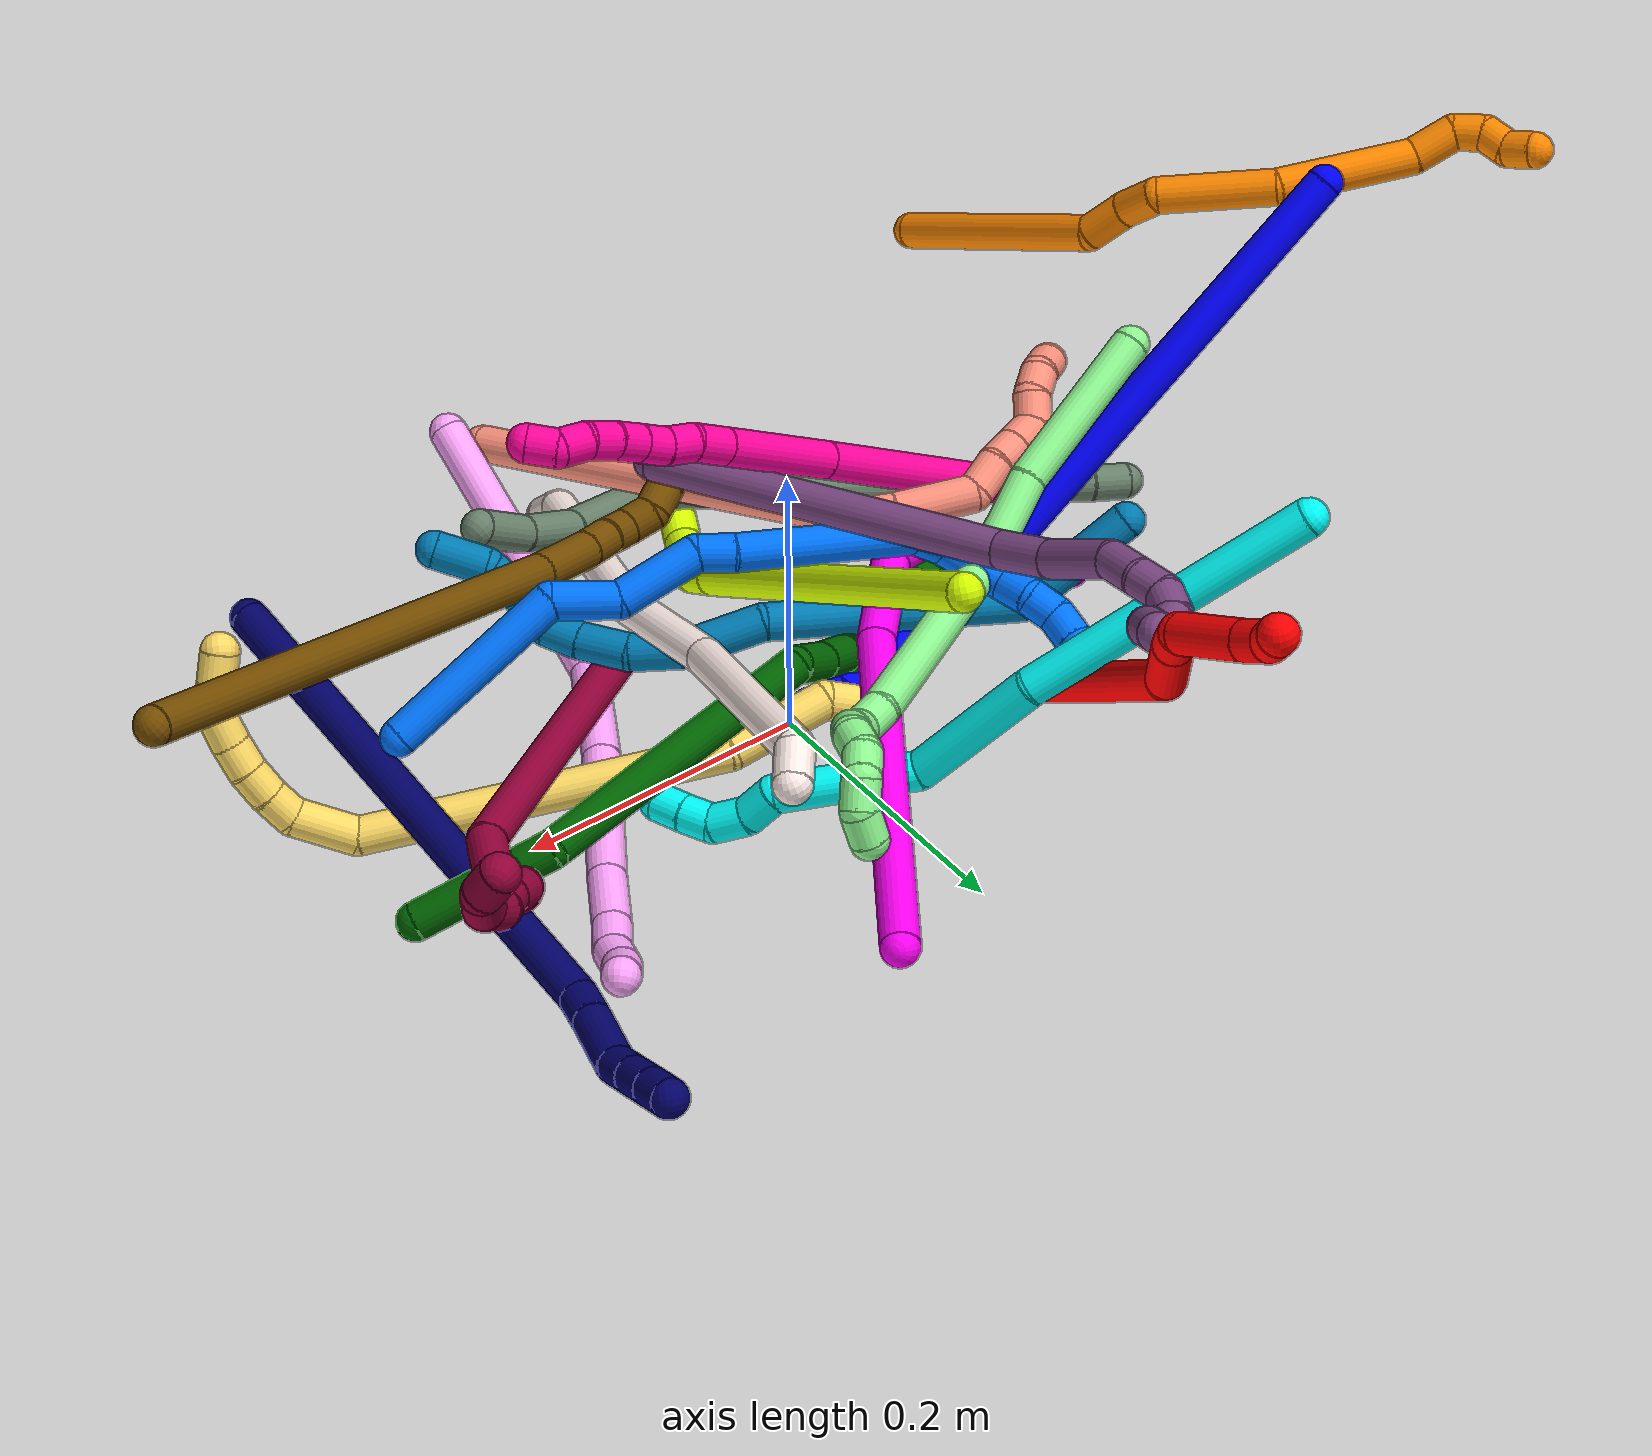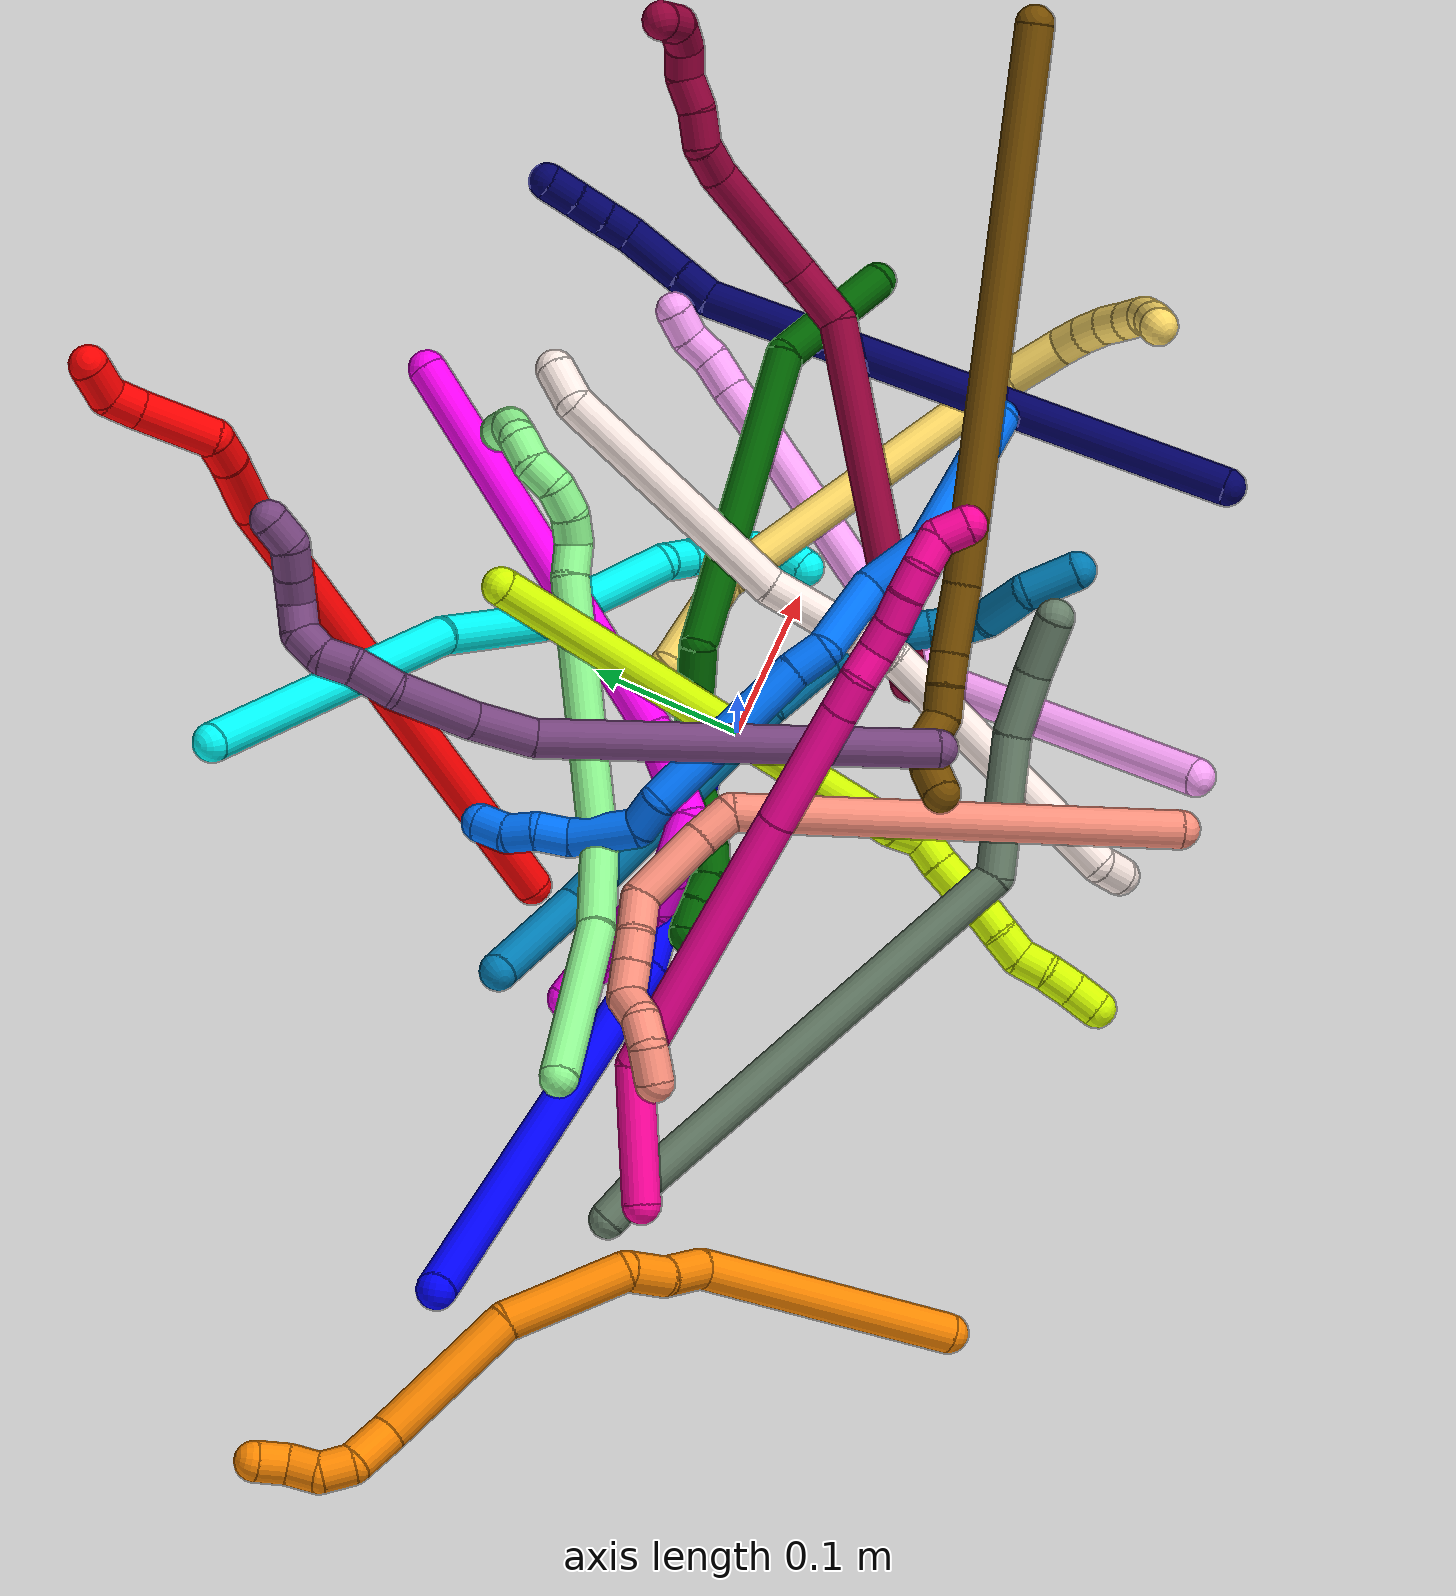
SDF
<sdf version="1.7">
 <world name="default">
  <plugin name="TubeGeneratorPlugin" filename="libtube_generator_plugin.so"/>
  <model name="photoneo_s_sensor">
   <static>1</static>
   <pose>0 0 2 1.57079 1.57079 3.14159</pose>
   <link name="link">
    <inertial><mass>0.1</mass></inertial>
    <sensor name="sensor" type="depth">
     <update_rate>30</update_rate>
     <camera>
      <horizontal_fov>1.22</horizontal_fov>
      <image><width>1920</width><height>1200</height><format>B8G8R8</format></image>
      <clip><near>0.1</near><far>4</far></clip>
      <depth_camera><output>points</output></depth_camera>
     </camera>
     <plugin name="camera_plugin" filename="libgazebo_ros_depth_camera.so">
      <baseline>0.2</baseline>
      <alwaysOn>1</alwaysOn>
      <updateRate>0.0</updateRate>
      <cameraName>camera_ir</cameraName>
      <imageTopicName>/camera/color/image_raw</imageTopicName>
      <cameraInfoTopicName>/camera/color/camera_info</cameraInfoTopicName>
      <depthImageTopicName>/camera/depth/image_raw</depthImageTopicName>
      <depthImageCameraInfoTopicName>/camera/depth/camera_info</depthImageCameraInfoTopicName>
      <pointCloudTopicName>/camera/depth/points</pointCloudTopicName>
      <frameName>fr_optical</frameName>
      <pointCloudCutoff>0.1</pointCloudCutoff>
      <pointCloudCutoffMax>2.0</pointCloudCutoffMax>
      <distortionK1>0</distortionK1>
      <distortionK2>0</distortionK2>
      <distortionK3>0</distortionK3>
      <distortionT1>0</distortionT1>
      <distortionT2>0</distortionT2>
      <CxPrime>0</CxPrime>
      <Cx>0</Cx>
      <Cy>0</Cy>
      <focalLength>0</focalLength>
      <hackBaseline>0</hackBaseline>
     </plugin>
    </sensor>
   </link>
  </model>
  <gravity>0 0 -9.8</gravity>
  <magnetic_field>6e-06 2.3e-05 -4.2e-05</magnetic_field>
  <atmosphere type="adiabatic"/>
  <physics name="default_physics" default="0" type="ode">
   <max_step_size>0.003</max_step_size>
   <real_time_factor>1</real_time_factor>
   <real_time_update_rate>1000</real_time_update_rate>
   <max_contacts>10000</max_contacts>
   <ode>
    <solver>
     <type>quick</type>
     <iters>100</iters>
     <sor>1.3</sor>
     <use_dynamic_moi_rescaling>0</use_dynamic_moi_rescaling>
    </solver>
    <constraints>
     <contact_max_correcting_vel>0</contact_max_correcting_vel>
     <contact_surface_layer>0.001</contact_surface_layer>
     <cfm>0</cfm>
     <erp>0.2</erp>
    </constraints>
   </ode>
  </physics>
  <scene><ambient>0.4 0.4 0.4 1</ambient><background>0.7 0.7 0.7 1</background><shadows>0</shadows></scene>
  <audio><device>default</device></audio>
  <spherical_coordinates>
   <surface_model>EARTH_WGS84</surface_model>
   <latitude_deg>0</latitude_deg>
   <longitude_deg>0</longitude_deg>
   <elevation>0</elevation>
   <heading_deg>0</heading_deg>
  </spherical_coordinates>
  <model name="bin">
   <static>1</static>
   <link name="bottom">
    <collision name="collision-bottom">
     <pose>0 0 -0.01 0 -0 0</pose>
     <geometry><box><size>0.8 0.6 0.02</size></box></geometry>
     <surface>
      <friction><ode><mu>100</mu><mu2>100</mu2></ode></friction>
      <contact><collide_bitmask>65535</collide_bitmask></contact>
     </surface>
    </collision>
   </link>
   <link name="west_wall">
    <collision name="collision-west_wall">
     <pose>-0.41 0 0.1 0 -0 0</pose>
     <geometry><box><size>0.02 0.6 0.2</size></box></geometry>
     <surface>
      <friction><ode><mu>100</mu><mu2>100</mu2></ode></friction>
      <contact><collide_bitmask>65535</collide_bitmask></contact>
     </surface>
    </collision>
   </link>
   <link name="east_wall">
    <collision name="collision-east_wall">
     <pose>0.41 0 0.1 0 -0 0</pose>
     <geometry><box><size>0.02 0.6 0.2</size></box></geometry>
     <surface>
      <friction><ode><mu>100</mu><mu2>100</mu2></ode></friction>
      <contact><collide_bitmask>65535</collide_bitmask></contact>
     </surface>
    </collision>
   </link>
   <link name="south_wall">
    <collision name="collision-south_wall">
     <pose>0 -0.31 0.1 0 -0 0</pose>
     <geometry><box><size>0.8 0.02 0.2</size></box></geometry>
     <surface>
      <friction><ode><mu>100</mu><mu2>100</mu2></ode></friction>
      <contact><collide_bitmask>65535</collide_bitmask></contact>
     </surface>
    </collision>
   </link>
   <link name="north_wall">
    <collision name="collision-north_wall">
     <pose>0 0.31 0.1 0 -0 0</pose>
     <geometry><box><size>0.8 0.02 0.2</size></box></geometry>
     <surface>
      <friction><ode><mu>100</mu><mu2>100</mu2></ode></friction>
      <contact><collide_bitmask>65535</collide_bitmask></contact>
     </surface>
    </collision>
   </link>
  </model>
  <model name="1">
   <static>0</static>
   <link name="1">
    <collision name="collision-cylinder-e_1_1_4">
     <pose>0.107874 -0.072857 -0.104615 2.53327 0.702266 1.72459</pose>
     <geometry><cylinder><radius>0.0125</radius><length>0.334</length></cylinder></geometry>
     <surface>
      <friction><ode><mu>1.16</mu><mu2>1.16</mu2><slip1>0</slip1><slip2>0</slip2></ode></friction>
      <contact><ode><kp>1e+06</kp><kd>1</kd><max_vel>0</max_vel><min_depth>0.001</min_depth></ode></contact>
     </surface>
    </collision>
    <visual name="visual-cylinder-e_1_1_4">
     <pose>0.107874 -0.072857 -0.104615 2.53327 0.702266 1.72459</pose>
     <geometry><cylinder><radius>0.0125</radius><length>0.334</length></cylinder></geometry>
     <material><ambient>0 0 1 1</ambient></material>
    </visual>
    <collision name="collision-cylinder-e_2_4_5">
     <pose>0.224241 -0.152194 -0.235324 2.89818 0.305962 1.80037</pose>
     <geometry><cylinder><radius>0.0125</radius><length>0.056395</length></cylinder></geometry>
     <surface>
      <friction><ode><mu>1.16</mu><mu2>1.16</mu2><slip1>0</slip1><slip2>0</slip2></ode></friction>
      <contact><ode><kp>1e+06</kp><kd>1</kd><max_vel>0</max_vel><min_depth>0.001</min_depth></ode></contact>
     </surface>
    </collision>
    <visual name="visual-cylinder-e_2_4_5">
     <pose>0.224241 -0.152194 -0.235324 2.89818 0.305962 1.80037</pose>
     <geometry><cylinder><radius>0.0125</radius><length>0.056395</length></cylinder></geometry>
     <material><ambient>0 0 1 1</ambient></material>
    </visual>
    <collision name="collision-cylinder-e_3_5_6">
     <pose>0.242008 -0.166194 -0.289525 2.88016 0.30858 1.73808</pose>
     <geometry><cylinder><radius>0.0125</radius><length>0.061073</length></cylinder></geometry>
     <surface>
      <friction><ode><mu>1.16</mu><mu2>1.16</mu2><slip1>0</slip1><slip2>0</slip2></ode></friction>
      <contact><ode><kp>1e+06</kp><kd>1</kd><max_vel>0</max_vel><min_depth>0.001</min_depth></ode></contact>
     </surface>
    </collision>
    <visual name="visual-cylinder-e_3_5_6">
     <pose>0.242008 -0.166194 -0.289525 2.88016 0.30858 1.73808</pose>
     <geometry><cylinder><radius>0.0125</radius><length>0.061073</length></cylinder></geometry>
     <material><ambient>0 0 1 1</ambient></material>
    </visual>
    <collision name="collision-cylinder-e_4_6_7">
     <pose>0.253886 -0.174894 -0.329008 3.03824 0.223787 2.27879</pose>
     <geometry><cylinder><radius>0.0125</radius><length>0.023461</length></cylinder></geometry>
     <surface>
      <friction><ode><mu>1.16</mu><mu2>1.16</mu2><slip1>0</slip1><slip2>0</slip2></ode></friction>
      <contact><ode><kp>1e+06</kp><kd>1</kd><max_vel>0</max_vel><min_depth>0.001</min_depth></ode></contact>
     </surface>
    </collision>
    <visual name="visual-cylinder-e_4_6_7">
     <pose>0.253886 -0.174894 -0.329008 3.03824 0.223787 2.27879</pose>
     <geometry><cylinder><radius>0.0125</radius><length>0.023461</length></cylinder></geometry>
     <material><ambient>0 0 1 1</ambient></material>
    </visual>
    <collision name="collision-cylinder-e_5_7_2">
     <pose>0.26238 -0.175393 -0.351429 -3.07998 0.48922 -2.89591</pose>
     <geometry><cylinder><radius>0.0125</radius><length>0.025071</length></cylinder></geometry>
     <surface>
      <friction><ode><mu>1.16</mu><mu2>1.16</mu2><slip1>0</slip1><slip2>0</slip2></ode></friction>
      <contact><ode><kp>1e+06</kp><kd>1</kd><max_vel>0</max_vel><min_depth>0.001</min_depth></ode></contact>
     </surface>
    </collision>
    <visual name="visual-cylinder-e_5_7_2">
     <pose>0.26238 -0.175393 -0.351429 -3.07998 0.48922 -2.89591</pose>
     <geometry><cylinder><radius>0.0125</radius><length>0.025071</length></cylinder></geometry>
     <material><ambient>0 0 1 1</ambient></material>
    </visual>
    <collision name="collision-sphere-2">
     <pose>0.268271 -0.174711 -0.362473 0 -0 0</pose>
     <geometry><sphere><radius>0.0125</radius></sphere></geometry>
     <surface>
      <friction><ode><mu>1.16</mu><mu2>1.16</mu2><slip1>0</slip1><slip2>0</slip2></ode></friction>
      <contact><ode><kp>1e+06</kp><kd>1</kd><max_vel>0</max_vel><min_depth>0.001</min_depth></ode></contact>
     </surface>
    </collision>
    <visual name="visual-sphere-2">
     <pose>0.268271 -0.174711 -0.362473 0 -0 0</pose>
     <geometry><sphere><radius>0.0125</radius></sphere></geometry>
     <material><ambient>0 0 1 1</ambient></material>
    </visual>
    <collision name="collision-sphere-7">
     <pose>0.256489 -0.176074 -0.340385 0 -0 0</pose>
     <geometry><sphere><radius>0.0125</radius></sphere></geometry>
     <surface>
      <friction><ode><mu>1.16</mu><mu2>1.16</mu2><slip1>0</slip1><slip2>0</slip2></ode></friction>
      <contact><ode><kp>1e+06</kp><kd>1</kd><max_vel>0</max_vel><min_depth>0.001</min_depth></ode></contact>
     </surface>
    </collision>
    <visual name="visual-sphere-7">
     <pose>0.256489 -0.176074 -0.340385 0 -0 0</pose>
     <geometry><sphere><radius>0.0125</radius></sphere></geometry>
     <material><ambient>0 0 1 1</ambient></material>
    </visual>
    <collision name="collision-sphere-6">
     <pose>0.251282 -0.173714 -0.317631 0 -0 0</pose>
     <geometry><sphere><radius>0.0125</radius></sphere></geometry>
     <surface>
      <friction><ode><mu>1.16</mu><mu2>1.16</mu2><slip1>0</slip1><slip2>0</slip2></ode></friction>
      <contact><ode><kp>1e+06</kp><kd>1</kd><max_vel>0</max_vel><min_depth>0.001</min_depth></ode></contact>
     </surface>
    </collision>
    <visual name="visual-sphere-6">
     <pose>0.251282 -0.173714 -0.317631 0 -0 0</pose>
     <geometry><sphere><radius>0.0125</radius></sphere></geometry>
     <material><ambient>0 0 1 1</ambient></material>
    </visual>
    <collision name="collision-sphere-5">
     <pose>0.232734 -0.158674 -0.261419 0 -0 0</pose>
     <geometry><sphere><radius>0.0125</radius></sphere></geometry>
     <surface>
      <friction><ode><mu>1.16</mu><mu2>1.16</mu2><slip1>0</slip1><slip2>0</slip2></ode></friction>
      <contact><ode><kp>1e+06</kp><kd>1</kd><max_vel>0</max_vel><min_depth>0.001</min_depth></ode></contact>
     </surface>
    </collision>
    <visual name="visual-sphere-5">
     <pose>0.232734 -0.158674 -0.261419 0 -0 0</pose>
     <geometry><sphere><radius>0.0125</radius></sphere></geometry>
     <material><ambient>0 0 1 1</ambient></material>
    </visual>
    <collision name="collision-sphere-1">
     <geometry><sphere><radius>0.0125</radius></sphere></geometry>
     <surface>
      <friction><ode><mu>1.16</mu><mu2>1.16</mu2><slip1>0</slip1><slip2>0</slip2></ode></friction>
      <contact><ode><kp>1e+06</kp><kd>1</kd><max_vel>0</max_vel><min_depth>0.001</min_depth></ode></contact>
     </surface>
    </collision>
    <visual name="visual-sphere-1">
     <geometry><sphere><radius>0.0125</radius></sphere></geometry>
     <material><ambient>0 0 1 1</ambient></material>
    </visual>
    <collision name="collision-sphere-4">
     <pose>0.215747 -0.145714 -0.209229 0 -0 0</pose>
     <geometry><sphere><radius>0.0125</radius></sphere></geometry>
     <surface>
      <friction><ode><mu>1.16</mu><mu2>1.16</mu2><slip1>0</slip1><slip2>0</slip2></ode></friction>
      <contact><ode><kp>1e+06</kp><kd>1</kd><max_vel>0</max_vel><min_depth>0.001</min_depth></ode></contact>
     </surface>
    </collision>
    <visual name="visual-sphere-4">
     <pose>0.215747 -0.145714 -0.209229 0 -0 0</pose>
     <geometry><sphere><radius>0.0125</radius></sphere></geometry>
     <material><ambient>0 0 1 1</ambient></material>
    </visual>
    <inertial>
     <pose>0.151981 -0.103135 -0.164848 0 -0 0</pose>
     <mass>0.5</mass>
     <inertia>
      <ixx>0.002035</ixx>
      <ixy>0</ixy>
      <ixz>0</ixz>
      <iyy>0.003919</iyy>
      <iyz>0</iyz>
      <izz>-0.000686</izz>
     </inertia>
    </inertial>
   </link>
   <pose>-0.436874 0.00221 0.243418 1.79302 0.634537 -1.17367</pose>
  </model>
  <model name="2">
   <static>0</static>
   <link name="2">
    <collision name="collision-cylinder-e_1_1_4">
     <pose>0.003583 0.130474 0.103055 -0.902274 0.021548 -0.010439</pose>
     <geometry><cylinder><radius>0.0125</radius><length>0.332605</length></cylinder></geometry>
     <surface>
      <friction><ode><mu>1.16</mu><mu2>1.16</mu2><slip1>0</slip1><slip2>0</slip2></ode></friction>
      <contact><ode><kp>1e+06</kp><kd>1</kd><max_vel>0</max_vel><min_depth>0.001</min_depth></ode></contact>
     </surface>
    </collision>
    <visual name="visual-cylinder-e_1_1_4">
     <pose>0.003583 0.130474 0.103055 -0.902274 0.021548 -0.010439</pose>
     <geometry><cylinder><radius>0.0125</radius><length>0.332605</length></cylinder></geometry>
     <material><ambient>1 0 0 1</ambient></material>
    </visual>
    <collision name="collision-cylinder-e_2_4_5">
     <pose>0.00754 0.271974 0.227628 -0.473535 0.015443 -0.003726</pose>
     <geometry><cylinder><radius>0.0125</radius><length>0.048364</length></cylinder></geometry>
     <surface>
      <friction><ode><mu>1.16</mu><mu2>1.16</mu2><slip1>0</slip1><slip2>0</slip2></ode></friction>
      <contact><ode><kp>1e+06</kp><kd>1</kd><max_vel>0</max_vel><min_depth>0.001</min_depth></ode></contact>
     </surface>
    </collision>
    <visual name="visual-cylinder-e_2_4_5">
     <pose>0.00754 0.271974 0.227628 -0.473535 0.015443 -0.003726</pose>
     <geometry><cylinder><radius>0.0125</radius><length>0.048364</length></cylinder></geometry>
     <material><ambient>1 0 0 1</ambient></material>
    </visual>
    <collision name="collision-cylinder-e_3_5_6">
     <pose>0.007796 0.289076 0.258225 -0.58979 -0.010752 0.003266</pose>
     <geometry><cylinder><radius>0.0125</radius><length>0.021849</length></cylinder></geometry>
     <surface>
      <friction><ode><mu>1.16</mu><mu2>1.16</mu2><slip1>0</slip1><slip2>0</slip2></ode></friction>
      <contact><ode><kp>1e+06</kp><kd>1</kd><max_vel>0</max_vel><min_depth>0.001</min_depth></ode></contact>
     </surface>
    </collision>
    <visual name="visual-cylinder-e_3_5_6">
     <pose>0.007796 0.289076 0.258225 -0.58979 -0.010752 0.003266</pose>
     <geometry><cylinder><radius>0.0125</radius><length>0.021849</length></cylinder></geometry>
     <material><ambient>1 0 0 1</ambient></material>
    </visual>
    <collision name="collision-cylinder-e_4_6_7">
     <pose>-0.003567 0.316411 0.27575 -1.1926 -0.456906 0.313038</pose>
     <geometry><cylinder><radius>0.0125</radius><length>0.05098</length></cylinder></geometry>
     <surface>
      <friction><ode><mu>1.16</mu><mu2>1.16</mu2><slip1>0</slip1><slip2>0</slip2></ode></friction>
      <contact><ode><kp>1e+06</kp><kd>1</kd><max_vel>0</max_vel><min_depth>0.001</min_depth></ode></contact>
     </surface>
    </collision>
    <visual name="visual-cylinder-e_4_6_7">
     <pose>-0.003567 0.316411 0.27575 -1.1926 -0.456906 0.313038</pose>
     <geometry><cylinder><radius>0.0125</radius><length>0.05098</length></cylinder></geometry>
     <material><ambient>1 0 0 1</ambient></material>
    </visual>
    <collision name="collision-cylinder-e_5_7_8">
     <pose>-0.01914 0.346297 0.288459 -1.112 -0.422575 0.265001</pose>
     <geometry><cylinder><radius>0.0125</radius><length>0.021102</length></cylinder></geometry>
     <surface>
      <friction><ode><mu>1.16</mu><mu2>1.16</mu2><slip1>0</slip1><slip2>0</slip2></ode></friction>
      <contact><ode><kp>1e+06</kp><kd>1</kd><max_vel>0</max_vel><min_depth>0.001</min_depth></ode></contact>
     </surface>
    </collision>
    <visual name="visual-cylinder-e_5_7_8">
     <pose>-0.01914 0.346297 0.288459 -1.112 -0.422575 0.265001</pose>
     <geometry><cylinder><radius>0.0125</radius><length>0.021102</length></cylinder></geometry>
     <material><ambient>1 0 0 1</ambient></material>
    </visual>
    <collision name="collision-cylinder-e_6_8_2">
     <pose>-0.022767 0.363453 0.301901 -0.748544 0.055821 -0.021931</pose>
     <geometry><cylinder><radius>0.0125</radius><length>0.025099</length></cylinder></geometry>
     <surface>
      <friction><ode><mu>1.16</mu><mu2>1.16</mu2><slip1>0</slip1><slip2>0</slip2></ode></friction>
      <contact><ode><kp>1e+06</kp><kd>1</kd><max_vel>0</max_vel><min_depth>0.001</min_depth></ode></contact>
     </surface>
    </collision>
    <visual name="visual-cylinder-e_6_8_2">
     <pose>-0.022767 0.363453 0.301901 -0.748544 0.055821 -0.021931</pose>
     <geometry><cylinder><radius>0.0125</radius><length>0.025099</length></cylinder></geometry>
     <material><ambient>1 0 0 1</ambient></material>
    </visual>
    <collision name="collision-sphere-2">
     <pose>-0.022067 0.37198 0.311082 0 -0 0</pose>
     <geometry><sphere><radius>0.0125</radius></sphere></geometry>
     <surface>
      <friction><ode><mu>1.16</mu><mu2>1.16</mu2><slip1>0</slip1><slip2>0</slip2></ode></friction>
      <contact><ode><kp>1e+06</kp><kd>1</kd><max_vel>0</max_vel><min_depth>0.001</min_depth></ode></contact>
     </surface>
    </collision>
    <visual name="visual-sphere-2">
     <pose>-0.022067 0.37198 0.311082 0 -0 0</pose>
     <geometry><sphere><radius>0.0125</radius></sphere></geometry>
     <material><ambient>1 0 0 1</ambient></material>
    </visual>
    <collision name="collision-sphere-4">
     <pose>0.007166 0.260947 0.20611 0 -0 0</pose>
     <geometry><sphere><radius>0.0125</radius></sphere></geometry>
     <surface>
      <friction><ode><mu>1.16</mu><mu2>1.16</mu2><slip1>0</slip1><slip2>0</slip2></ode></friction>
      <contact><ode><kp>1e+06</kp><kd>1</kd><max_vel>0</max_vel><min_depth>0.001</min_depth></ode></contact>
     </surface>
    </collision>
    <visual name="visual-sphere-4">
     <pose>0.007166 0.260947 0.20611 0 -0 0</pose>
     <geometry><sphere><radius>0.0125</radius></sphere></geometry>
     <material><ambient>1 0 0 1</ambient></material>
    </visual>
    <collision name="collision-sphere-1">
     <geometry><sphere><radius>0.0125</radius></sphere></geometry>
     <surface>
      <friction><ode><mu>1.16</mu><mu2>1.16</mu2><slip1>0</slip1><slip2>0</slip2></ode></friction>
      <contact><ode><kp>1e+06</kp><kd>1</kd><max_vel>0</max_vel><min_depth>0.001</min_depth></ode></contact>
     </surface>
    </collision>
    <visual name="visual-sphere-1">
     <geometry><sphere><radius>0.0125</radius></sphere></geometry>
     <material><ambient>1 0 0 1</ambient></material>
    </visual>
    <collision name="collision-sphere-8">
     <pose>-0.023467 0.354925 0.292721 0 -0 0</pose>
     <geometry><sphere><radius>0.0125</radius></sphere></geometry>
     <surface>
      <friction><ode><mu>1.16</mu><mu2>1.16</mu2><slip1>0</slip1><slip2>0</slip2></ode></friction>
      <contact><ode><kp>1e+06</kp><kd>1</kd><max_vel>0</max_vel><min_depth>0.001</min_depth></ode></contact>
     </surface>
    </collision>
    <visual name="visual-sphere-8">
     <pose>-0.023467 0.354925 0.292721 0 -0 0</pose>
     <geometry><sphere><radius>0.0125</radius></sphere></geometry>
     <material><ambient>1 0 0 1</ambient></material>
    </visual>
    <collision name="collision-sphere-5">
     <pose>0.007913 0.283 0.249147 0 -0 0</pose>
     <geometry><sphere><radius>0.0125</radius></sphere></geometry>
     <surface>
      <friction><ode><mu>1.16</mu><mu2>1.16</mu2><slip1>0</slip1><slip2>0</slip2></ode></friction>
      <contact><ode><kp>1e+06</kp><kd>1</kd><max_vel>0</max_vel><min_depth>0.001</min_depth></ode></contact>
     </surface>
    </collision>
    <visual name="visual-sphere-5">
     <pose>0.007913 0.283 0.249147 0 -0 0</pose>
     <geometry><sphere><radius>0.0125</radius></sphere></geometry>
     <material><ambient>1 0 0 1</ambient></material>
    </visual>
    <collision name="collision-sphere-6">
     <pose>0.007678 0.295152 0.267304 0 -0 0</pose>
     <geometry><sphere><radius>0.0125</radius></sphere></geometry>
     <surface>
      <friction><ode><mu>1.16</mu><mu2>1.16</mu2><slip1>0</slip1><slip2>0</slip2></ode></friction>
      <contact><ode><kp>1e+06</kp><kd>1</kd><max_vel>0</max_vel><min_depth>0.001</min_depth></ode></contact>
     </surface>
    </collision>
    <visual name="visual-sphere-6">
     <pose>0.007678 0.295152 0.267304 0 -0 0</pose>
     <geometry><sphere><radius>0.0125</radius></sphere></geometry>
     <material><ambient>1 0 0 1</ambient></material>
    </visual>
    <collision name="collision-sphere-7">
     <pose>-0.014813 0.337669 0.284197 0 -0 0</pose>
     <geometry><sphere><radius>0.0125</radius></sphere></geometry>
     <surface>
      <friction><ode><mu>1.16</mu><mu2>1.16</mu2><slip1>0</slip1><slip2>0</slip2></ode></friction>
      <contact><ode><kp>1e+06</kp><kd>1</kd><max_vel>0</max_vel><min_depth>0.001</min_depth></ode></contact>
     </surface>
    </collision>
    <visual name="visual-sphere-7">
     <pose>-0.014813 0.337669 0.284197 0 -0 0</pose>
     <geometry><sphere><radius>0.0125</radius></sphere></geometry>
     <material><ambient>1 0 0 1</ambient></material>
    </visual>
    <inertial>
     <pose>0.001139 0.190854 0.1573 0 -0 0</pose>
     <mass>0.5</mass>
     <inertia>
      <ixx>0.003076</ixx>
      <ixy>0</ixy>
      <ixz>0</ixz>
      <iyy>0.00193</iyy>
      <iyz>0</iyz>
      <izz>-0.002472</izz>
     </inertia>
    </inertial>
   </link>
   <pose>-0.148547 0.078013 0.011489 0.03948 0.131159 -0.288222</pose>
  </model>
  <model name="3">
   <static>0</static>
   <link name="3">
    <collision name="collision-cylinder-e_1_1_4">
     <pose>0.002268 0.009738 -0.099819 -3.04434 0.022611 -0.456572</pose>
     <geometry><cylinder><radius>0.0125</radius><length>0.200637</length></cylinder></geometry>
     <surface>
      <friction><ode><mu>1.16</mu><mu2>1.16</mu2><slip1>0</slip1><slip2>0</slip2></ode></friction>
      <contact><ode><kp>1e+06</kp><kd>1</kd><max_vel>0</max_vel><min_depth>0.001</min_depth></ode></contact>
     </surface>
    </collision>
    <visual name="visual-cylinder-e_1_1_4">
     <pose>0.002268 0.009738 -0.099819 -3.04434 0.022611 -0.456572</pose>
     <geometry><cylinder><radius>0.0125</radius><length>0.200637</length></cylinder></geometry>
     <material><ambient>0.003922 1 0.996078 1</ambient></material>
    </visual>
    <collision name="collision-cylinder-e_2_4_5">
     <pose>-0.004751 0.016873 -0.24741 3.08716 -0.191745 -2.58984</pose>
     <geometry><cylinder><radius>0.0125</radius><length>0.097472</length></cylinder></geometry>
     <surface>
      <friction><ode><mu>1.16</mu><mu2>1.16</mu2><slip1>0</slip1><slip2>0</slip2></ode></friction>
      <contact><ode><kp>1e+06</kp><kd>1</kd><max_vel>0</max_vel><min_depth>0.001</min_depth></ode></contact>
     </surface>
    </collision>
    <visual name="visual-cylinder-e_2_4_5">
     <pose>-0.004751 0.016873 -0.24741 3.08716 -0.191745 -2.58984</pose>
     <geometry><cylinder><radius>0.0125</radius><length>0.097472</length></cylinder></geometry>
     <material><ambient>0.003922 1 0.996078 1</ambient></material>
    </visual>
    <collision name="collision-cylinder-e_3_5_6">
     <pose>0.005558 0.0148 -0.337004 -3.12892 0.438164 -3.08469</pose>
     <geometry><cylinder><radius>0.0125</radius><length>0.092377</length></cylinder></geometry>
     <surface>
      <friction><ode><mu>1.16</mu><mu2>1.16</mu2><slip1>0</slip1><slip2>0</slip2></ode></friction>
      <contact><ode><kp>1e+06</kp><kd>1</kd><max_vel>0</max_vel><min_depth>0.001</min_depth></ode></contact>
     </surface>
    </collision>
    <visual name="visual-cylinder-e_3_5_6">
     <pose>0.005558 0.0148 -0.337004 -3.12892 0.438164 -3.08469</pose>
     <geometry><cylinder><radius>0.0125</radius><length>0.092377</length></cylinder></geometry>
     <material><ambient>0.003922 1 0.996078 1</ambient></material>
    </visual>
    <collision name="collision-cylinder-e_4_6_7">
     <pose>0.022651 0.015088 -0.391015 3.12176 -0.202574 -2.9471</pose>
     <geometry><cylinder><radius>0.0125</radius><length>0.024891</length></cylinder></geometry>
     <surface>
      <friction><ode><mu>1.16</mu><mu2>1.16</mu2><slip1>0</slip1><slip2>0</slip2></ode></friction>
      <contact><ode><kp>1e+06</kp><kd>1</kd><max_vel>0</max_vel><min_depth>0.001</min_depth></ode></contact>
     </surface>
    </collision>
    <visual name="visual-cylinder-e_4_6_7">
     <pose>0.022651 0.015088 -0.391015 3.12176 -0.202574 -2.9471</pose>
     <geometry><cylinder><radius>0.0125</radius><length>0.024891</length></cylinder></geometry>
     <material><ambient>0.003922 1 0.996078 1</ambient></material>
    </visual>
    <collision name="collision-cylinder-e_5_7_8">
     <pose>0.022637 0.013073 -0.415116 2.99387 0.203869 1.88909</pose>
     <geometry><cylinder><radius>0.0125</radius><length>0.024598</length></cylinder></geometry>
     <surface>
      <friction><ode><mu>1.16</mu><mu2>1.16</mu2><slip1>0</slip1><slip2>0</slip2></ode></friction>
      <contact><ode><kp>1e+06</kp><kd>1</kd><max_vel>0</max_vel><min_depth>0.001</min_depth></ode></contact>
     </surface>
    </collision>
    <visual name="visual-cylinder-e_5_7_8">
     <pose>0.022637 0.013073 -0.415116 2.99387 0.203869 1.88909</pose>
     <geometry><cylinder><radius>0.0125</radius><length>0.024598</length></cylinder></geometry>
     <material><ambient>0.003922 1 0.996078 1</ambient></material>
    </visual>
    <collision name="collision-cylinder-e_6_8_9">
     <pose>0.030512 0.006599 -0.434037 2.55065 0.568019 1.52895</pose>
     <geometry><cylinder><radius>0.0125</radius><length>0.02002</length></cylinder></geometry>
     <surface>
      <friction><ode><mu>1.16</mu><mu2>1.16</mu2><slip1>0</slip1><slip2>0</slip2></ode></friction>
      <contact><ode><kp>1e+06</kp><kd>1</kd><max_vel>0</max_vel><min_depth>0.001</min_depth></ode></contact>
     </surface>
    </collision>
    <visual name="visual-cylinder-e_6_8_9">
     <pose>0.030512 0.006599 -0.434037 2.55065 0.568019 1.52895</pose>
     <geometry><cylinder><radius>0.0125</radius><length>0.02002</length></cylinder></geometry>
     <material><ambient>0.003922 1 0.996078 1</ambient></material>
    </visual>
    <collision name="collision-cylinder-e_7_9_10">
     <pose>0.040877 -0.003513 -0.447821 2.46775 0.521295 1.30156</pose>
     <geometry><cylinder><radius>0.0125</radius><length>0.02</length></cylinder></geometry>
     <surface>
      <friction><ode><mu>1.16</mu><mu2>1.16</mu2><slip1>0</slip1><slip2>0</slip2></ode></friction>
      <contact><ode><kp>1e+06</kp><kd>1</kd><max_vel>0</max_vel><min_depth>0.001</min_depth></ode></contact>
     </surface>
    </collision>
    <visual name="visual-cylinder-e_7_9_10">
     <pose>0.040877 -0.003513 -0.447821 2.46775 0.521295 1.30156</pose>
     <geometry><cylinder><radius>0.0125</radius><length>0.02</length></cylinder></geometry>
     <material><ambient>0.003922 1 0.996078 1</ambient></material>
    </visual>
    <collision name="collision-cylinder-e_8_10_2">
     <pose>0.049939 -0.017833 -0.456601 1.79201 0.420338 0.521119</pose>
     <geometry><cylinder><radius>0.0125</radius><length>0.020004</length></cylinder></geometry>
     <surface>
      <friction><ode><mu>1.16</mu><mu2>1.16</mu2><slip1>0</slip1><slip2>0</slip2></ode></friction>
      <contact><ode><kp>1e+06</kp><kd>1</kd><max_vel>0</max_vel><min_depth>0.001</min_depth></ode></contact>
     </surface>
    </collision>
    <visual name="visual-cylinder-e_8_10_2">
     <pose>0.049939 -0.017833 -0.456601 1.79201 0.420338 0.521119</pose>
     <geometry><cylinder><radius>0.0125</radius><length>0.020004</length></cylinder></geometry>
     <material><ambient>0.003922 1 0.996078 1</ambient></material>
    </visual>
    <collision name="collision-sphere-2">
     <pose>0.05402 -0.026742 -0.458604 0 -0 0</pose>
     <geometry><sphere><radius>0.0125</radius></sphere></geometry>
     <surface>
      <friction><ode><mu>1.16</mu><mu2>1.16</mu2><slip1>0</slip1><slip2>0</slip2></ode></friction>
      <contact><ode><kp>1e+06</kp><kd>1</kd><max_vel>0</max_vel><min_depth>0.001</min_depth></ode></contact>
     </surface>
    </collision>
    <visual name="visual-sphere-2">
     <pose>0.05402 -0.026742 -0.458604 0 -0 0</pose>
     <geometry><sphere><radius>0.0125</radius></sphere></geometry>
     <material><ambient>0.003922 1 0.996078 1</ambient></material>
    </visual>
    <collision name="collision-sphere-10">
     <pose>0.045857 -0.008924 -0.454597 0 -0 0</pose>
     <geometry><sphere><radius>0.0125</radius></sphere></geometry>
     <surface>
      <friction><ode><mu>1.16</mu><mu2>1.16</mu2><slip1>0</slip1><slip2>0</slip2></ode></friction>
      <contact><ode><kp>1e+06</kp><kd>1</kd><max_vel>0</max_vel><min_depth>0.001</min_depth></ode></contact>
     </surface>
    </collision>
    <visual name="visual-sphere-10">
     <pose>0.045857 -0.008924 -0.454597 0 -0 0</pose>
     <geometry><sphere><radius>0.0125</radius></sphere></geometry>
     <material><ambient>0.003922 1 0.996078 1</ambient></material>
    </visual>
    <collision name="collision-sphere-9">
     <pose>0.035897 0.001898 -0.441044 0 -0 0</pose>
     <geometry><sphere><radius>0.0125</radius></sphere></geometry>
     <surface>
      <friction><ode><mu>1.16</mu><mu2>1.16</mu2><slip1>0</slip1><slip2>0</slip2></ode></friction>
      <contact><ode><kp>1e+06</kp><kd>1</kd><max_vel>0</max_vel><min_depth>0.001</min_depth></ode></contact>
     </surface>
    </collision>
    <visual name="visual-sphere-9">
     <pose>0.035897 0.001898 -0.441044 0 -0 0</pose>
     <geometry><sphere><radius>0.0125</radius></sphere></geometry>
     <material><ambient>0.003922 1 0.996078 1</ambient></material>
    </visual>
    <collision name="collision-sphere-4">
     <pose>0.004536 0.019476 -0.199638 0 -0 0</pose>
     <geometry><sphere><radius>0.0125</radius></sphere></geometry>
     <surface>
      <friction><ode><mu>1.16</mu><mu2>1.16</mu2><slip1>0</slip1><slip2>0</slip2></ode></friction>
      <contact><ode><kp>1e+06</kp><kd>1</kd><max_vel>0</max_vel><min_depth>0.001</min_depth></ode></contact>
     </surface>
    </collision>
    <visual name="visual-sphere-4">
     <pose>0.004536 0.019476 -0.199638 0 -0 0</pose>
     <geometry><sphere><radius>0.0125</radius></sphere></geometry>
     <material><ambient>0.003922 1 0.996078 1</ambient></material>
    </visual>
    <collision name="collision-sphere-1">
     <geometry><sphere><radius>0.0125</radius></sphere></geometry>
     <surface>
      <friction><ode><mu>1.16</mu><mu2>1.16</mu2><slip1>0</slip1><slip2>0</slip2></ode></friction>
      <contact><ode><kp>1e+06</kp><kd>1</kd><max_vel>0</max_vel><min_depth>0.001</min_depth></ode></contact>
     </surface>
    </collision>
    <visual name="visual-sphere-1">
     <geometry><sphere><radius>0.0125</radius></sphere></geometry>
     <material><ambient>0.003922 1 0.996078 1</ambient></material>
    </visual>
    <collision name="collision-sphere-8">
     <pose>0.025127 0.011301 -0.42703 0 -0 0</pose>
     <geometry><sphere><radius>0.0125</radius></sphere></geometry>
     <surface>
      <friction><ode><mu>1.16</mu><mu2>1.16</mu2><slip1>0</slip1><slip2>0</slip2></ode></friction>
      <contact><ode><kp>1e+06</kp><kd>1</kd><max_vel>0</max_vel><min_depth>0.001</min_depth></ode></contact>
     </surface>
    </collision>
    <visual name="visual-sphere-8">
     <pose>0.025127 0.011301 -0.42703 0 -0 0</pose>
     <geometry><sphere><radius>0.0125</radius></sphere></geometry>
     <material><ambient>0.003922 1 0.996078 1</ambient></material>
    </visual>
    <collision name="collision-sphere-5">
     <pose>-0.014039 0.01427 -0.295182 0 -0 0</pose>
     <geometry><sphere><radius>0.0125</radius></sphere></geometry>
     <surface>
      <friction><ode><mu>1.16</mu><mu2>1.16</mu2><slip1>0</slip1><slip2>0</slip2></ode></friction>
      <contact><ode><kp>1e+06</kp><kd>1</kd><max_vel>0</max_vel><min_depth>0.001</min_depth></ode></contact>
     </surface>
    </collision>
    <visual name="visual-sphere-5">
     <pose>-0.014039 0.01427 -0.295182 0 -0 0</pose>
     <geometry><sphere><radius>0.0125</radius></sphere></geometry>
     <material><ambient>0.003922 1 0.996078 1</ambient></material>
    </visual>
    <collision name="collision-sphere-6">
     <pose>0.025154 0.01533 -0.378826 0 -0 0</pose>
     <geometry><sphere><radius>0.0125</radius></sphere></geometry>
     <surface>
      <friction><ode><mu>1.16</mu><mu2>1.16</mu2><slip1>0</slip1><slip2>0</slip2></ode></friction>
      <contact><ode><kp>1e+06</kp><kd>1</kd><max_vel>0</max_vel><min_depth>0.001</min_depth></ode></contact>
     </surface>
    </collision>
    <visual name="visual-sphere-6">
     <pose>0.025154 0.01533 -0.378826 0 -0 0</pose>
     <geometry><sphere><radius>0.0125</radius></sphere></geometry>
     <material><ambient>0.003922 1 0.996078 1</ambient></material>
    </visual>
    <collision name="collision-sphere-7">
     <pose>0.020147 0.014846 -0.403203 0 -0 0</pose>
     <geometry><sphere><radius>0.0125</radius></sphere></geometry>
     <surface>
      <friction><ode><mu>1.16</mu><mu2>1.16</mu2><slip1>0</slip1><slip2>0</slip2></ode></friction>
      <contact><ode><kp>1e+06</kp><kd>1</kd><max_vel>0</max_vel><min_depth>0.001</min_depth></ode></contact>
     </surface>
    </collision>
    <visual name="visual-sphere-7">
     <pose>0.020147 0.014846 -0.403203 0 -0 0</pose>
     <geometry><sphere><radius>0.0125</radius></sphere></geometry>
     <material><ambient>0.003922 1 0.996078 1</ambient></material>
    </visual>
    <inertial>
     <pose>0.008107 0.010736 -0.243996 0 -0 0</pose>
     <mass>0.5</mass>
     <inertia>
      <ixx>0.000143</ixx>
      <ixy>0</ixy>
      <ixz>0</ixz>
      <iyy>-0.000808</iyy>
      <iyz>0</iyz>
      <izz>-0.000127</izz>
     </inertia>
    </inertial>
   </link>
   <pose>-0.189688 0.265626 0.246283 -0.009462 -0.933992 -0.634094</pose>
  </model>
  <model name="4">
   <static>0</static>
   <link name="4">
    <collision name="collision-cylinder-e_1_1_4">
     <pose>0.053542 0.018422 0.07918 -0.22859 0.582409 -0.068787</pose>
     <geometry><cylinder><radius>0.0125</radius><length>0.194684</length></cylinder></geometry>
     <surface>
      <friction><ode><mu>1.16</mu><mu2>1.16</mu2><slip1>0</slip1><slip2>0</slip2></ode></friction>
      <contact><ode><kp>1e+06</kp><kd>1</kd><max_vel>0</max_vel><min_depth>0.001</min_depth></ode></contact>
     </surface>
    </collision>
    <visual name="visual-cylinder-e_1_1_4">
     <pose>0.053542 0.018422 0.07918 -0.22859 0.582409 -0.068787</pose>
     <geometry><cylinder><radius>0.0125</radius><length>0.194684</length></cylinder></geometry>
     <material><ambient>1 0.65098 0.996078 1</ambient></material>
    </visual>
    <collision name="collision-cylinder-e_2_4_5">
     <pose>0.109569 0.058107 0.19484 -0.527733 0.0588 -0.01589</pose>
     <geometry><cylinder><radius>0.0125</radius><length>0.084596</length></cylinder></geometry>
     <surface>
      <friction><ode><mu>1.16</mu><mu2>1.16</mu2><slip1>0</slip1><slip2>0</slip2></ode></friction>
      <contact><ode><kp>1e+06</kp><kd>1</kd><max_vel>0</max_vel><min_depth>0.001</min_depth></ode></contact>
     </surface>
    </collision>
    <visual name="visual-cylinder-e_2_4_5">
     <pose>0.109569 0.058107 0.19484 -0.527733 0.0588 -0.01589</pose>
     <geometry><cylinder><radius>0.0125</radius><length>0.084596</length></cylinder></geometry>
     <material><ambient>1 0.65098 0.996078 1</ambient></material>
    </visual>
    <collision name="collision-cylinder-e_3_5_6">
     <pose>0.111279 0.108352 0.279576 -0.540843 -0.013794 0.003824</pose>
     <geometry><cylinder><radius>0.0125</radius><length>0.112591</length></cylinder></geometry>
     <surface>
      <friction><ode><mu>1.16</mu><mu2>1.16</mu2><slip1>0</slip1><slip2>0</slip2></ode></friction>
      <contact><ode><kp>1e+06</kp><kd>1</kd><max_vel>0</max_vel><min_depth>0.001</min_depth></ode></contact>
     </surface>
    </collision>
    <visual name="visual-cylinder-e_3_5_6">
     <pose>0.111279 0.108352 0.279576 -0.540843 -0.013794 0.003824</pose>
     <geometry><cylinder><radius>0.0125</radius><length>0.112591</length></cylinder></geometry>
     <material><ambient>1 0.65098 0.996078 1</ambient></material>
    </visual>
    <collision name="collision-cylinder-e_4_6_7">
     <pose>0.111001 0.148695 0.346252 -0.552694 0.02303 -0.006532</pose>
     <geometry><cylinder><radius>0.0125</radius><length>0.043296</length></cylinder></geometry>
     <surface>
      <friction><ode><mu>1.16</mu><mu2>1.16</mu2><slip1>0</slip1><slip2>0</slip2></ode></friction>
      <contact><ode><kp>1e+06</kp><kd>1</kd><max_vel>0</max_vel><min_depth>0.001</min_depth></ode></contact>
     </surface>
    </collision>
    <visual name="visual-cylinder-e_4_6_7">
     <pose>0.111001 0.148695 0.346252 -0.552694 0.02303 -0.006532</pose>
     <geometry><cylinder><radius>0.0125</radius><length>0.043296</length></cylinder></geometry>
     <material><ambient>1 0.65098 0.996078 1</ambient></material>
    </visual>
    <collision name="collision-cylinder-e_5_7_8">
     <pose>0.110812 0.167175 0.374663 -0.61905 -0.055912 0.017885</pose>
     <geometry><cylinder><radius>0.0125</radius><length>0.024574</length></cylinder></geometry>
     <surface>
      <friction><ode><mu>1.16</mu><mu2>1.16</mu2><slip1>0</slip1><slip2>0</slip2></ode></friction>
      <contact><ode><kp>1e+06</kp><kd>1</kd><max_vel>0</max_vel><min_depth>0.001</min_depth></ode></contact>
     </surface>
    </collision>
    <visual name="visual-cylinder-e_5_7_8">
     <pose>0.110812 0.167175 0.374663 -0.61905 -0.055912 0.017885</pose>
     <geometry><cylinder><radius>0.0125</radius><length>0.024574</length></cylinder></geometry>
     <material><ambient>1 0.65098 0.996078 1</ambient></material>
    </visual>
    <collision name="collision-cylinder-e_6_8_9">
     <pose>0.111597 0.181826 0.391085 -0.864139 0.147482 -0.068105</pose>
     <geometry><cylinder><radius>0.0125</radius><length>0.020025</length></cylinder></geometry>
     <surface>
      <friction><ode><mu>1.16</mu><mu2>1.16</mu2><slip1>0</slip1><slip2>0</slip2></ode></friction>
      <contact><ode><kp>1e+06</kp><kd>1</kd><max_vel>0</max_vel><min_depth>0.001</min_depth></ode></contact>
     </surface>
    </collision>
    <visual name="visual-cylinder-e_6_8_9">
     <pose>0.111597 0.181826 0.391085 -0.864139 0.147482 -0.068105</pose>
     <geometry><cylinder><radius>0.0125</radius><length>0.020025</length></cylinder></geometry>
     <material><ambient>1 0.65098 0.996078 1</ambient></material>
    </visual>
    <collision name="collision-cylinder-e_7_9_2">
     <pose>0.111142 0.197655 0.402974 -0.988866 -0.191575 0.103502</pose>
     <geometry><cylinder><radius>0.0125</radius><length>0.020234</length></cylinder></geometry>
     <surface>
      <friction><ode><mu>1.16</mu><mu2>1.16</mu2><slip1>0</slip1><slip2>0</slip2></ode></friction>
      <contact><ode><kp>1e+06</kp><kd>1</kd><max_vel>0</max_vel><min_depth>0.001</min_depth></ode></contact>
     </surface>
    </collision>
    <visual name="visual-cylinder-e_7_9_2">
     <pose>0.111142 0.197655 0.402974 -0.988866 -0.191575 0.103502</pose>
     <geometry><cylinder><radius>0.0125</radius><length>0.020234</length></cylinder></geometry>
     <material><ambient>1 0.65098 0.996078 1</ambient></material>
    </visual>
    <collision name="collision-sphere-2">
     <pose>0.109216 0.205952 0.408433 0 -0 0</pose>
     <geometry><sphere><radius>0.0125</radius></sphere></geometry>
     <surface>
      <friction><ode><mu>1.16</mu><mu2>1.16</mu2><slip1>0</slip1><slip2>0</slip2></ode></friction>
      <contact><ode><kp>1e+06</kp><kd>1</kd><max_vel>0</max_vel><min_depth>0.001</min_depth></ode></contact>
     </surface>
    </collision>
    <visual name="visual-sphere-2">
     <pose>0.109216 0.205952 0.408433 0 -0 0</pose>
     <geometry><sphere><radius>0.0125</radius></sphere></geometry>
     <material><ambient>1 0.65098 0.996078 1</ambient></material>
    </visual>
    <collision name="collision-sphere-9">
     <pose>0.113069 0.189358 0.397515 0 -0 0</pose>
     <geometry><sphere><radius>0.0125</radius></sphere></geometry>
     <surface>
      <friction><ode><mu>1.16</mu><mu2>1.16</mu2><slip1>0</slip1><slip2>0</slip2></ode></friction>
      <contact><ode><kp>1e+06</kp><kd>1</kd><max_vel>0</max_vel><min_depth>0.001</min_depth></ode></contact>
     </surface>
    </collision>
    <visual name="visual-sphere-9">
     <pose>0.113069 0.189358 0.397515 0 -0 0</pose>
     <geometry><sphere><radius>0.0125</radius></sphere></geometry>
     <material><ambient>1 0.65098 0.996078 1</ambient></material>
    </visual>
    <collision name="collision-sphere-4">
     <pose>0.107084 0.036843 0.158359 0 -0 0</pose>
     <geometry><sphere><radius>0.0125</radius></sphere></geometry>
     <surface>
      <friction><ode><mu>1.16</mu><mu2>1.16</mu2><slip1>0</slip1><slip2>0</slip2></ode></friction>
      <contact><ode><kp>1e+06</kp><kd>1</kd><max_vel>0</max_vel><min_depth>0.001</min_depth></ode></contact>
     </surface>
    </collision>
    <visual name="visual-sphere-4">
     <pose>0.107084 0.036843 0.158359 0 -0 0</pose>
     <geometry><sphere><radius>0.0125</radius></sphere></geometry>
     <material><ambient>1 0.65098 0.996078 1</ambient></material>
    </visual>
    <collision name="collision-sphere-1">
     <geometry><sphere><radius>0.0125</radius></sphere></geometry>
     <surface>
      <friction><ode><mu>1.16</mu><mu2>1.16</mu2><slip1>0</slip1><slip2>0</slip2></ode></friction>
      <contact><ode><kp>1e+06</kp><kd>1</kd><max_vel>0</max_vel><min_depth>0.001</min_depth></ode></contact>
     </surface>
    </collision>
    <visual name="visual-sphere-1">
     <geometry><sphere><radius>0.0125</radius></sphere></geometry>
     <material><ambient>1 0.65098 0.996078 1</ambient></material>
    </visual>
    <collision name="collision-sphere-8">
     <pose>0.110126 0.174294 0.384654 0 -0 0</pose>
     <geometry><sphere><radius>0.0125</radius></sphere></geometry>
     <surface>
      <friction><ode><mu>1.16</mu><mu2>1.16</mu2><slip1>0</slip1><slip2>0</slip2></ode></friction>
      <contact><ode><kp>1e+06</kp><kd>1</kd><max_vel>0</max_vel><min_depth>0.001</min_depth></ode></contact>
     </surface>
    </collision>
    <visual name="visual-sphere-8">
     <pose>0.110126 0.174294 0.384654 0 -0 0</pose>
     <geometry><sphere><radius>0.0125</radius></sphere></geometry>
     <material><ambient>1 0.65098 0.996078 1</ambient></material>
    </visual>
    <collision name="collision-sphere-5">
     <pose>0.112055 0.079371 0.23132 0 -0 0</pose>
     <geometry><sphere><radius>0.0125</radius></sphere></geometry>
     <surface>
      <friction><ode><mu>1.16</mu><mu2>1.16</mu2><slip1>0</slip1><slip2>0</slip2></ode></friction>
      <contact><ode><kp>1e+06</kp><kd>1</kd><max_vel>0</max_vel><min_depth>0.001</min_depth></ode></contact>
     </surface>
    </collision>
    <visual name="visual-sphere-5">
     <pose>0.112055 0.079371 0.23132 0 -0 0</pose>
     <geometry><sphere><radius>0.0125</radius></sphere></geometry>
     <material><ambient>1 0.65098 0.996078 1</ambient></material>
    </visual>
    <collision name="collision-sphere-6">
     <pose>0.110502 0.137333 0.327832 0 -0 0</pose>
     <geometry><sphere><radius>0.0125</radius></sphere></geometry>
     <surface>
      <friction><ode><mu>1.16</mu><mu2>1.16</mu2><slip1>0</slip1><slip2>0</slip2></ode></friction>
      <contact><ode><kp>1e+06</kp><kd>1</kd><max_vel>0</max_vel><min_depth>0.001</min_depth></ode></contact>
     </surface>
    </collision>
    <visual name="visual-sphere-6">
     <pose>0.110502 0.137333 0.327832 0 -0 0</pose>
     <geometry><sphere><radius>0.0125</radius></sphere></geometry>
     <material><ambient>1 0.65098 0.996078 1</ambient></material>
    </visual>
    <collision name="collision-sphere-7">
     <pose>0.111499 0.160057 0.364672 0 -0 0</pose>
     <geometry><sphere><radius>0.0125</radius></sphere></geometry>
     <surface>
      <friction><ode><mu>1.16</mu><mu2>1.16</mu2><slip1>0</slip1><slip2>0</slip2></ode></friction>
      <contact><ode><kp>1e+06</kp><kd>1</kd><max_vel>0</max_vel><min_depth>0.001</min_depth></ode></contact>
     </surface>
    </collision>
    <visual name="visual-sphere-7">
     <pose>0.111499 0.160057 0.364672 0 -0 0</pose>
     <geometry><sphere><radius>0.0125</radius></sphere></geometry>
     <material><ambient>1 0.65098 0.996078 1</ambient></material>
    </visual>
    <inertial>
     <pose>0.088469 0.077776 0.207118 0 -0 0</pose>
     <mass>0.5</mass>
     <inertia>
      <ixx>0.000682</ixx>
      <ixy>0</ixy>
      <ixz>0</ixz>
      <iyy>0.000753</iyy>
      <iyz>0</iyz>
      <izz>-0.000528</izz>
     </inertia>
    </inertial>
   </link>
   <pose>0.070977 -0.284398 0.097431 2.11252 0.342726 2.5815</pose>
  </model>
  <model name="5">
   <static>0</static>
   <link name="5">
    <collision name="collision-cylinder-e_1_1_4">
     <pose>0.013424 -0.005041 -0.002158 1.97528 1.18303 1.58891</pose>
     <geometry><cylinder><radius>0.0125</radius><length>0.029002</length></cylinder></geometry>
     <surface>
      <friction><ode><mu>1.16</mu><mu2>1.16</mu2><slip1>0</slip1><slip2>0</slip2></ode></friction>
      <contact><ode><kp>1e+06</kp><kd>1</kd><max_vel>0</max_vel><min_depth>0.001</min_depth></ode></contact>
     </surface>
    </collision>
    <visual name="visual-cylinder-e_1_1_4">
     <pose>0.013424 -0.005041 -0.002158 1.97528 1.18303 1.58891</pose>
     <geometry><cylinder><radius>0.0125</radius><length>0.029002</length></cylinder></geometry>
     <material><ambient>1 0.858824 0.4 1</ambient></material>
    </visual>
    <collision name="collision-cylinder-e_2_4_5">
     <pose>0.058417 -0.011271 0.008975 0.089269 1.17088 0.059205</pose>
     <geometry><cylinder><radius>0.0125</radius><length>0.068546</length></cylinder></geometry>
     <surface>
      <friction><ode><mu>1.16</mu><mu2>1.16</mu2><slip1>0</slip1><slip2>0</slip2></ode></friction>
      <contact><ode><kp>1e+06</kp><kd>1</kd><max_vel>0</max_vel><min_depth>0.001</min_depth></ode></contact>
     </surface>
    </collision>
    <visual name="visual-cylinder-e_2_4_5">
     <pose>0.058417 -0.011271 0.008975 0.089269 1.17088 0.059205</pose>
     <geometry><cylinder><radius>0.0125</radius><length>0.068546</length></cylinder></geometry>
     <material><ambient>1 0.858824 0.4 1</ambient></material>
    </visual>
    <collision name="collision-cylinder-e_3_5_6">
     <pose>0.207878 0.002488 0.031829 -1.00166 1.42139 -0.880612</pose>
     <geometry><cylinder><radius>0.0125</radius><length>0.238441</length></cylinder></geometry>
     <surface>
      <friction><ode><mu>1.16</mu><mu2>1.16</mu2><slip1>0</slip1><slip2>0</slip2></ode></friction>
      <contact><ode><kp>1e+06</kp><kd>1</kd><max_vel>0</max_vel><min_depth>0.001</min_depth></ode></contact>
     </surface>
    </collision>
    <visual name="visual-cylinder-e_3_5_6">
     <pose>0.207878 0.002488 0.031829 -1.00166 1.42139 -0.880612</pose>
     <geometry><cylinder><radius>0.0125</radius><length>0.238441</length></cylinder></geometry>
     <material><ambient>1 0.858824 0.4 1</ambient></material>
    </visual>
    <collision name="collision-cylinder-e_4_6_7">
     <pose>0.345221 0.013369 0.033699 2.65526 1.15013 2.4105</pose>
     <geometry><cylinder><radius>0.0125</radius><length>0.042617</length></cylinder></geometry>
     <surface>
      <friction><ode><mu>1.16</mu><mu2>1.16</mu2><slip1>0</slip1><slip2>0</slip2></ode></friction>
      <contact><ode><kp>1e+06</kp><kd>1</kd><max_vel>0</max_vel><min_depth>0.001</min_depth></ode></contact>
     </surface>
    </collision>
    <visual name="visual-cylinder-e_4_6_7">
     <pose>0.345221 0.013369 0.033699 2.65526 1.15013 2.4105</pose>
     <geometry><cylinder><radius>0.0125</radius><length>0.042617</length></cylinder></geometry>
     <material><ambient>1 0.858824 0.4 1</ambient></material>
    </visual>
    <collision name="collision-cylinder-e_5_7_8">
     <pose>0.371313 0.004878 0.019399 2.5515 0.695769 1.74652</pose>
     <geometry><cylinder><radius>0.0125</radius><length>0.02072</length></cylinder></geometry>
     <surface>
      <friction><ode><mu>1.16</mu><mu2>1.16</mu2><slip1>0</slip1><slip2>0</slip2></ode></friction>
      <contact><ode><kp>1e+06</kp><kd>1</kd><max_vel>0</max_vel><min_depth>0.001</min_depth></ode></contact>
     </surface>
    </collision>
    <visual name="visual-cylinder-e_5_7_8">
     <pose>0.371313 0.004878 0.019399 2.5515 0.695769 1.74652</pose>
     <geometry><cylinder><radius>0.0125</radius><length>0.02072</length></cylinder></geometry>
     <material><ambient>1 0.858824 0.4 1</ambient></material>
    </visual>
    <collision name="collision-cylinder-e_6_8_9">
     <pose>0.383492 -0.003782 0.00546 2.61783 0.579314 1.67669</pose>
     <geometry><cylinder><radius>0.0125</radius><length>0.020237</length></cylinder></geometry>
     <surface>
      <friction><ode><mu>1.16</mu><mu2>1.16</mu2><slip1>0</slip1><slip2>0</slip2></ode></friction>
      <contact><ode><kp>1e+06</kp><kd>1</kd><max_vel>0</max_vel><min_depth>0.001</min_depth></ode></contact>
     </surface>
    </collision>
    <visual name="visual-cylinder-e_6_8_9">
     <pose>0.383492 -0.003782 0.00546 2.61783 0.579314 1.67669</pose>
     <geometry><cylinder><radius>0.0125</radius><length>0.020237</length></cylinder></geometry>
     <material><ambient>1 0.858824 0.4 1</ambient></material>
    </visual>
    <collision name="collision-cylinder-e_7_9_10">
     <pose>0.393243 -0.011946 -0.010123 2.69718 0.431826 1.54112</pose>
     <geometry><cylinder><radius>0.0125</radius><length>0.020125</length></cylinder></geometry>
     <surface>
      <friction><ode><mu>1.16</mu><mu2>1.16</mu2><slip1>0</slip1><slip2>0</slip2></ode></friction>
      <contact><ode><kp>1e+06</kp><kd>1</kd><max_vel>0</max_vel><min_depth>0.001</min_depth></ode></contact>
     </surface>
    </collision>
    <visual name="visual-cylinder-e_7_9_10">
     <pose>0.393243 -0.011946 -0.010123 2.69718 0.431826 1.54112</pose>
     <geometry><cylinder><radius>0.0125</radius><length>0.020125</length></cylinder></geometry>
     <material><ambient>1 0.858824 0.4 1</ambient></material>
    </visual>
    <collision name="collision-cylinder-e_8_10_11">
     <pose>0.40086 -0.020702 -0.026608 2.61136 0.342697 1.13485</pose>
     <geometry><cylinder><radius>0.0125</radius><length>0.020266</length></cylinder></geometry>
     <surface>
      <friction><ode><mu>1.16</mu><mu2>1.16</mu2><slip1>0</slip1><slip2>0</slip2></ode></friction>
      <contact><ode><kp>1e+06</kp><kd>1</kd><max_vel>0</max_vel><min_depth>0.001</min_depth></ode></contact>
     </surface>
    </collision>
    <visual name="visual-cylinder-e_8_10_11">
     <pose>0.40086 -0.020702 -0.026608 2.61136 0.342697 1.13485</pose>
     <geometry><cylinder><radius>0.0125</radius><length>0.020266</length></cylinder></geometry>
     <material><ambient>1 0.858824 0.4 1</ambient></material>
    </visual>
    <collision name="collision-cylinder-e_9_11_12">
     <pose>0.403103 -0.030188 -0.043628 2.65402 -0.116294 -0.459797</pose>
     <geometry><cylinder><radius>0.0125</radius><length>0.020028</length></cylinder></geometry>
     <surface>
      <friction><ode><mu>1.16</mu><mu2>1.16</mu2><slip1>0</slip1><slip2>0</slip2></ode></friction>
      <contact><ode><kp>1e+06</kp><kd>1</kd><max_vel>0</max_vel><min_depth>0.001</min_depth></ode></contact>
     </surface>
    </collision>
    <visual name="visual-cylinder-e_9_11_12">
     <pose>0.403103 -0.030188 -0.043628 2.65402 -0.116294 -0.459797</pose>
     <geometry><cylinder><radius>0.0125</radius><length>0.020028</length></cylinder></geometry>
     <material><ambient>1 0.858824 0.4 1</ambient></material>
    </visual>
    <collision name="collision-cylinder-e_10_12_2">
     <pose>0.399789 -0.039339 -0.061098 2.66421 -0.216632 -0.840524</pose>
     <geometry><cylinder><radius>0.0125</radius><length>0.020019</length></cylinder></geometry>
     <surface>
      <friction><ode><mu>1.16</mu><mu2>1.16</mu2><slip1>0</slip1><slip2>0</slip2></ode></friction>
      <contact><ode><kp>1e+06</kp><kd>1</kd><max_vel>0</max_vel><min_depth>0.001</min_depth></ode></contact>
     </surface>
    </collision>
    <visual name="visual-cylinder-e_10_12_2">
     <pose>0.399789 -0.039339 -0.061098 2.66421 -0.216632 -0.840524</pose>
     <geometry><cylinder><radius>0.0125</radius><length>0.020019</length></cylinder></geometry>
     <material><ambient>1 0.858824 0.4 1</ambient></material>
    </visual>
    <collision name="collision-sphere-2">
     <pose>0.397638 -0.043831 -0.069781 0 -0 0</pose>
     <geometry><sphere><radius>0.0125</radius></sphere></geometry>
     <surface>
      <friction><ode><mu>1.16</mu><mu2>1.16</mu2><slip1>0</slip1><slip2>0</slip2></ode></friction>
      <contact><ode><kp>1e+06</kp><kd>1</kd><max_vel>0</max_vel><min_depth>0.001</min_depth></ode></contact>
     </surface>
    </collision>
    <visual name="visual-sphere-2">
     <pose>0.397638 -0.043831 -0.069781 0 -0 0</pose>
     <geometry><sphere><radius>0.0125</radius></sphere></geometry>
     <material><ambient>1 0.858824 0.4 1</ambient></material>
    </visual>
    <collision name="collision-sphere-12">
     <pose>0.401941 -0.034848 -0.052416 0 -0 0</pose>
     <geometry><sphere><radius>0.0125</radius></sphere></geometry>
     <surface>
      <friction><ode><mu>1.16</mu><mu2>1.16</mu2><slip1>0</slip1><slip2>0</slip2></ode></friction>
      <contact><ode><kp>1e+06</kp><kd>1</kd><max_vel>0</max_vel><min_depth>0.001</min_depth></ode></contact>
     </surface>
    </collision>
    <visual name="visual-sphere-12">
     <pose>0.401941 -0.034848 -0.052416 0 -0 0</pose>
     <geometry><sphere><radius>0.0125</radius></sphere></geometry>
     <material><ambient>1 0.858824 0.4 1</ambient></material>
    </visual>
    <collision name="collision-sphere-11">
     <pose>0.404265 -0.025528 -0.034841 0 -0 0</pose>
     <geometry><sphere><radius>0.0125</radius></sphere></geometry>
     <surface>
      <friction><ode><mu>1.16</mu><mu2>1.16</mu2><slip1>0</slip1><slip2>0</slip2></ode></friction>
      <contact><ode><kp>1e+06</kp><kd>1</kd><max_vel>0</max_vel><min_depth>0.001</min_depth></ode></contact>
     </surface>
    </collision>
    <visual name="visual-sphere-11">
     <pose>0.404265 -0.025528 -0.034841 0 -0 0</pose>
     <geometry><sphere><radius>0.0125</radius></sphere></geometry>
     <material><ambient>1 0.858824 0.4 1</ambient></material>
    </visual>
    <collision name="collision-sphere-10">
     <pose>0.397454 -0.015875 -0.018374 0 -0 0</pose>
     <geometry><sphere><radius>0.0125</radius></sphere></geometry>
     <surface>
      <friction><ode><mu>1.16</mu><mu2>1.16</mu2><slip1>0</slip1><slip2>0</slip2></ode></friction>
      <contact><ode><kp>1e+06</kp><kd>1</kd><max_vel>0</max_vel><min_depth>0.001</min_depth></ode></contact>
     </surface>
    </collision>
    <visual name="visual-sphere-10">
     <pose>0.397454 -0.015875 -0.018374 0 -0 0</pose>
     <geometry><sphere><radius>0.0125</radius></sphere></geometry>
     <material><ambient>1 0.858824 0.4 1</ambient></material>
    </visual>
    <collision name="collision-sphere-9">
     <pose>0.389032 -0.008017 -0.001872 0 -0 0</pose>
     <geometry><sphere><radius>0.0125</radius></sphere></geometry>
     <surface>
      <friction><ode><mu>1.16</mu><mu2>1.16</mu2><slip1>0</slip1><slip2>0</slip2></ode></friction>
      <contact><ode><kp>1e+06</kp><kd>1</kd><max_vel>0</max_vel><min_depth>0.001</min_depth></ode></contact>
     </surface>
    </collision>
    <visual name="visual-sphere-9">
     <pose>0.389032 -0.008017 -0.001872 0 -0 0</pose>
     <geometry><sphere><radius>0.0125</radius></sphere></geometry>
     <material><ambient>1 0.858824 0.4 1</ambient></material>
    </visual>
    <collision name="collision-sphere-4">
     <pose>0.026849 -0.010081 -0.004316 0 -0 0</pose>
     <geometry><sphere><radius>0.0125</radius></sphere></geometry>
     <surface>
      <friction><ode><mu>1.16</mu><mu2>1.16</mu2><slip1>0</slip1><slip2>0</slip2></ode></friction>
      <contact><ode><kp>1e+06</kp><kd>1</kd><max_vel>0</max_vel><min_depth>0.001</min_depth></ode></contact>
     </surface>
    </collision>
    <visual name="visual-sphere-4">
     <pose>0.026849 -0.010081 -0.004316 0 -0 0</pose>
     <geometry><sphere><radius>0.0125</radius></sphere></geometry>
     <material><ambient>1 0.858824 0.4 1</ambient></material>
    </visual>
    <collision name="collision-sphere-1">
     <geometry><sphere><radius>0.0125</radius></sphere></geometry>
     <surface>
      <friction><ode><mu>1.16</mu><mu2>1.16</mu2><slip1>0</slip1><slip2>0</slip2></ode></friction>
      <contact><ode><kp>1e+06</kp><kd>1</kd><max_vel>0</max_vel><min_depth>0.001</min_depth></ode></contact>
     </surface>
    </collision>
    <visual name="visual-sphere-1">
     <geometry><sphere><radius>0.0125</radius></sphere></geometry>
     <material><ambient>1 0.858824 0.4 1</ambient></material>
    </visual>
    <collision name="collision-sphere-8">
     <pose>0.377953 0.000453 0.012792 0 -0 0</pose>
     <geometry><sphere><radius>0.0125</radius></sphere></geometry>
     <surface>
      <friction><ode><mu>1.16</mu><mu2>1.16</mu2><slip1>0</slip1><slip2>0</slip2></ode></friction>
      <contact><ode><kp>1e+06</kp><kd>1</kd><max_vel>0</max_vel><min_depth>0.001</min_depth></ode></contact>
     </surface>
    </collision>
    <visual name="visual-sphere-8">
     <pose>0.377953 0.000453 0.012792 0 -0 0</pose>
     <geometry><sphere><radius>0.0125</radius></sphere></geometry>
     <material><ambient>1 0.858824 0.4 1</ambient></material>
    </visual>
    <collision name="collision-sphere-5">
     <pose>0.089986 -0.012461 0.022266 0 -0 0</pose>
     <geometry><sphere><radius>0.0125</radius></sphere></geometry>
     <surface>
      <friction><ode><mu>1.16</mu><mu2>1.16</mu2><slip1>0</slip1><slip2>0</slip2></ode></friction>
      <contact><ode><kp>1e+06</kp><kd>1</kd><max_vel>0</max_vel><min_depth>0.001</min_depth></ode></contact>
     </surface>
    </collision>
    <visual name="visual-sphere-5">
     <pose>0.089986 -0.012461 0.022266 0 -0 0</pose>
     <geometry><sphere><radius>0.0125</radius></sphere></geometry>
     <material><ambient>1 0.858824 0.4 1</ambient></material>
    </visual>
    <collision name="collision-sphere-6">
     <pose>0.32577 0.017437 0.041392 0 -0 0</pose>
     <geometry><sphere><radius>0.0125</radius></sphere></geometry>
     <surface>
      <friction><ode><mu>1.16</mu><mu2>1.16</mu2><slip1>0</slip1><slip2>0</slip2></ode></friction>
      <contact><ode><kp>1e+06</kp><kd>1</kd><max_vel>0</max_vel><min_depth>0.001</min_depth></ode></contact>
     </surface>
    </collision>
    <visual name="visual-sphere-6">
     <pose>0.32577 0.017437 0.041392 0 -0 0</pose>
     <geometry><sphere><radius>0.0125</radius></sphere></geometry>
     <material><ambient>1 0.858824 0.4 1</ambient></material>
    </visual>
    <collision name="collision-sphere-7">
     <pose>0.364672 0.009302 0.026007 0 -0 0</pose>
     <geometry><sphere><radius>0.0125</radius></sphere></geometry>
     <surface>
      <friction><ode><mu>1.16</mu><mu2>1.16</mu2><slip1>0</slip1><slip2>0</slip2></ode></friction>
      <contact><ode><kp>1e+06</kp><kd>1</kd><max_vel>0</max_vel><min_depth>0.001</min_depth></ode></contact>
     </surface>
    </collision>
    <visual name="visual-sphere-7">
     <pose>0.364672 0.009302 0.026007 0 -0 0</pose>
     <geometry><sphere><radius>0.0125</radius></sphere></geometry>
     <material><ambient>1 0.858824 0.4 1</ambient></material>
    </visual>
    <inertial>
     <pose>0.232482 -0.003567 0.014501 0 -0 0</pose>
     <mass>0.5</mass>
     <inertia>
      <ixx>2.7e-05</ixx>
      <ixy>0</ixy>
      <ixz>0</ixz>
      <iyy>0.001035</iyy>
      <iyz>0</iyz>
      <izz>-0.001307</izz>
     </inertia>
    </inertial>
   </link>
   <pose>-0.014454 0.062161 0.051077 -2.18233 0.001922 -0.473288</pose>
  </model>
  <model name="6">
   <static>0</static>
   <link name="6">
    <collision name="collision-cylinder-e_1_1_4">
     <pose>-0.036796 0.011792 -0.02721 -2.73267 -0.892449 2.3236</pose>
     <geometry><cylinder><radius>0.0125</radius><length>0.094517</length></cylinder></geometry>
     <surface>
      <friction><ode><mu>1.16</mu><mu2>1.16</mu2><slip1>0</slip1><slip2>0</slip2></ode></friction>
      <contact><ode><kp>1e+06</kp><kd>1</kd><max_vel>0</max_vel><min_depth>0.001</min_depth></ode></contact>
     </surface>
    </collision>
    <visual name="visual-cylinder-e_1_1_4">
     <pose>-0.036796 0.011792 -0.02721 -2.73267 -0.892449 2.3236</pose>
     <geometry><cylinder><radius>0.0125</radius><length>0.094517</length></cylinder></geometry>
     <material><ambient>0 0.392157 0.003922 1</ambient></material>
    </visual>
    <collision name="collision-cylinder-e_2_4_5">
     <pose>-0.154017 -0.009804 -0.111056 2.60892 -0.885497 -2.09734</pose>
     <geometry><cylinder><radius>0.0125</radius><length>0.207754</length></cylinder></geometry>
     <surface>
      <friction><ode><mu>1.16</mu><mu2>1.16</mu2><slip1>0</slip1><slip2>0</slip2></ode></friction>
      <contact><ode><kp>1e+06</kp><kd>1</kd><max_vel>0</max_vel><min_depth>0.001</min_depth></ode></contact>
     </surface>
    </collision>
    <visual name="visual-cylinder-e_2_4_5">
     <pose>-0.154017 -0.009804 -0.111056 2.60892 -0.885497 -2.09734</pose>
     <geometry><cylinder><radius>0.0125</radius><length>0.207754</length></cylinder></geometry>
     <material><ambient>0 0.392157 0.003922 1</ambient></material>
    </visual>
    <collision name="collision-cylinder-e_3_5_6">
     <pose>-0.238902 -0.055176 -0.178546 2.30675 -0.269197 -0.592714</pose>
     <geometry><cylinder><radius>0.0125</radius><length>0.033546</length></cylinder></geometry>
     <surface>
      <friction><ode><mu>1.16</mu><mu2>1.16</mu2><slip1>0</slip1><slip2>0</slip2></ode></friction>
      <contact><ode><kp>1e+06</kp><kd>1</kd><max_vel>0</max_vel><min_depth>0.001</min_depth></ode></contact>
     </surface>
    </collision>
    <visual name="visual-cylinder-e_3_5_6">
     <pose>-0.238902 -0.055176 -0.178546 2.30675 -0.269197 -0.592714</pose>
     <geometry><cylinder><radius>0.0125</radius><length>0.033546</length></cylinder></geometry>
     <material><ambient>0 0.392157 0.003922 1</ambient></material>
    </visual>
    <collision name="collision-cylinder-e_4_6_7">
     <pose>-0.248802 -0.078097 -0.198681 2.2745 -0.362389 -0.753686</pose>
     <geometry><cylinder><radius>0.0125</radius><length>0.030682</length></cylinder></geometry>
     <surface>
      <friction><ode><mu>1.16</mu><mu2>1.16</mu2><slip1>0</slip1><slip2>0</slip2></ode></friction>
      <contact><ode><kp>1e+06</kp><kd>1</kd><max_vel>0</max_vel><min_depth>0.001</min_depth></ode></contact>
     </surface>
    </collision>
    <visual name="visual-cylinder-e_4_6_7">
     <pose>-0.248802 -0.078097 -0.198681 2.2745 -0.362389 -0.753686</pose>
     <geometry><cylinder><radius>0.0125</radius><length>0.030682</length></cylinder></geometry>
     <material><ambient>0 0.392157 0.003922 1</ambient></material>
    </visual>
    <collision name="collision-cylinder-e_5_7_8">
     <pose>-0.257137 -0.100504 -0.216904 2.2329 -0.196625 -0.398511</pose>
     <geometry><cylinder><radius>0.0125</radius><length>0.029658</length></cylinder></geometry>
     <surface>
      <friction><ode><mu>1.16</mu><mu2>1.16</mu2><slip1>0</slip1><slip2>0</slip2></ode></friction>
      <contact><ode><kp>1e+06</kp><kd>1</kd><max_vel>0</max_vel><min_depth>0.001</min_depth></ode></contact>
     </surface>
    </collision>
    <visual name="visual-cylinder-e_5_7_8">
     <pose>-0.257137 -0.100504 -0.216904 2.2329 -0.196625 -0.398511</pose>
     <geometry><cylinder><radius>0.0125</radius><length>0.029658</length></cylinder></geometry>
     <material><ambient>0 0.392157 0.003922 1</ambient></material>
    </visual>
    <collision name="collision-cylinder-e_6_8_9">
     <pose>-0.266115 -0.120133 -0.226583 1.66102 -0.638573 -0.694397</pose>
     <geometry><cylinder><radius>0.0125</radius><length>0.020404</length></cylinder></geometry>
     <surface>
      <friction><ode><mu>1.16</mu><mu2>1.16</mu2><slip1>0</slip1><slip2>0</slip2></ode></friction>
      <contact><ode><kp>1e+06</kp><kd>1</kd><max_vel>0</max_vel><min_depth>0.001</min_depth></ode></contact>
     </surface>
    </collision>
    <visual name="visual-cylinder-e_6_8_9">
     <pose>-0.266115 -0.120133 -0.226583 1.66102 -0.638573 -0.694397</pose>
     <geometry><cylinder><radius>0.0125</radius><length>0.020404</length></cylinder></geometry>
     <material><ambient>0 0.392157 0.003922 1</ambient></material>
    </visual>
    <collision name="collision-cylinder-e_7_9_10">
     <pose>-0.279824 -0.134761 -0.230436 2.01955 -0.815543 -1.20452</pose>
     <geometry><cylinder><radius>0.0125</radius><length>0.020953</length></cylinder></geometry>
     <surface>
      <friction><ode><mu>1.16</mu><mu2>1.16</mu2><slip1>0</slip1><slip2>0</slip2></ode></friction>
      <contact><ode><kp>1e+06</kp><kd>1</kd><max_vel>0</max_vel><min_depth>0.001</min_depth></ode></contact>
     </surface>
    </collision>
    <visual name="visual-cylinder-e_7_9_10">
     <pose>-0.279824 -0.134761 -0.230436 2.01955 -0.815543 -1.20452</pose>
     <geometry><cylinder><radius>0.0125</radius><length>0.020953</length></cylinder></geometry>
     <material><ambient>0 0.392157 0.003922 1</ambient></material>
    </visual>
    <collision name="collision-cylinder-e_8_10_11">
     <pose>-0.295434 -0.147342 -0.237003 2.08493 -0.849579 -1.31858</pose>
     <geometry><cylinder><radius>0.0125</radius><length>0.021257</length></cylinder></geometry>
     <surface>
      <friction><ode><mu>1.16</mu><mu2>1.16</mu2><slip1>0</slip1><slip2>0</slip2></ode></friction>
      <contact><ode><kp>1e+06</kp><kd>1</kd><max_vel>0</max_vel><min_depth>0.001</min_depth></ode></contact>
     </surface>
    </collision>
    <visual name="visual-cylinder-e_8_10_11">
     <pose>-0.295434 -0.147342 -0.237003 2.08493 -0.849579 -1.31858</pose>
     <geometry><cylinder><radius>0.0125</radius><length>0.021257</length></cylinder></geometry>
     <material><ambient>0 0.392157 0.003922 1</ambient></material>
    </visual>
    <collision name="collision-cylinder-e_9_11_12">
     <pose>-0.311171 -0.154602 -0.247038 2.96877 -0.859502 -2.76798</pose>
     <geometry><cylinder><radius>0.0125</radius><length>0.020475</length></cylinder></geometry>
     <surface>
      <friction><ode><mu>1.16</mu><mu2>1.16</mu2><slip1>0</slip1><slip2>0</slip2></ode></friction>
      <contact><ode><kp>1e+06</kp><kd>1</kd><max_vel>0</max_vel><min_depth>0.001</min_depth></ode></contact>
     </surface>
    </collision>
    <visual name="visual-cylinder-e_9_11_12">
     <pose>-0.311171 -0.154602 -0.247038 2.96877 -0.859502 -2.76798</pose>
     <geometry><cylinder><radius>0.0125</radius><length>0.020475</length></cylinder></geometry>
     <material><ambient>0 0.392157 0.003922 1</ambient></material>
    </visual>
    <collision name="collision-cylinder-e_10_12_2">
     <pose>-0.327219 -0.158826 -0.259049 2.6261 -0.925915 -2.1698</pose>
     <geometry><cylinder><radius>0.0125</radius><length>0.020754</length></cylinder></geometry>
     <surface>
      <friction><ode><mu>1.16</mu><mu2>1.16</mu2><slip1>0</slip1><slip2>0</slip2></ode></friction>
      <contact><ode><kp>1e+06</kp><kd>1</kd><max_vel>0</max_vel><min_depth>0.001</min_depth></ode></contact>
     </surface>
    </collision>
    <visual name="visual-cylinder-e_10_12_2">
     <pose>-0.327219 -0.158826 -0.259049 2.6261 -0.925915 -2.1698</pose>
     <geometry><cylinder><radius>0.0125</radius><length>0.020754</length></cylinder></geometry>
     <material><ambient>0 0.392157 0.003922 1</ambient></material>
    </visual>
    <collision name="collision-sphere-2">
     <pose>-0.335512 -0.161901 -0.264476 0 -0 0</pose>
     <geometry><sphere><radius>0.0125</radius></sphere></geometry>
     <surface>
      <friction><ode><mu>1.16</mu><mu2>1.16</mu2><slip1>0</slip1><slip2>0</slip2></ode></friction>
      <contact><ode><kp>1e+06</kp><kd>1</kd><max_vel>0</max_vel><min_depth>0.001</min_depth></ode></contact>
     </surface>
    </collision>
    <visual name="visual-sphere-2">
     <pose>-0.335512 -0.161901 -0.264476 0 -0 0</pose>
     <geometry><sphere><radius>0.0125</radius></sphere></geometry>
     <material><ambient>0 0.392157 0.003922 1</ambient></material>
    </visual>
    <collision name="collision-sphere-12">
     <pose>-0.318926 -0.155751 -0.253622 0 -0 0</pose>
     <geometry><sphere><radius>0.0125</radius></sphere></geometry>
     <surface>
      <friction><ode><mu>1.16</mu><mu2>1.16</mu2><slip1>0</slip1><slip2>0</slip2></ode></friction>
      <contact><ode><kp>1e+06</kp><kd>1</kd><max_vel>0</max_vel><min_depth>0.001</min_depth></ode></contact>
     </surface>
    </collision>
    <visual name="visual-sphere-12">
     <pose>-0.318926 -0.155751 -0.253622 0 -0 0</pose>
     <geometry><sphere><radius>0.0125</radius></sphere></geometry>
     <material><ambient>0 0.392157 0.003922 1</ambient></material>
    </visual>
    <collision name="collision-sphere-11">
     <pose>-0.303416 -0.153453 -0.240454 0 -0 0</pose>
     <geometry><sphere><radius>0.0125</radius></sphere></geometry>
     <surface>
      <friction><ode><mu>1.16</mu><mu2>1.16</mu2><slip1>0</slip1><slip2>0</slip2></ode></friction>
      <contact><ode><kp>1e+06</kp><kd>1</kd><max_vel>0</max_vel><min_depth>0.001</min_depth></ode></contact>
     </surface>
    </collision>
    <visual name="visual-sphere-11">
     <pose>-0.303416 -0.153453 -0.240454 0 -0 0</pose>
     <geometry><sphere><radius>0.0125</radius></sphere></geometry>
     <material><ambient>0 0.392157 0.003922 1</ambient></material>
    </visual>
    <collision name="collision-sphere-10">
     <pose>-0.287451 -0.141231 -0.233552 0 -0 0</pose>
     <geometry><sphere><radius>0.0125</radius></sphere></geometry>
     <surface>
      <friction><ode><mu>1.16</mu><mu2>1.16</mu2><slip1>0</slip1><slip2>0</slip2></ode></friction>
      <contact><ode><kp>1e+06</kp><kd>1</kd><max_vel>0</max_vel><min_depth>0.001</min_depth></ode></contact>
     </surface>
    </collision>
    <visual name="visual-sphere-10">
     <pose>-0.287451 -0.141231 -0.233552 0 -0 0</pose>
     <geometry><sphere><radius>0.0125</radius></sphere></geometry>
     <material><ambient>0 0.392157 0.003922 1</ambient></material>
    </visual>
    <collision name="collision-sphere-9">
     <pose>-0.272196 -0.128291 -0.227321 0 -0 0</pose>
     <geometry><sphere><radius>0.0125</radius></sphere></geometry>
     <surface>
      <friction><ode><mu>1.16</mu><mu2>1.16</mu2><slip1>0</slip1><slip2>0</slip2></ode></friction>
      <contact><ode><kp>1e+06</kp><kd>1</kd><max_vel>0</max_vel><min_depth>0.001</min_depth></ode></contact>
     </surface>
    </collision>
    <visual name="visual-sphere-9">
     <pose>-0.272196 -0.128291 -0.227321 0 -0 0</pose>
     <geometry><sphere><radius>0.0125</radius></sphere></geometry>
     <material><ambient>0 0.392157 0.003922 1</ambient></material>
    </visual>
    <collision name="collision-sphere-4">
     <pose>-0.073592 0.023583 -0.05442 0 -0 0</pose>
     <geometry><sphere><radius>0.0125</radius></sphere></geometry>
     <surface>
      <friction><ode><mu>1.16</mu><mu2>1.16</mu2><slip1>0</slip1><slip2>0</slip2></ode></friction>
      <contact><ode><kp>1e+06</kp><kd>1</kd><max_vel>0</max_vel><min_depth>0.001</min_depth></ode></contact>
     </surface>
    </collision>
    <visual name="visual-sphere-4">
     <pose>-0.073592 0.023583 -0.05442 0 -0 0</pose>
     <geometry><sphere><radius>0.0125</radius></sphere></geometry>
     <material><ambient>0 0.392157 0.003922 1</ambient></material>
    </visual>
    <collision name="collision-sphere-1">
     <geometry><sphere><radius>0.0125</radius></sphere></geometry>
     <surface>
      <friction><ode><mu>1.16</mu><mu2>1.16</mu2><slip1>0</slip1><slip2>0</slip2></ode></friction>
      <contact><ode><kp>1e+06</kp><kd>1</kd><max_vel>0</max_vel><min_depth>0.001</min_depth></ode></contact>
     </surface>
    </collision>
    <visual name="visual-sphere-1">
     <geometry><sphere><radius>0.0125</radius></sphere></geometry>
     <material><ambient>0 0.392157 0.003922 1</ambient></material>
    </visual>
    <collision name="collision-sphere-8">
     <pose>-0.260034 -0.111974 -0.225845 0 -0 0</pose>
     <geometry><sphere><radius>0.0125</radius></sphere></geometry>
     <surface>
      <friction><ode><mu>1.16</mu><mu2>1.16</mu2><slip1>0</slip1><slip2>0</slip2></ode></friction>
      <contact><ode><kp>1e+06</kp><kd>1</kd><max_vel>0</max_vel><min_depth>0.001</min_depth></ode></contact>
     </surface>
    </collision>
    <visual name="visual-sphere-8">
     <pose>-0.260034 -0.111974 -0.225845 0 -0 0</pose>
     <geometry><sphere><radius>0.0125</radius></sphere></geometry>
     <material><ambient>0 0.392157 0.003922 1</ambient></material>
    </visual>
    <collision name="collision-sphere-5">
     <pose>-0.234441 -0.043191 -0.167691 0 -0 0</pose>
     <geometry><sphere><radius>0.0125</radius></sphere></geometry>
     <surface>
      <friction><ode><mu>1.16</mu><mu2>1.16</mu2><slip1>0</slip1><slip2>0</slip2></ode></friction>
      <contact><ode><kp>1e+06</kp><kd>1</kd><max_vel>0</max_vel><min_depth>0.001</min_depth></ode></contact>
     </surface>
    </collision>
    <visual name="visual-sphere-5">
     <pose>-0.234441 -0.043191 -0.167691 0 -0 0</pose>
     <geometry><sphere><radius>0.0125</radius></sphere></geometry>
     <material><ambient>0 0.392157 0.003922 1</ambient></material>
    </visual>
    <collision name="collision-sphere-6">
     <pose>-0.243363 -0.06716 -0.1894 0 -0 0</pose>
     <geometry><sphere><radius>0.0125</radius></sphere></geometry>
     <surface>
      <friction><ode><mu>1.16</mu><mu2>1.16</mu2><slip1>0</slip1><slip2>0</slip2></ode></friction>
      <contact><ode><kp>1e+06</kp><kd>1</kd><max_vel>0</max_vel><min_depth>0.001</min_depth></ode></contact>
     </surface>
    </collision>
    <visual name="visual-sphere-6">
     <pose>-0.243363 -0.06716 -0.1894 0 -0 0</pose>
     <geometry><sphere><radius>0.0125</radius></sphere></geometry>
     <material><ambient>0 0.392157 0.003922 1</ambient></material>
    </visual>
    <collision name="collision-sphere-7">
     <pose>-0.25424 -0.089034 -0.207963 0 -0 0</pose>
     <geometry><sphere><radius>0.0125</radius></sphere></geometry>
     <surface>
      <friction><ode><mu>1.16</mu><mu2>1.16</mu2><slip1>0</slip1><slip2>0</slip2></ode></friction>
      <contact><ode><kp>1e+06</kp><kd>1</kd><max_vel>0</max_vel><min_depth>0.001</min_depth></ode></contact>
     </surface>
    </collision>
    <visual name="visual-sphere-7">
     <pose>-0.25424 -0.089034 -0.207963 0 -0 0</pose>
     <geometry><sphere><radius>0.0125</radius></sphere></geometry>
     <material><ambient>0 0.392157 0.003922 1</ambient></material>
    </visual>
    <inertial>
     <pose>-0.17897 -0.046038 -0.138173 0 -0 0</pose>
     <mass>0.5</mass>
     <inertia>
      <ixx>-0.000678</ixx>
      <ixy>0</ixy>
      <ixz>0</ixz>
      <iyy>0.000245</iyy>
      <iyz>0</iyz>
      <izz>0.000867</izz>
     </inertia>
    </inertial>
   </link>
   <pose>0.30843 0.037812 0.029324 0.834613 0.763757 0.339774</pose>
  </model>
  <model name="7">
   <static>0</static>
   <link name="7">
    <collision name="collision-cylinder-e_1_1_4">
     <pose>-0.101516 0.083283 -0.128021 -2.56484 -0.586632 1.58877</pose>
     <geometry><cylinder><radius>0.0125</radius><length>0.366775</length></cylinder></geometry>
     <surface>
      <friction><ode><mu>1.16</mu><mu2>1.16</mu2><slip1>0</slip1><slip2>0</slip2></ode></friction>
      <contact><ode><kp>1e+06</kp><kd>1</kd><max_vel>0</max_vel><min_depth>0.001</min_depth></ode></contact>
     </surface>
    </collision>
    <visual name="visual-cylinder-e_1_1_4">
     <pose>-0.101516 0.083283 -0.128021 -2.56484 -0.586632 1.58877</pose>
     <geometry><cylinder><radius>0.0125</radius><length>0.366775</length></cylinder></geometry>
     <material><ambient>0.003922 0 0.403922 1</ambient></material>
    </visual>
    <collision name="collision-cylinder-e_2_4_5">
     <pose>-0.207642 0.175783 -0.262934 -2.21279 -0.381051 0.735023</pose>
     <geometry><cylinder><radius>0.0125</radius><length>0.024794</length></cylinder></geometry>
     <surface>
      <friction><ode><mu>1.16</mu><mu2>1.16</mu2><slip1>0</slip1><slip2>0</slip2></ode></friction>
      <contact><ode><kp>1e+06</kp><kd>1</kd><max_vel>0</max_vel><min_depth>0.001</min_depth></ode></contact>
     </surface>
    </collision>
    <visual name="visual-cylinder-e_2_4_5">
     <pose>-0.207642 0.175783 -0.262934 -2.21279 -0.381051 0.735023</pose>
     <geometry><cylinder><radius>0.0125</radius><length>0.024794</length></cylinder></geometry>
     <material><ambient>0.003922 0 0.403922 1</ambient></material>
    </visual>
    <collision name="collision-cylinder-e_3_5_6">
     <pose>-0.219813 0.200374 -0.282636 -2.26552 -0.361207 0.743432</pose>
     <geometry><cylinder><radius>0.0125</radius><length>0.042786</length></cylinder></geometry>
     <surface>
      <friction><ode><mu>1.16</mu><mu2>1.16</mu2><slip1>0</slip1><slip2>0</slip2></ode></friction>
      <contact><ode><kp>1e+06</kp><kd>1</kd><max_vel>0</max_vel><min_depth>0.001</min_depth></ode></contact>
     </surface>
    </collision>
    <visual name="visual-cylinder-e_3_5_6">
     <pose>-0.219813 0.200374 -0.282636 -2.26552 -0.361207 0.743432</pose>
     <geometry><cylinder><radius>0.0125</radius><length>0.042786</length></cylinder></geometry>
     <material><ambient>0.003922 0 0.403922 1</ambient></material>
    </visual>
    <collision name="collision-cylinder-e_4_6_7">
     <pose>-0.233095 0.223919 -0.298612 -1.94031 -0.578484 0.819587</pose>
     <geometry><cylinder><radius>0.0125</radius><length>0.020928</length></cylinder></geometry>
     <surface>
      <friction><ode><mu>1.16</mu><mu2>1.16</mu2><slip1>0</slip1><slip2>0</slip2></ode></friction>
      <contact><ode><kp>1e+06</kp><kd>1</kd><max_vel>0</max_vel><min_depth>0.001</min_depth></ode></contact>
     </surface>
    </collision>
    <visual name="visual-cylinder-e_4_6_7">
     <pose>-0.233095 0.223919 -0.298612 -1.94031 -0.578484 0.819587</pose>
     <geometry><cylinder><radius>0.0125</radius><length>0.020928</length></cylinder></geometry>
     <material><ambient>0.003922 0 0.403922 1</ambient></material>
    </visual>
    <collision name="collision-cylinder-e_5_7_8">
     <pose>-0.244981 0.241244 -0.304975 -1.90692 -0.566263 0.777931</pose>
     <geometry><cylinder><radius>0.0125</radius><length>0.022983</length></cylinder></geometry>
     <surface>
      <friction><ode><mu>1.16</mu><mu2>1.16</mu2><slip1>0</slip1><slip2>0</slip2></ode></friction>
      <contact><ode><kp>1e+06</kp><kd>1</kd><max_vel>0</max_vel><min_depth>0.001</min_depth></ode></contact>
     </surface>
    </collision>
    <visual name="visual-cylinder-e_5_7_8">
     <pose>-0.244981 0.241244 -0.304975 -1.90692 -0.566263 0.777931</pose>
     <geometry><cylinder><radius>0.0125</radius><length>0.022983</length></cylinder></geometry>
     <material><ambient>0.003922 0 0.403922 1</ambient></material>
    </visual>
    <collision name="collision-cylinder-e_6_8_2">
     <pose>-0.257081 0.258893 -0.311445 -1.93847 -0.577799 0.817227</pose>
     <geometry><cylinder><radius>0.0125</radius><length>0.021733</length></cylinder></geometry>
     <surface>
      <friction><ode><mu>1.16</mu><mu2>1.16</mu2><slip1>0</slip1><slip2>0</slip2></ode></friction>
      <contact><ode><kp>1e+06</kp><kd>1</kd><max_vel>0</max_vel><min_depth>0.001</min_depth></ode></contact>
     </surface>
    </collision>
    <visual name="visual-cylinder-e_6_8_2">
     <pose>-0.257081 0.258893 -0.311445 -1.93847 -0.577799 0.817227</pose>
     <geometry><cylinder><radius>0.0125</radius><length>0.021733</length></cylinder></geometry>
     <material><ambient>0.003922 0 0.403922 1</ambient></material>
    </visual>
    <collision name="collision-sphere-2">
     <pose>-0.263016 0.267387 -0.314717 0 -0 0</pose>
     <geometry><sphere><radius>0.0125</radius></sphere></geometry>
     <surface>
      <friction><ode><mu>1.16</mu><mu2>1.16</mu2><slip1>0</slip1><slip2>0</slip2></ode></friction>
      <contact><ode><kp>1e+06</kp><kd>1</kd><max_vel>0</max_vel><min_depth>0.001</min_depth></ode></contact>
     </surface>
    </collision>
    <visual name="visual-sphere-2">
     <pose>-0.263016 0.267387 -0.314717 0 -0 0</pose>
     <geometry><sphere><radius>0.0125</radius></sphere></geometry>
     <material><ambient>0.003922 0 0.403922 1</ambient></material>
    </visual>
    <collision name="collision-sphere-4">
     <pose>-0.203032 0.166566 -0.256043 0 -0 0</pose>
     <geometry><sphere><radius>0.0125</radius></sphere></geometry>
     <surface>
      <friction><ode><mu>1.16</mu><mu2>1.16</mu2><slip1>0</slip1><slip2>0</slip2></ode></friction>
      <contact><ode><kp>1e+06</kp><kd>1</kd><max_vel>0</max_vel><min_depth>0.001</min_depth></ode></contact>
     </surface>
    </collision>
    <visual name="visual-sphere-4">
     <pose>-0.203032 0.166566 -0.256043 0 -0 0</pose>
     <geometry><sphere><radius>0.0125</radius></sphere></geometry>
     <material><ambient>0.003922 0 0.403922 1</ambient></material>
    </visual>
    <collision name="collision-sphere-1">
     <geometry><sphere><radius>0.0125</radius></sphere></geometry>
     <surface>
      <friction><ode><mu>1.16</mu><mu2>1.16</mu2><slip1>0</slip1><slip2>0</slip2></ode></friction>
      <contact><ode><kp>1e+06</kp><kd>1</kd><max_vel>0</max_vel><min_depth>0.001</min_depth></ode></contact>
     </surface>
    </collision>
    <visual name="visual-sphere-1">
     <geometry><sphere><radius>0.0125</radius></sphere></geometry>
     <material><ambient>0.003922 0 0.403922 1</ambient></material>
    </visual>
    <collision name="collision-sphere-8">
     <pose>-0.251146 0.250399 -0.308174 0 -0 0</pose>
     <geometry><sphere><radius>0.0125</radius></sphere></geometry>
     <surface>
      <friction><ode><mu>1.16</mu><mu2>1.16</mu2><slip1>0</slip1><slip2>0</slip2></ode></friction>
      <contact><ode><kp>1e+06</kp><kd>1</kd><max_vel>0</max_vel><min_depth>0.001</min_depth></ode></contact>
     </surface>
    </collision>
    <visual name="visual-sphere-8">
     <pose>-0.251146 0.250399 -0.308174 0 -0 0</pose>
     <geometry><sphere><radius>0.0125</radius></sphere></geometry>
     <material><ambient>0.003922 0 0.403922 1</ambient></material>
    </visual>
    <collision name="collision-sphere-5">
     <pose>-0.212253 0.185 -0.269824 0 -0 0</pose>
     <geometry><sphere><radius>0.0125</radius></sphere></geometry>
     <surface>
      <friction><ode><mu>1.16</mu><mu2>1.16</mu2><slip1>0</slip1><slip2>0</slip2></ode></friction>
      <contact><ode><kp>1e+06</kp><kd>1</kd><max_vel>0</max_vel><min_depth>0.001</min_depth></ode></contact>
     </surface>
    </collision>
    <visual name="visual-sphere-5">
     <pose>-0.212253 0.185 -0.269824 0 -0 0</pose>
     <geometry><sphere><radius>0.0125</radius></sphere></geometry>
     <material><ambient>0.003922 0 0.403922 1</ambient></material>
    </visual>
    <collision name="collision-sphere-6">
     <pose>-0.227373 0.215748 -0.295448 0 -0 0</pose>
     <geometry><sphere><radius>0.0125</radius></sphere></geometry>
     <surface>
      <friction><ode><mu>1.16</mu><mu2>1.16</mu2><slip1>0</slip1><slip2>0</slip2></ode></friction>
      <contact><ode><kp>1e+06</kp><kd>1</kd><max_vel>0</max_vel><min_depth>0.001</min_depth></ode></contact>
     </surface>
    </collision>
    <visual name="visual-sphere-6">
     <pose>-0.227373 0.215748 -0.295448 0 -0 0</pose>
     <geometry><sphere><radius>0.0125</radius></sphere></geometry>
     <material><ambient>0.003922 0 0.403922 1</ambient></material>
    </visual>
    <collision name="collision-sphere-7">
     <pose>-0.238816 0.232089 -0.301776 0 -0 0</pose>
     <geometry><sphere><radius>0.0125</radius></sphere></geometry>
     <surface>
      <friction><ode><mu>1.16</mu><mu2>1.16</mu2><slip1>0</slip1><slip2>0</slip2></ode></friction>
      <contact><ode><kp>1e+06</kp><kd>1</kd><max_vel>0</max_vel><min_depth>0.001</min_depth></ode></contact>
     </surface>
    </collision>
    <visual name="visual-sphere-7">
     <pose>-0.238816 0.232089 -0.301776 0 -0 0</pose>
     <geometry><sphere><radius>0.0125</radius></sphere></geometry>
     <material><ambient>0.003922 0 0.403922 1</ambient></material>
    </visual>
    <inertial>
     <pose>-0.135765 0.11867 -0.171189 0 -0 0</pose>
     <mass>0.5</mass>
     <inertia>
      <ixx>0.003373</ixx>
      <ixy>0</ixy>
      <ixz>0</ixz>
      <iyy>0.004771</iyy>
      <iyz>0</iyz>
      <izz>0.000381</izz>
     </inertia>
    </inertial>
   </link>
   <pose>0.261754 -0.227028 0.069829 0.693847 0.157472 -0.622538</pose>
  </model>
  <model name="8">
   <static>0</static>
   <link name="8">
    <collision name="collision-cylinder-e_1_1_4">
     <pose>-0.006393 0.015684 0.11797 -0.132172 -0.05367 0.003553</pose>
     <geometry><cylinder><radius>0.0125</radius><length>0.238359</length></cylinder></geometry>
     <surface>
      <friction><ode><mu>1.16</mu><mu2>1.16</mu2><slip1>0</slip1><slip2>0</slip2></ode></friction>
      <contact><ode><kp>1e+06</kp><kd>1</kd><max_vel>0</max_vel><min_depth>0.001</min_depth></ode></contact>
     </surface>
    </collision>
    <visual name="visual-cylinder-e_1_1_4">
     <pose>-0.006393 0.015684 0.11797 -0.132172 -0.05367 0.003553</pose>
     <geometry><cylinder><radius>0.0125</radius><length>0.238359</length></cylinder></geometry>
     <material><ambient>0.584314 0 0.227451 1</ambient></material>
    </visual>
    <collision name="collision-cylinder-e_2_4_5">
     <pose>-0.004142 0.034367 0.254579 -0.159532 0.429427 -0.03486</pose>
     <geometry><cylinder><radius>0.0125</radius><length>0.041528</length></cylinder></geometry>
     <surface>
      <friction><ode><mu>1.16</mu><mu2>1.16</mu2><slip1>0</slip1><slip2>0</slip2></ode></friction>
      <contact><ode><kp>1e+06</kp><kd>1</kd><max_vel>0</max_vel><min_depth>0.001</min_depth></ode></contact>
     </surface>
    </collision>
    <visual name="visual-cylinder-e_2_4_5">
     <pose>-0.004142 0.034367 0.254579 -0.159532 0.429427 -0.03486</pose>
     <geometry><cylinder><radius>0.0125</radius><length>0.041528</length></cylinder></geometry>
     <material><ambient>0.584314 0 0.227451 1</ambient></material>
    </visual>
    <collision name="collision-cylinder-e_3_5_6">
     <pose>0.020723 0.064457 0.304015 -0.721468 0.376569 -0.143513</pose>
     <geometry><cylinder><radius>0.0125</radius><length>0.088215</length></cylinder></geometry>
     <surface>
      <friction><ode><mu>1.16</mu><mu2>1.16</mu2><slip1>0</slip1><slip2>0</slip2></ode></friction>
      <contact><ode><kp>1e+06</kp><kd>1</kd><max_vel>0</max_vel><min_depth>0.001</min_depth></ode></contact>
     </surface>
    </collision>
    <visual name="visual-cylinder-e_3_5_6">
     <pose>0.020723 0.064457 0.304015 -0.721468 0.376569 -0.143513</pose>
     <geometry><cylinder><radius>0.0125</radius><length>0.088215</length></cylinder></geometry>
     <material><ambient>0.584314 0 0.227451 1</ambient></material>
    </visual>
    <collision name="collision-cylinder-e_4_6_7">
     <pose>0.039135 0.100797 0.34244 -0.881171 0.180814 -0.085434</pose>
     <geometry><cylinder><radius>0.0125</radius><length>0.024375</length></cylinder></geometry>
     <surface>
      <friction><ode><mu>1.16</mu><mu2>1.16</mu2><slip1>0</slip1><slip2>0</slip2></ode></friction>
      <contact><ode><kp>1e+06</kp><kd>1</kd><max_vel>0</max_vel><min_depth>0.001</min_depth></ode></contact>
     </surface>
    </collision>
    <visual name="visual-cylinder-e_4_6_7">
     <pose>0.039135 0.100797 0.34244 -0.881171 0.180814 -0.085434</pose>
     <geometry><cylinder><radius>0.0125</radius><length>0.024375</length></cylinder></geometry>
     <material><ambient>0.584314 0 0.227451 1</ambient></material>
    </visual>
    <collision name="collision-cylinder-e_5_7_8">
     <pose>0.039871 0.115178 0.360665 -0.450927 -0.123002 0.028246</pose>
     <geometry><cylinder><radius>0.0125</radius><length>0.023728</length></cylinder></geometry>
     <surface>
      <friction><ode><mu>1.16</mu><mu2>1.16</mu2><slip1>0</slip1><slip2>0</slip2></ode></friction>
      <contact><ode><kp>1e+06</kp><kd>1</kd><max_vel>0</max_vel><min_depth>0.001</min_depth></ode></contact>
     </surface>
    </collision>
    <visual name="visual-cylinder-e_5_7_8">
     <pose>0.039871 0.115178 0.360665 -0.450927 -0.123002 0.028246</pose>
     <geometry><cylinder><radius>0.0125</radius><length>0.023728</length></cylinder></geometry>
     <material><ambient>0.584314 0 0.227451 1</ambient></material>
    </visual>
    <collision name="collision-cylinder-e_6_8_9">
     <pose>0.039533 0.124681 0.3816 -0.400059 0.099223 -0.020132</pose>
     <geometry><cylinder><radius>0.0125</radius><length>0.022558</length></cylinder></geometry>
     <surface>
      <friction><ode><mu>1.16</mu><mu2>1.16</mu2><slip1>0</slip1><slip2>0</slip2></ode></friction>
      <contact><ode><kp>1e+06</kp><kd>1</kd><max_vel>0</max_vel><min_depth>0.001</min_depth></ode></contact>
     </surface>
    </collision>
    <visual name="visual-cylinder-e_6_8_9">
     <pose>0.039533 0.124681 0.3816 -0.400059 0.099223 -0.020132</pose>
     <geometry><cylinder><radius>0.0125</radius><length>0.022558</length></cylinder></geometry>
     <material><ambient>0.584314 0 0.227451 1</ambient></material>
    </visual>
    <collision name="collision-cylinder-e_7_9_10">
     <pose>0.038054 0.134441 0.399966 -0.591193 -0.262219 0.080268</pose>
     <geometry><cylinder><radius>0.0125</radius><length>0.020024</length></cylinder></geometry>
     <surface>
      <friction><ode><mu>1.16</mu><mu2>1.16</mu2><slip1>0</slip1><slip2>0</slip2></ode></friction>
      <contact><ode><kp>1e+06</kp><kd>1</kd><max_vel>0</max_vel><min_depth>0.001</min_depth></ode></contact>
     </surface>
    </collision>
    <visual name="visual-cylinder-e_7_9_10">
     <pose>0.038054 0.134441 0.399966 -0.591193 -0.262219 0.080268</pose>
     <geometry><cylinder><radius>0.0125</radius><length>0.020024</length></cylinder></geometry>
     <material><ambient>0.584314 0 0.227451 1</ambient></material>
    </visual>
    <collision name="collision-cylinder-e_8_10_11">
     <pose>0.035372 0.149411 0.412459 -1.13469 -0.008247 0.005255</pose>
     <geometry><cylinder><radius>0.0125</radius><length>0.021139</length></cylinder></geometry>
     <surface>
      <friction><ode><mu>1.16</mu><mu2>1.16</mu2><slip1>0</slip1><slip2>0</slip2></ode></friction>
      <contact><ode><kp>1e+06</kp><kd>1</kd><max_vel>0</max_vel><min_depth>0.001</min_depth></ode></contact>
     </surface>
    </collision>
    <visual name="visual-cylinder-e_8_10_11">
     <pose>0.035372 0.149411 0.412459 -1.13469 -0.008247 0.005255</pose>
     <geometry><cylinder><radius>0.0125</radius><length>0.021139</length></cylinder></geometry>
     <material><ambient>0.584314 0 0.227451 1</ambient></material>
    </visual>
    <collision name="collision-cylinder-e_9_11_2">
     <pose>0.039499 0.168096 0.416672 -1.59848 0.433321 -0.445095</pose>
     <geometry><cylinder><radius>0.0125</radius><length>0.020073</length></cylinder></geometry>
     <surface>
      <friction><ode><mu>1.16</mu><mu2>1.16</mu2><slip1>0</slip1><slip2>0</slip2></ode></friction>
      <contact><ode><kp>1e+06</kp><kd>1</kd><max_vel>0</max_vel><min_depth>0.001</min_depth></ode></contact>
     </surface>
    </collision>
    <visual name="visual-cylinder-e_9_11_2">
     <pose>0.039499 0.168096 0.416672 -1.59848 0.433321 -0.445095</pose>
     <geometry><cylinder><radius>0.0125</radius><length>0.020073</length></cylinder></geometry>
     <material><ambient>0.584314 0 0.227451 1</ambient></material>
    </visual>
    <collision name="collision-sphere-2">
     <pose>0.043713 0.177202 0.41642 0 -0 0</pose>
     <geometry><sphere><radius>0.0125</radius></sphere></geometry>
     <surface>
      <friction><ode><mu>1.16</mu><mu2>1.16</mu2><slip1>0</slip1><slip2>0</slip2></ode></friction>
      <contact><ode><kp>1e+06</kp><kd>1</kd><max_vel>0</max_vel><min_depth>0.001</min_depth></ode></contact>
     </surface>
    </collision>
    <visual name="visual-sphere-2">
     <pose>0.043713 0.177202 0.41642 0 -0 0</pose>
     <geometry><sphere><radius>0.0125</radius></sphere></geometry>
     <material><ambient>0.584314 0 0.227451 1</ambient></material>
    </visual>
    <collision name="collision-sphere-11">
     <pose>0.035285 0.158991 0.416924 0 -0 0</pose>
     <geometry><sphere><radius>0.0125</radius></sphere></geometry>
     <surface>
      <friction><ode><mu>1.16</mu><mu2>1.16</mu2><slip1>0</slip1><slip2>0</slip2></ode></friction>
      <contact><ode><kp>1e+06</kp><kd>1</kd><max_vel>0</max_vel><min_depth>0.001</min_depth></ode></contact>
     </surface>
    </collision>
    <visual name="visual-sphere-11">
     <pose>0.035285 0.158991 0.416924 0 -0 0</pose>
     <geometry><sphere><radius>0.0125</radius></sphere></geometry>
     <material><ambient>0.584314 0 0.227451 1</ambient></material>
    </visual>
    <collision name="collision-sphere-10">
     <pose>0.035459 0.139831 0.407995 0 -0 0</pose>
     <geometry><sphere><radius>0.0125</radius></sphere></geometry>
     <surface>
      <friction><ode><mu>1.16</mu><mu2>1.16</mu2><slip1>0</slip1><slip2>0</slip2></ode></friction>
      <contact><ode><kp>1e+06</kp><kd>1</kd><max_vel>0</max_vel><min_depth>0.001</min_depth></ode></contact>
     </surface>
    </collision>
    <visual name="visual-sphere-10">
     <pose>0.035459 0.139831 0.407995 0 -0 0</pose>
     <geometry><sphere><radius>0.0125</radius></sphere></geometry>
     <material><ambient>0.584314 0 0.227451 1</ambient></material>
    </visual>
    <collision name="collision-sphere-9">
     <pose>0.04065 0.129052 0.391938 0 -0 0</pose>
     <geometry><sphere><radius>0.0125</radius></sphere></geometry>
     <surface>
      <friction><ode><mu>1.16</mu><mu2>1.16</mu2><slip1>0</slip1><slip2>0</slip2></ode></friction>
      <contact><ode><kp>1e+06</kp><kd>1</kd><max_vel>0</max_vel><min_depth>0.001</min_depth></ode></contact>
     </surface>
    </collision>
    <visual name="visual-sphere-9">
     <pose>0.04065 0.129052 0.391938 0 -0 0</pose>
     <geometry><sphere><radius>0.0125</radius></sphere></geometry>
     <material><ambient>0.584314 0 0.227451 1</ambient></material>
    </visual>
    <collision name="collision-sphere-4">
     <pose>-0.012787 0.031368 0.23594 0 -0 0</pose>
     <geometry><sphere><radius>0.0125</radius></sphere></geometry>
     <surface>
      <friction><ode><mu>1.16</mu><mu2>1.16</mu2><slip1>0</slip1><slip2>0</slip2></ode></friction>
      <contact><ode><kp>1e+06</kp><kd>1</kd><max_vel>0</max_vel><min_depth>0.001</min_depth></ode></contact>
     </surface>
    </collision>
    <visual name="visual-sphere-4">
     <pose>-0.012787 0.031368 0.23594 0 -0 0</pose>
     <geometry><sphere><radius>0.0125</radius></sphere></geometry>
     <material><ambient>0.584314 0 0.227451 1</ambient></material>
    </visual>
    <collision name="collision-sphere-1">
     <geometry><sphere><radius>0.0125</radius></sphere></geometry>
     <surface>
      <friction><ode><mu>1.16</mu><mu2>1.16</mu2><slip1>0</slip1><slip2>0</slip2></ode></friction>
      <contact><ode><kp>1e+06</kp><kd>1</kd><max_vel>0</max_vel><min_depth>0.001</min_depth></ode></contact>
     </surface>
    </collision>
    <visual name="visual-sphere-1">
     <geometry><sphere><radius>0.0125</radius></sphere></geometry>
     <material><ambient>0.584314 0 0.227451 1</ambient></material>
    </visual>
    <collision name="collision-sphere-8">
     <pose>0.038415 0.120309 0.371263 0 -0 0</pose>
     <geometry><sphere><radius>0.0125</radius></sphere></geometry>
     <surface>
      <friction><ode><mu>1.16</mu><mu2>1.16</mu2><slip1>0</slip1><slip2>0</slip2></ode></friction>
      <contact><ode><kp>1e+06</kp><kd>1</kd><max_vel>0</max_vel><min_depth>0.001</min_depth></ode></contact>
     </surface>
    </collision>
    <visual name="visual-sphere-8">
     <pose>0.038415 0.120309 0.371263 0 -0 0</pose>
     <geometry><sphere><radius>0.0125</radius></sphere></geometry>
     <material><ambient>0.584314 0 0.227451 1</ambient></material>
    </visual>
    <collision name="collision-sphere-5">
     <pose>0.004503 0.037366 0.273218 0 -0 0</pose>
     <geometry><sphere><radius>0.0125</radius></sphere></geometry>
     <surface>
      <friction><ode><mu>1.16</mu><mu2>1.16</mu2><slip1>0</slip1><slip2>0</slip2></ode></friction>
      <contact><ode><kp>1e+06</kp><kd>1</kd><max_vel>0</max_vel><min_depth>0.001</min_depth></ode></contact>
     </surface>
    </collision>
    <visual name="visual-sphere-5">
     <pose>0.004503 0.037366 0.273218 0 -0 0</pose>
     <geometry><sphere><radius>0.0125</radius></sphere></geometry>
     <material><ambient>0.584314 0 0.227451 1</ambient></material>
    </visual>
    <collision name="collision-sphere-6">
     <pose>0.036943 0.091548 0.334812 0 -0 0</pose>
     <geometry><sphere><radius>0.0125</radius></sphere></geometry>
     <surface>
      <friction><ode><mu>1.16</mu><mu2>1.16</mu2><slip1>0</slip1><slip2>0</slip2></ode></friction>
      <contact><ode><kp>1e+06</kp><kd>1</kd><max_vel>0</max_vel><min_depth>0.001</min_depth></ode></contact>
     </surface>
    </collision>
    <visual name="visual-sphere-6">
     <pose>0.036943 0.091548 0.334812 0 -0 0</pose>
     <geometry><sphere><radius>0.0125</radius></sphere></geometry>
     <material><ambient>0.584314 0 0.227451 1</ambient></material>
    </visual>
    <collision name="collision-sphere-7">
     <pose>0.041327 0.110047 0.350068 0 -0 0</pose>
     <geometry><sphere><radius>0.0125</radius></sphere></geometry>
     <surface>
      <friction><ode><mu>1.16</mu><mu2>1.16</mu2><slip1>0</slip1><slip2>0</slip2></ode></friction>
      <contact><ode><kp>1e+06</kp><kd>1</kd><max_vel>0</max_vel><min_depth>0.001</min_depth></ode></contact>
     </surface>
    </collision>
    <visual name="visual-sphere-7">
     <pose>0.041327 0.110047 0.350068 0 -0 0</pose>
     <geometry><sphere><radius>0.0125</radius></sphere></geometry>
     <material><ambient>0.584314 0 0.227451 1</ambient></material>
    </visual>
    <inertial>
     <pose>0.010453 0.056158 0.23223 0 -0 0</pose>
     <mass>0.5</mass>
     <inertia>
      <ixx>0.001208</ixx>
      <ixy>0</ixy>
      <ixz>0</ixz>
      <iyy>0.001199</iyy>
      <iyz>0</iyz>
      <izz>-0.000127</izz>
     </inertia>
    </inertial>
   </link>
   <pose>0.068876 -0.090483 0.031413 1.52628 0.131977 2.22035</pose>
  </model>
  <model name="9">
   <static>0</static>
   <link name="9">
    <collision name="collision-cylinder-e_1_1_4">
     <pose>0.02162 -0.026363 -0.025687 2.3432 0.53108 1.14527</pose>
     <geometry><cylinder><radius>0.0125</radius><length>0.085375</length></cylinder></geometry>
     <surface>
      <friction><ode><mu>1.16</mu><mu2>1.16</mu2><slip1>0</slip1><slip2>0</slip2></ode></friction>
      <contact><ode><kp>1e+06</kp><kd>1</kd><max_vel>0</max_vel><min_depth>0.001</min_depth></ode></contact>
     </surface>
    </collision>
    <visual name="visual-cylinder-e_1_1_4">
     <pose>0.02162 -0.026363 -0.025687 2.3432 0.53108 1.14527</pose>
     <geometry><cylinder><radius>0.0125</radius><length>0.085375</length></cylinder></geometry>
     <material><ambient>0 0.490196 0.709804 1</ambient></material>
    </visual>
    <collision name="collision-cylinder-e_2_4_5">
     <pose>0.126443 -0.078129 -0.063635 2.0205 1.24394 1.70324</pose>
     <geometry><cylinder><radius>0.0125</radius><length>0.17571</length></cylinder></geometry>
     <surface>
      <friction><ode><mu>1.16</mu><mu2>1.16</mu2><slip1>0</slip1><slip2>0</slip2></ode></friction>
      <contact><ode><kp>1e+06</kp><kd>1</kd><max_vel>0</max_vel><min_depth>0.001</min_depth></ode></contact>
     </surface>
    </collision>
    <visual name="visual-cylinder-e_2_4_5">
     <pose>0.126443 -0.078129 -0.063635 2.0205 1.24394 1.70324</pose>
     <geometry><cylinder><radius>0.0125</radius><length>0.17571</length></cylinder></geometry>
     <material><ambient>0 0.490196 0.709804 1</ambient></material>
    </visual>
    <collision name="collision-cylinder-e_3_5_6">
     <pose>0.230053 -0.117502 -0.085178 2.15722 0.882866 1.44473</pose>
     <geometry><cylinder><radius>0.0125</radius><length>0.052827</length></cylinder></geometry>
     <surface>
      <friction><ode><mu>1.16</mu><mu2>1.16</mu2><slip1>0</slip1><slip2>0</slip2></ode></friction>
      <contact><ode><kp>1e+06</kp><kd>1</kd><max_vel>0</max_vel><min_depth>0.001</min_depth></ode></contact>
     </surface>
    </collision>
    <visual name="visual-cylinder-e_3_5_6">
     <pose>0.230053 -0.117502 -0.085178 2.15722 0.882866 1.44473</pose>
     <geometry><cylinder><radius>0.0125</radius><length>0.052827</length></cylinder></geometry>
     <material><ambient>0 0.490196 0.709804 1</ambient></material>
    </visual>
    <collision name="collision-cylinder-e_4_6_7">
     <pose>0.264114 -0.142681 -0.095374 1.65227 0.881757 0.946331</pose>
     <geometry><cylinder><radius>0.0125</radius><length>0.035382</length></cylinder></geometry>
     <surface>
      <friction><ode><mu>1.16</mu><mu2>1.16</mu2><slip1>0</slip1><slip2>0</slip2></ode></friction>
      <contact><ode><kp>1e+06</kp><kd>1</kd><max_vel>0</max_vel><min_depth>0.001</min_depth></ode></contact>
     </surface>
    </collision>
    <visual name="visual-cylinder-e_4_6_7">
     <pose>0.264114 -0.142681 -0.095374 1.65227 0.881757 0.946331</pose>
     <geometry><cylinder><radius>0.0125</radius><length>0.035382</length></cylinder></geometry>
     <material><ambient>0 0.490196 0.709804 1</ambient></material>
    </visual>
    <collision name="collision-cylinder-e_5_7_8">
     <pose>0.288953 -0.166054 -0.092221 1.24794 0.717197 0.527104</pose>
     <geometry><cylinder><radius>0.0125</radius><length>0.034032</length></cylinder></geometry>
     <surface>
      <friction><ode><mu>1.16</mu><mu2>1.16</mu2><slip1>0</slip1><slip2>0</slip2></ode></friction>
      <contact><ode><kp>1e+06</kp><kd>1</kd><max_vel>0</max_vel><min_depth>0.001</min_depth></ode></contact>
     </surface>
    </collision>
    <visual name="visual-cylinder-e_5_7_8">
     <pose>0.288953 -0.166054 -0.092221 1.24794 0.717197 0.527104</pose>
     <geometry><cylinder><radius>0.0125</radius><length>0.034032</length></cylinder></geometry>
     <material><ambient>0 0.490196 0.709804 1</ambient></material>
    </visual>
    <collision name="collision-cylinder-e_6_8_9">
     <pose>0.308302 -0.185728 -0.08383 1.04867 0.75554 0.451186</pose>
     <geometry><cylinder><radius>0.0125</radius><length>0.023815</length></cylinder></geometry>
     <surface>
      <friction><ode><mu>1.16</mu><mu2>1.16</mu2><slip1>0</slip1><slip2>0</slip2></ode></friction>
      <contact><ode><kp>1e+06</kp><kd>1</kd><max_vel>0</max_vel><min_depth>0.001</min_depth></ode></contact>
     </surface>
    </collision>
    <visual name="visual-cylinder-e_6_8_9">
     <pose>0.308302 -0.185728 -0.08383 1.04867 0.75554 0.451186</pose>
     <geometry><cylinder><radius>0.0125</radius><length>0.023815</length></cylinder></geometry>
     <material><ambient>0 0.490196 0.709804 1</ambient></material>
    </visual>
    <collision name="collision-cylinder-e_7_9_10">
     <pose>0.323609 -0.193168 -0.071995 -0.009662 0.760154 -0.00386</pose>
     <geometry><cylinder><radius>0.0125</radius><length>0.020731</length></cylinder></geometry>
     <surface>
      <friction><ode><mu>1.16</mu><mu2>1.16</mu2><slip1>0</slip1><slip2>0</slip2></ode></friction>
      <contact><ode><kp>1e+06</kp><kd>1</kd><max_vel>0</max_vel><min_depth>0.001</min_depth></ode></contact>
     </surface>
    </collision>
    <visual name="visual-cylinder-e_7_9_10">
     <pose>0.323609 -0.193168 -0.071995 -0.009662 0.760154 -0.00386</pose>
     <geometry><cylinder><radius>0.0125</radius><length>0.020731</length></cylinder></geometry>
     <material><ambient>0 0.490196 0.709804 1</ambient></material>
    </visual>
    <collision name="collision-cylinder-e_8_10_11">
     <pose>0.346743 -0.192144 -0.054909 -0.099056 1.02917 -0.056037</pose>
     <geometry><cylinder><radius>0.0125</radius><length>0.037328</length></cylinder></geometry>
     <surface>
      <friction><ode><mu>1.16</mu><mu2>1.16</mu2><slip1>0</slip1><slip2>0</slip2></ode></friction>
      <contact><ode><kp>1e+06</kp><kd>1</kd><max_vel>0</max_vel><min_depth>0.001</min_depth></ode></contact>
     </surface>
    </collision>
    <visual name="visual-cylinder-e_8_10_11">
     <pose>0.346743 -0.192144 -0.054909 -0.099056 1.02917 -0.056037</pose>
     <geometry><cylinder><radius>0.0125</radius><length>0.037328</length></cylinder></geometry>
     <material><ambient>0 0.490196 0.709804 1</ambient></material>
    </visual>
    <collision name="collision-cylinder-e_9_11_2">
     <pose>0.377686 -0.198754 -0.040636 1.01484 1.03372 0.61217</pose>
     <geometry><cylinder><radius>0.0125</radius><length>0.0348</length></cylinder></geometry>
     <surface>
      <friction><ode><mu>1.16</mu><mu2>1.16</mu2><slip1>0</slip1><slip2>0</slip2></ode></friction>
      <contact><ode><kp>1e+06</kp><kd>1</kd><max_vel>0</max_vel><min_depth>0.001</min_depth></ode></contact>
     </surface>
    </collision>
    <visual name="visual-cylinder-e_9_11_2">
     <pose>0.377686 -0.198754 -0.040636 1.01484 1.03372 0.61217</pose>
     <geometry><cylinder><radius>0.0125</radius><length>0.0348</length></cylinder></geometry>
     <material><ambient>0 0.490196 0.709804 1</ambient></material>
    </visual>
    <collision name="collision-sphere-2">
     <pose>0.392636 -0.206315 -0.035938 0 -0 0</pose>
     <geometry><sphere><radius>0.0125</radius></sphere></geometry>
     <surface>
      <friction><ode><mu>1.16</mu><mu2>1.16</mu2><slip1>0</slip1><slip2>0</slip2></ode></friction>
      <contact><ode><kp>1e+06</kp><kd>1</kd><max_vel>0</max_vel><min_depth>0.001</min_depth></ode></contact>
     </surface>
    </collision>
    <visual name="visual-sphere-2">
     <pose>0.392636 -0.206315 -0.035938 0 -0 0</pose>
     <geometry><sphere><radius>0.0125</radius></sphere></geometry>
     <material><ambient>0 0.490196 0.709804 1</ambient></material>
    </visual>
    <collision name="collision-sphere-11">
     <pose>0.362736 -0.191192 -0.045335 0 -0 0</pose>
     <geometry><sphere><radius>0.0125</radius></sphere></geometry>
     <surface>
      <friction><ode><mu>1.16</mu><mu2>1.16</mu2><slip1>0</slip1><slip2>0</slip2></ode></friction>
      <contact><ode><kp>1e+06</kp><kd>1</kd><max_vel>0</max_vel><min_depth>0.001</min_depth></ode></contact>
     </surface>
    </collision>
    <visual name="visual-sphere-11">
     <pose>0.362736 -0.191192 -0.045335 0 -0 0</pose>
     <geometry><sphere><radius>0.0125</radius></sphere></geometry>
     <material><ambient>0 0.490196 0.709804 1</ambient></material>
    </visual>
    <collision name="collision-sphere-10">
     <pose>0.330751 -0.193095 -0.064484 0 -0 0</pose>
     <geometry><sphere><radius>0.0125</radius></sphere></geometry>
     <surface>
      <friction><ode><mu>1.16</mu><mu2>1.16</mu2><slip1>0</slip1><slip2>0</slip2></ode></friction>
      <contact><ode><kp>1e+06</kp><kd>1</kd><max_vel>0</max_vel><min_depth>0.001</min_depth></ode></contact>
     </surface>
    </collision>
    <visual name="visual-sphere-10">
     <pose>0.330751 -0.193095 -0.064484 0 -0 0</pose>
     <geometry><sphere><radius>0.0125</radius></sphere></geometry>
     <material><ambient>0 0.490196 0.709804 1</ambient></material>
    </visual>
    <collision name="collision-sphere-9">
     <pose>0.316467 -0.19324 -0.079507 0 -0 0</pose>
     <geometry><sphere><radius>0.0125</radius></sphere></geometry>
     <surface>
      <friction><ode><mu>1.16</mu><mu2>1.16</mu2><slip1>0</slip1><slip2>0</slip2></ode></friction>
      <contact><ode><kp>1e+06</kp><kd>1</kd><max_vel>0</max_vel><min_depth>0.001</min_depth></ode></contact>
     </surface>
    </collision>
    <visual name="visual-sphere-9">
     <pose>0.316467 -0.19324 -0.079507 0 -0 0</pose>
     <geometry><sphere><radius>0.0125</radius></sphere></geometry>
     <material><ambient>0 0.490196 0.709804 1</ambient></material>
    </visual>
    <collision name="collision-sphere-4">
     <pose>0.04324 -0.052726 -0.051374 0 -0 0</pose>
     <geometry><sphere><radius>0.0125</radius></sphere></geometry>
     <surface>
      <friction><ode><mu>1.16</mu><mu2>1.16</mu2><slip1>0</slip1><slip2>0</slip2></ode></friction>
      <contact><ode><kp>1e+06</kp><kd>1</kd><max_vel>0</max_vel><min_depth>0.001</min_depth></ode></contact>
     </surface>
    </collision>
    <visual name="visual-sphere-4">
     <pose>0.04324 -0.052726 -0.051374 0 -0 0</pose>
     <geometry><sphere><radius>0.0125</radius></sphere></geometry>
     <material><ambient>0 0.490196 0.709804 1</ambient></material>
    </visual>
    <collision name="collision-sphere-1">
     <geometry><sphere><radius>0.0125</radius></sphere></geometry>
     <surface>
      <friction><ode><mu>1.16</mu><mu2>1.16</mu2><slip1>0</slip1><slip2>0</slip2></ode></friction>
      <contact><ode><kp>1e+06</kp><kd>1</kd><max_vel>0</max_vel><min_depth>0.001</min_depth></ode></contact>
     </surface>
    </collision>
    <visual name="visual-sphere-1">
     <geometry><sphere><radius>0.0125</radius></sphere></geometry>
     <material><ambient>0 0.490196 0.709804 1</ambient></material>
    </visual>
    <collision name="collision-sphere-8">
     <pose>0.300137 -0.178215 -0.088152 0 -0 0</pose>
     <geometry><sphere><radius>0.0125</radius></sphere></geometry>
     <surface>
      <friction><ode><mu>1.16</mu><mu2>1.16</mu2><slip1>0</slip1><slip2>0</slip2></ode></friction>
      <contact><ode><kp>1e+06</kp><kd>1</kd><max_vel>0</max_vel><min_depth>0.001</min_depth></ode></contact>
     </surface>
    </collision>
    <visual name="visual-sphere-8">
     <pose>0.300137 -0.178215 -0.088152 0 -0 0</pose>
     <geometry><sphere><radius>0.0125</radius></sphere></geometry>
     <material><ambient>0 0.490196 0.709804 1</ambient></material>
    </visual>
    <collision name="collision-sphere-5">
     <pose>0.209646 -0.103533 -0.075897 0 -0 0</pose>
     <geometry><sphere><radius>0.0125</radius></sphere></geometry>
     <surface>
      <friction><ode><mu>1.16</mu><mu2>1.16</mu2><slip1>0</slip1><slip2>0</slip2></ode></friction>
      <contact><ode><kp>1e+06</kp><kd>1</kd><max_vel>0</max_vel><min_depth>0.001</min_depth></ode></contact>
     </surface>
    </collision>
    <visual name="visual-sphere-5">
     <pose>0.209646 -0.103533 -0.075897 0 -0 0</pose>
     <geometry><sphere><radius>0.0125</radius></sphere></geometry>
     <material><ambient>0 0.490196 0.709804 1</ambient></material>
    </visual>
    <collision name="collision-sphere-6">
     <pose>0.250459 -0.131471 -0.094459 0 -0 0</pose>
     <geometry><sphere><radius>0.0125</radius></sphere></geometry>
     <surface>
      <friction><ode><mu>1.16</mu><mu2>1.16</mu2><slip1>0</slip1><slip2>0</slip2></ode></friction>
      <contact><ode><kp>1e+06</kp><kd>1</kd><max_vel>0</max_vel><min_depth>0.001</min_depth></ode></contact>
     </surface>
    </collision>
    <visual name="visual-sphere-6">
     <pose>0.250459 -0.131471 -0.094459 0 -0 0</pose>
     <geometry><sphere><radius>0.0125</radius></sphere></geometry>
     <material><ambient>0 0.490196 0.709804 1</ambient></material>
    </visual>
    <collision name="collision-sphere-7">
     <pose>0.277769 -0.153892 -0.09629 0 -0 0</pose>
     <geometry><sphere><radius>0.0125</radius></sphere></geometry>
     <surface>
      <friction><ode><mu>1.16</mu><mu2>1.16</mu2><slip1>0</slip1><slip2>0</slip2></ode></friction>
      <contact><ode><kp>1e+06</kp><kd>1</kd><max_vel>0</max_vel><min_depth>0.001</min_depth></ode></contact>
     </surface>
    </collision>
    <visual name="visual-sphere-7">
     <pose>0.277769 -0.153892 -0.09629 0 -0 0</pose>
     <geometry><sphere><radius>0.0125</radius></sphere></geometry>
     <material><ambient>0 0.490196 0.709804 1</ambient></material>
    </visual>
    <inertial>
     <pose>0.191064 -0.110804 -0.06268 0 -0 0</pose>
     <mass>0.5</mass>
     <inertia>
      <ixx>0.000249</ixx>
      <ixy>0</ixy>
      <ixz>0</ixz>
      <iyy>0.000632</iyy>
      <iyz>0</iyz>
      <izz>-0.000311</izz>
     </inertia>
    </inertial>
   </link>
   <pose>-0.223339 0.06435 0.101781 0.763001 -0.439667 -0.254705</pose>
  </model>
  <model name="10">
   <static>0</static>
   <link name="10">
    <collision name="collision-cylinder-e_1_1_4">
     <pose>0.022003 -0.077041 -0.113902 2.5469 0.158664 0.507673</pose>
     <geometry><cylinder><radius>0.0125</radius><length>0.278517</length></cylinder></geometry>
     <surface>
      <friction><ode><mu>1.16</mu><mu2>1.16</mu2><slip1>0</slip1><slip2>0</slip2></ode></friction>
      <contact><ode><kp>1e+06</kp><kd>1</kd><max_vel>0</max_vel><min_depth>0.001</min_depth></ode></contact>
     </surface>
    </collision>
    <visual name="visual-cylinder-e_1_1_4">
     <pose>0.022003 -0.077041 -0.113902 2.5469 0.158664 0.507673</pose>
     <geometry><cylinder><radius>0.0125</radius><length>0.278517</length></cylinder></geometry>
     <material><ambient>1 0 0.964706 1</ambient></material>
    </visual>
    <collision name="collision-cylinder-e_2_4_5">
     <pose>0.04027 -0.175758 -0.253454 2.43996 -0.110781 -0.300744</pose>
     <geometry><cylinder><radius>0.0125</radius><length>0.06758</length></cylinder></geometry>
     <surface>
      <friction><ode><mu>1.16</mu><mu2>1.16</mu2><slip1>0</slip1><slip2>0</slip2></ode></friction>
      <contact><ode><kp>1e+06</kp><kd>1</kd><max_vel>0</max_vel><min_depth>0.001</min_depth></ode></contact>
     </surface>
    </collision>
    <visual name="visual-cylinder-e_2_4_5">
     <pose>0.04027 -0.175758 -0.253454 2.43996 -0.110781 -0.300744</pose>
     <geometry><cylinder><radius>0.0125</radius><length>0.06758</length></cylinder></geometry>
     <material><ambient>1 0 0.964706 1</ambient></material>
    </visual>
    <collision name="collision-cylinder-e_3_5_6">
     <pose>0.02576 -0.19937 -0.295724 3.02567 -0.572077 -2.75198</pose>
     <geometry><cylinder><radius>0.0125</radius><length>0.039802</length></cylinder></geometry>
     <surface>
      <friction><ode><mu>1.16</mu><mu2>1.16</mu2><slip1>0</slip1><slip2>0</slip2></ode></friction>
      <contact><ode><kp>1e+06</kp><kd>1</kd><max_vel>0</max_vel><min_depth>0.001</min_depth></ode></contact>
     </surface>
    </collision>
    <visual name="visual-cylinder-e_3_5_6">
     <pose>0.02576 -0.19937 -0.295724 3.02567 -0.572077 -2.75198</pose>
     <geometry><cylinder><radius>0.0125</radius><length>0.039802</length></cylinder></geometry>
     <material><ambient>1 0 0.964706 1</ambient></material>
    </visual>
    <collision name="collision-cylinder-e_4_6_7">
     <pose>0.012617 -0.195927 -0.321827 -2.6257 -0.213992 0.773242</pose>
     <geometry><cylinder><radius>0.0125</radius><length>0.022312</length></cylinder></geometry>
     <surface>
      <friction><ode><mu>1.16</mu><mu2>1.16</mu2><slip1>0</slip1><slip2>0</slip2></ode></friction>
      <contact><ode><kp>1e+06</kp><kd>1</kd><max_vel>0</max_vel><min_depth>0.001</min_depth></ode></contact>
     </surface>
    </collision>
    <visual name="visual-cylinder-e_4_6_7">
     <pose>0.012617 -0.195927 -0.321827 -2.6257 -0.213992 0.773242</pose>
     <geometry><cylinder><radius>0.0125</radius><length>0.022312</length></cylinder></geometry>
     <material><ambient>1 0 0.964706 1</ambient></material>
    </visual>
    <collision name="collision-cylinder-e_5_7_8">
     <pose>0.004353 -0.182943 -0.336634 -2.18148 -0.565685 1.0182</pose>
     <geometry><cylinder><radius>0.0125</radius><length>0.021997</length></cylinder></geometry>
     <surface>
      <friction><ode><mu>1.16</mu><mu2>1.16</mu2><slip1>0</slip1><slip2>0</slip2></ode></friction>
      <contact><ode><kp>1e+06</kp><kd>1</kd><max_vel>0</max_vel><min_depth>0.001</min_depth></ode></contact>
     </surface>
    </collision>
    <visual name="visual-cylinder-e_5_7_8">
     <pose>0.004353 -0.182943 -0.336634 -2.18148 -0.565685 1.0182</pose>
     <geometry><cylinder><radius>0.0125</radius><length>0.021997</length></cylinder></geometry>
     <material><ambient>1 0 0.964706 1</ambient></material>
    </visual>
    <collision name="collision-cylinder-e_6_8_9">
     <pose>-0.006868 -0.170402 -0.352978 -2.72068 -0.415433 1.55729</pose>
     <geometry><cylinder><radius>0.0125</radius><length>0.026393</length></cylinder></geometry>
     <surface>
      <friction><ode><mu>1.16</mu><mu2>1.16</mu2><slip1>0</slip1><slip2>0</slip2></ode></friction>
      <contact><ode><kp>1e+06</kp><kd>1</kd><max_vel>0</max_vel><min_depth>0.001</min_depth></ode></contact>
     </surface>
    </collision>
    <visual name="visual-cylinder-e_6_8_9">
     <pose>-0.006868 -0.170402 -0.352978 -2.72068 -0.415433 1.55729</pose>
     <geometry><cylinder><radius>0.0125</radius><length>0.026393</length></cylinder></geometry>
     <material><ambient>1 0 0.964706 1</ambient></material>
    </visual>
    <collision name="collision-cylinder-e_7_9_10">
     <pose>-0.016741 -0.157382 -0.36903 -2.12736 -0.445444 0.774157</pose>
     <geometry><cylinder><radius>0.0125</radius><length>0.021107</length></cylinder></geometry>
     <surface>
      <friction><ode><mu>1.16</mu><mu2>1.16</mu2><slip1>0</slip1><slip2>0</slip2></ode></friction>
      <contact><ode><kp>1e+06</kp><kd>1</kd><max_vel>0</max_vel><min_depth>0.001</min_depth></ode></contact>
     </surface>
    </collision>
    <visual name="visual-cylinder-e_7_9_10">
     <pose>-0.016741 -0.157382 -0.36903 -2.12736 -0.445444 0.774157</pose>
     <geometry><cylinder><radius>0.0125</radius><length>0.021107</length></cylinder></geometry>
     <material><ambient>1 0 0.964706 1</ambient></material>
    </visual>
    <collision name="collision-cylinder-e_8_10_2">
     <pose>-0.02954 -0.147889 -0.38142 -2.95275 -0.833551 2.72012</pose>
     <geometry><cylinder><radius>0.0125</radius><length>0.022291</length></cylinder></geometry>
     <surface>
      <friction><ode><mu>1.16</mu><mu2>1.16</mu2><slip1>0</slip1><slip2>0</slip2></ode></friction>
      <contact><ode><kp>1e+06</kp><kd>1</kd><max_vel>0</max_vel><min_depth>0.001</min_depth></ode></contact>
     </surface>
    </collision>
    <visual name="visual-cylinder-e_8_10_2">
     <pose>-0.02954 -0.147889 -0.38142 -2.95275 -0.833551 2.72012</pose>
     <geometry><cylinder><radius>0.0125</radius><length>0.022291</length></cylinder></geometry>
     <material><ambient>1 0 0.964706 1</ambient></material>
    </visual>
    <collision name="collision-sphere-2">
     <pose>-0.037791 -0.146483 -0.38878 0 -0 0</pose>
     <geometry><sphere><radius>0.0125</radius></sphere></geometry>
     <surface>
      <friction><ode><mu>1.16</mu><mu2>1.16</mu2><slip1>0</slip1><slip2>0</slip2></ode></friction>
      <contact><ode><kp>1e+06</kp><kd>1</kd><max_vel>0</max_vel><min_depth>0.001</min_depth></ode></contact>
     </surface>
    </collision>
    <visual name="visual-sphere-2">
     <pose>-0.037791 -0.146483 -0.38878 0 -0 0</pose>
     <geometry><sphere><radius>0.0125</radius></sphere></geometry>
     <material><ambient>1 0 0.964706 1</ambient></material>
    </visual>
    <collision name="collision-sphere-10">
     <pose>-0.021289 -0.149296 -0.374061 0 -0 0</pose>
     <geometry><sphere><radius>0.0125</radius></sphere></geometry>
     <surface>
      <friction><ode><mu>1.16</mu><mu2>1.16</mu2><slip1>0</slip1><slip2>0</slip2></ode></friction>
      <contact><ode><kp>1e+06</kp><kd>1</kd><max_vel>0</max_vel><min_depth>0.001</min_depth></ode></contact>
     </surface>
    </collision>
    <visual name="visual-sphere-10">
     <pose>-0.021289 -0.149296 -0.374061 0 -0 0</pose>
     <geometry><sphere><radius>0.0125</radius></sphere></geometry>
     <material><ambient>1 0 0.964706 1</ambient></material>
    </visual>
    <collision name="collision-sphere-9">
     <pose>-0.012194 -0.165469 -0.363999 0 -0 0</pose>
     <geometry><sphere><radius>0.0125</radius></sphere></geometry>
     <surface>
      <friction><ode><mu>1.16</mu><mu2>1.16</mu2><slip1>0</slip1><slip2>0</slip2></ode></friction>
      <contact><ode><kp>1e+06</kp><kd>1</kd><max_vel>0</max_vel><min_depth>0.001</min_depth></ode></contact>
     </surface>
    </collision>
    <visual name="visual-sphere-9">
     <pose>-0.012194 -0.165469 -0.363999 0 -0 0</pose>
     <geometry><sphere><radius>0.0125</radius></sphere></geometry>
     <material><ambient>1 0 0.964706 1</ambient></material>
    </visual>
    <collision name="collision-sphere-4">
     <pose>0.044005 -0.154081 -0.227803 0 -0 0</pose>
     <geometry><sphere><radius>0.0125</radius></sphere></geometry>
     <surface>
      <friction><ode><mu>1.16</mu><mu2>1.16</mu2><slip1>0</slip1><slip2>0</slip2></ode></friction>
      <contact><ode><kp>1e+06</kp><kd>1</kd><max_vel>0</max_vel><min_depth>0.001</min_depth></ode></contact>
     </surface>
    </collision>
    <visual name="visual-sphere-4">
     <pose>0.044005 -0.154081 -0.227803 0 -0 0</pose>
     <geometry><sphere><radius>0.0125</radius></sphere></geometry>
     <material><ambient>1 0 0.964706 1</ambient></material>
    </visual>
    <collision name="collision-sphere-1">
     <geometry><sphere><radius>0.0125</radius></sphere></geometry>
     <surface>
      <friction><ode><mu>1.16</mu><mu2>1.16</mu2><slip1>0</slip1><slip2>0</slip2></ode></friction>
      <contact><ode><kp>1e+06</kp><kd>1</kd><max_vel>0</max_vel><min_depth>0.001</min_depth></ode></contact>
     </surface>
    </collision>
    <visual name="visual-sphere-1">
     <geometry><sphere><radius>0.0125</radius></sphere></geometry>
     <material><ambient>1 0 0.964706 1</ambient></material>
    </visual>
    <collision name="collision-sphere-8">
     <pose>-0.001542 -0.175336 -0.341958 0 -0 0</pose>
     <geometry><sphere><radius>0.0125</radius></sphere></geometry>
     <surface>
      <friction><ode><mu>1.16</mu><mu2>1.16</mu2><slip1>0</slip1><slip2>0</slip2></ode></friction>
      <contact><ode><kp>1e+06</kp><kd>1</kd><max_vel>0</max_vel><min_depth>0.001</min_depth></ode></contact>
     </surface>
    </collision>
    <visual name="visual-sphere-8">
     <pose>-0.001542 -0.175336 -0.341958 0 -0 0</pose>
     <geometry><sphere><radius>0.0125</radius></sphere></geometry>
     <material><ambient>1 0 0.964706 1</ambient></material>
    </visual>
    <collision name="collision-sphere-5">
     <pose>0.036534 -0.197434 -0.279104 0 -0 0</pose>
     <geometry><sphere><radius>0.0125</radius></sphere></geometry>
     <surface>
      <friction><ode><mu>1.16</mu><mu2>1.16</mu2><slip1>0</slip1><slip2>0</slip2></ode></friction>
      <contact><ode><kp>1e+06</kp><kd>1</kd><max_vel>0</max_vel><min_depth>0.001</min_depth></ode></contact>
     </surface>
    </collision>
    <visual name="visual-sphere-5">
     <pose>0.036534 -0.197434 -0.279104 0 -0 0</pose>
     <geometry><sphere><radius>0.0125</radius></sphere></geometry>
     <material><ambient>1 0 0.964706 1</ambient></material>
    </visual>
    <collision name="collision-sphere-6">
     <pose>0.014986 -0.201305 -0.312344 0 -0 0</pose>
     <geometry><sphere><radius>0.0125</radius></sphere></geometry>
     <surface>
      <friction><ode><mu>1.16</mu><mu2>1.16</mu2><slip1>0</slip1><slip2>0</slip2></ode></friction>
      <contact><ode><kp>1e+06</kp><kd>1</kd><max_vel>0</max_vel><min_depth>0.001</min_depth></ode></contact>
     </surface>
    </collision>
    <visual name="visual-sphere-6">
     <pose>0.014986 -0.201305 -0.312344 0 -0 0</pose>
     <geometry><sphere><radius>0.0125</radius></sphere></geometry>
     <material><ambient>1 0 0.964706 1</ambient></material>
    </visual>
    <collision name="collision-sphere-7">
     <pose>0.010248 -0.19055 -0.331309 0 -0 0</pose>
     <geometry><sphere><radius>0.0125</radius></sphere></geometry>
     <surface>
      <friction><ode><mu>1.16</mu><mu2>1.16</mu2><slip1>0</slip1><slip2>0</slip2></ode></friction>
      <contact><ode><kp>1e+06</kp><kd>1</kd><max_vel>0</max_vel><min_depth>0.001</min_depth></ode></contact>
     </surface>
    </collision>
    <visual name="visual-sphere-7">
     <pose>0.010248 -0.19055 -0.331309 0 -0 0</pose>
     <geometry><sphere><radius>0.0125</radius></sphere></geometry>
     <material><ambient>1 0 0.964706 1</ambient></material>
    </visual>
    <inertial>
     <pose>0.018118 -0.121564 -0.201631 0 -0 0</pose>
     <mass>0.5</mass>
     <inertia>
      <ixx>0.002449</ixx>
      <ixy>0</ixy>
      <ixz>0</ixz>
      <iyy>-0.000392</iyy>
      <iyz>0</iyz>
      <izz>0.000711</izz>
     </inertia>
    </inertial>
   </link>
   <pose>0.120649 0.273186 0.078887 -1.06382 0.464635 -0.780881</pose>
  </model>
  <model name="11">
   <static>0</static>
   <link name="11">
    <collision name="collision-cylinder-e_1_1_4">
     <pose>0.000781 0.009617 0.004483 -1.13458 0.073476 -0.046828</pose>
     <geometry><cylinder><radius>0.0125</radius><length>0.021279</length></cylinder></geometry>
     <surface>
      <friction><ode><mu>1.16</mu><mu2>1.16</mu2><slip1>0</slip1><slip2>0</slip2></ode></friction>
      <contact><ode><kp>1e+06</kp><kd>1</kd><max_vel>0</max_vel><min_depth>0.001</min_depth></ode></contact>
     </surface>
    </collision>
    <visual name="visual-cylinder-e_1_1_4">
     <pose>0.000781 0.009617 0.004483 -1.13458 0.073476 -0.046828</pose>
     <geometry><cylinder><radius>0.0125</radius><length>0.021279</length></cylinder></geometry>
     <material><ambient>1 0.933333 0.909804 1</ambient></material>
    </visual>
    <collision name="collision-cylinder-e_2_4_5">
     <pose>0.051368 0.09779 0.013204 -1.51691 0.564407 -0.536218</pose>
     <geometry><cylinder><radius>0.0125</radius><length>0.186221</length></cylinder></geometry>
     <surface>
      <friction><ode><mu>1.16</mu><mu2>1.16</mu2><slip1>0</slip1><slip2>0</slip2></ode></friction>
      <contact><ode><kp>1e+06</kp><kd>1</kd><max_vel>0</max_vel><min_depth>0.001</min_depth></ode></contact>
     </surface>
    </collision>
    <visual name="visual-cylinder-e_2_4_5">
     <pose>0.051368 0.09779 0.013204 -1.51691 0.564407 -0.536218</pose>
     <geometry><cylinder><radius>0.0125</radius><length>0.186221</length></cylinder></geometry>
     <material><ambient>1 0.933333 0.909804 1</ambient></material>
    </visual>
    <collision name="collision-cylinder-e_3_5_6">
     <pose>0.116234 0.220893 0.014266 -1.64195 0.325231 -0.348768</pose>
     <geometry><cylinder><radius>0.0125</radius><length>0.094262</length></cylinder></geometry>
     <surface>
      <friction><ode><mu>1.16</mu><mu2>1.16</mu2><slip1>0</slip1><slip2>0</slip2></ode></friction>
      <contact><ode><kp>1e+06</kp><kd>1</kd><max_vel>0</max_vel><min_depth>0.001</min_depth></ode></contact>
     </surface>
    </collision>
    <visual name="visual-cylinder-e_3_5_6">
     <pose>0.116234 0.220893 0.014266 -1.64195 0.325231 -0.348768</pose>
     <geometry><cylinder><radius>0.0125</radius><length>0.094262</length></cylinder></geometry>
     <material><ambient>1 0.933333 0.909804 1</ambient></material>
    </visual>
    <collision name="collision-cylinder-e_4_6_7">
     <pose>0.172653 0.339936 0.017751 -1.48164 0.505133 -0.463588</pose>
     <geometry><cylinder><radius>0.0125</radius><length>0.170934</length></cylinder></geometry>
     <surface>
      <friction><ode><mu>1.16</mu><mu2>1.16</mu2><slip1>0</slip1><slip2>0</slip2></ode></friction>
      <contact><ode><kp>1e+06</kp><kd>1</kd><max_vel>0</max_vel><min_depth>0.001</min_depth></ode></contact>
     </surface>
    </collision>
    <visual name="visual-cylinder-e_4_6_7">
     <pose>0.172653 0.339936 0.017751 -1.48164 0.505133 -0.463588</pose>
     <geometry><cylinder><radius>0.0125</radius><length>0.170934</length></cylinder></geometry>
     <material><ambient>1 0.933333 0.909804 1</ambient></material>
    </visual>
    <collision name="collision-cylinder-e_5_7_2">
     <pose>0.225286 0.420872 0.02019 -2.15093 0.971588 -1.54784</pose>
     <geometry><cylinder><radius>0.0125</radius><length>0.027303</length></cylinder></geometry>
     <surface>
      <friction><ode><mu>1.16</mu><mu2>1.16</mu2><slip1>0</slip1><slip2>0</slip2></ode></friction>
      <contact><ode><kp>1e+06</kp><kd>1</kd><max_vel>0</max_vel><min_depth>0.001</min_depth></ode></contact>
     </surface>
    </collision>
    <visual name="visual-cylinder-e_5_7_2">
     <pose>0.225286 0.420872 0.02019 -2.15093 0.971588 -1.54784</pose>
     <geometry><cylinder><radius>0.0125</radius><length>0.027303</length></cylinder></geometry>
     <material><ambient>1 0.933333 0.909804 1</ambient></material>
    </visual>
    <collision name="collision-sphere-2">
     <pose>0.23656 0.427312 0.015969 0 -0 0</pose>
     <geometry><sphere><radius>0.0125</radius></sphere></geometry>
     <surface>
      <friction><ode><mu>1.16</mu><mu2>1.16</mu2><slip1>0</slip1><slip2>0</slip2></ode></friction>
      <contact><ode><kp>1e+06</kp><kd>1</kd><max_vel>0</max_vel><min_depth>0.001</min_depth></ode></contact>
     </surface>
    </collision>
    <visual name="visual-sphere-2">
     <pose>0.23656 0.427312 0.015969 0 -0 0</pose>
     <geometry><sphere><radius>0.0125</radius></sphere></geometry>
     <material><ambient>1 0.933333 0.909804 1</ambient></material>
    </visual>
    <collision name="collision-sphere-7">
     <pose>0.214013 0.414432 0.02441 0 -0 0</pose>
     <geometry><sphere><radius>0.0125</radius></sphere></geometry>
     <surface>
      <friction><ode><mu>1.16</mu><mu2>1.16</mu2><slip1>0</slip1><slip2>0</slip2></ode></friction>
      <contact><ode><kp>1e+06</kp><kd>1</kd><max_vel>0</max_vel><min_depth>0.001</min_depth></ode></contact>
     </surface>
    </collision>
    <visual name="visual-sphere-7">
     <pose>0.214013 0.414432 0.02441 0 -0 0</pose>
     <geometry><sphere><radius>0.0125</radius></sphere></geometry>
     <material><ambient>1 0.933333 0.909804 1</ambient></material>
    </visual>
    <collision name="collision-sphere-6">
     <pose>0.131294 0.26544 0.011091 0 -0 0</pose>
     <geometry><sphere><radius>0.0125</radius></sphere></geometry>
     <surface>
      <friction><ode><mu>1.16</mu><mu2>1.16</mu2><slip1>0</slip1><slip2>0</slip2></ode></friction>
      <contact><ode><kp>1e+06</kp><kd>1</kd><max_vel>0</max_vel><min_depth>0.001</min_depth></ode></contact>
     </surface>
    </collision>
    <visual name="visual-sphere-6">
     <pose>0.131294 0.26544 0.011091 0 -0 0</pose>
     <geometry><sphere><radius>0.0125</radius></sphere></geometry>
     <material><ambient>1 0.933333 0.909804 1</ambient></material>
    </visual>
    <collision name="collision-sphere-5">
     <pose>0.101175 0.176346 0.017441 0 -0 0</pose>
     <geometry><sphere><radius>0.0125</radius></sphere></geometry>
     <surface>
      <friction><ode><mu>1.16</mu><mu2>1.16</mu2><slip1>0</slip1><slip2>0</slip2></ode></friction>
      <contact><ode><kp>1e+06</kp><kd>1</kd><max_vel>0</max_vel><min_depth>0.001</min_depth></ode></contact>
     </surface>
    </collision>
    <visual name="visual-sphere-5">
     <pose>0.101175 0.176346 0.017441 0 -0 0</pose>
     <geometry><sphere><radius>0.0125</radius></sphere></geometry>
     <material><ambient>1 0.933333 0.909804 1</ambient></material>
    </visual>
    <collision name="collision-sphere-1">
     <geometry><sphere><radius>0.0125</radius></sphere></geometry>
     <surface>
      <friction><ode><mu>1.16</mu><mu2>1.16</mu2><slip1>0</slip1><slip2>0</slip2></ode></friction>
      <contact><ode><kp>1e+06</kp><kd>1</kd><max_vel>0</max_vel><min_depth>0.001</min_depth></ode></contact>
     </surface>
    </collision>
    <visual name="visual-sphere-1">
     <geometry><sphere><radius>0.0125</radius></sphere></geometry>
     <material><ambient>1 0.933333 0.909804 1</ambient></material>
    </visual>
    <collision name="collision-sphere-4">
     <pose>0.001562 0.019235 0.008967 0 -0 0</pose>
     <geometry><sphere><radius>0.0125</radius></sphere></geometry>
     <surface>
      <friction><ode><mu>1.16</mu><mu2>1.16</mu2><slip1>0</slip1><slip2>0</slip2></ode></friction>
      <contact><ode><kp>1e+06</kp><kd>1</kd><max_vel>0</max_vel><min_depth>0.001</min_depth></ode></contact>
     </surface>
    </collision>
    <visual name="visual-sphere-4">
     <pose>0.001562 0.019235 0.008967 0 -0 0</pose>
     <geometry><sphere><radius>0.0125</radius></sphere></geometry>
     <material><ambient>1 0.933333 0.909804 1</ambient></material>
    </visual>
    <inertial>
     <pose>0.112405 0.21767 0.014969 0 -0 0</pose>
     <mass>0.5</mass>
     <inertia>
      <ixx>0.000386</ixx>
      <ixy>0</ixy>
      <ixz>0</ixz>
      <iyy>-8.8e-05</iyy>
      <iyz>0</iyz>
      <izz>-0.001422</izz>
     </inertia>
    </inertial>
   </link>
   <pose>0.011801 -0.264064 0.012473 0.345681 0.080613 0.29386</pose>
  </model>
  <model name="12">
   <static>0</static>
   <link name="12">
    <collision name="collision-cylinder-e_1_1_4">
     <pose>-0.121373 -0.07 -0.108589 2.569 -0.754189 -1.86319</pose>
     <geometry><cylinder><radius>0.0125</radius><length>0.35453</length></cylinder></geometry>
     <surface>
      <friction><ode><mu>1.16</mu><mu2>1.16</mu2><slip1>0</slip1><slip2>0</slip2></ode></friction>
      <contact><ode><kp>1e+06</kp><kd>1</kd><max_vel>0</max_vel><min_depth>0.001</min_depth></ode></contact>
     </surface>
    </collision>
    <visual name="visual-cylinder-e_1_1_4">
     <pose>-0.121373 -0.07 -0.108589 2.569 -0.754189 -1.86319</pose>
     <geometry><cylinder><radius>0.0125</radius><length>0.35453</length></cylinder></geometry>
     <material><ambient>0.466667 0.301961 0 1</ambient></material>
    </visual>
    <collision name="collision-cylinder-e_2_4_5">
     <pose>-0.259878 -0.14742 -0.229196 2.58844 -0.881323 -2.05795</pose>
     <geometry><cylinder><radius>0.0125</radius><length>0.044408</length></cylinder></geometry>
     <surface>
      <friction><ode><mu>1.16</mu><mu2>1.16</mu2><slip1>0</slip1><slip2>0</slip2></ode></friction>
      <contact><ode><kp>1e+06</kp><kd>1</kd><max_vel>0</max_vel><min_depth>0.001</min_depth></ode></contact>
     </surface>
    </collision>
    <visual name="visual-cylinder-e_2_4_5">
     <pose>-0.259878 -0.14742 -0.229196 2.58844 -0.881323 -2.05795</pose>
     <geometry><cylinder><radius>0.0125</radius><length>0.044408</length></cylinder></geometry>
     <material><ambient>0.466667 0.301961 0 1</ambient></material>
    </visual>
    <collision name="collision-cylinder-e_3_5_6">
     <pose>-0.285216 -0.158547 -0.246198 2.50223 -0.922901 -1.96689</pose>
     <geometry><cylinder><radius>0.0125</radius><length>0.020583</length></cylinder></geometry>
     <surface>
      <friction><ode><mu>1.16</mu><mu2>1.16</mu2><slip1>0</slip1><slip2>0</slip2></ode></friction>
      <contact><ode><kp>1e+06</kp><kd>1</kd><max_vel>0</max_vel><min_depth>0.001</min_depth></ode></contact>
     </surface>
    </collision>
    <visual name="visual-cylinder-e_3_5_6">
     <pose>-0.285216 -0.158547 -0.246198 2.50223 -0.922901 -1.96689</pose>
     <geometry><cylinder><radius>0.0125</radius><length>0.020583</length></cylinder></geometry>
     <material><ambient>0.466667 0.301961 0 1</ambient></material>
    </visual>
    <collision name="collision-cylinder-e_4_6_7">
     <pose>-0.300767 -0.166477 -0.256904 2.50557 -0.801488 -1.8205</pose>
     <geometry><cylinder><radius>0.0125</radius><length>0.020447</length></cylinder></geometry>
     <surface>
      <friction><ode><mu>1.16</mu><mu2>1.16</mu2><slip1>0</slip1><slip2>0</slip2></ode></friction>
      <contact><ode><kp>1e+06</kp><kd>1</kd><max_vel>0</max_vel><min_depth>0.001</min_depth></ode></contact>
     </surface>
    </collision>
    <visual name="visual-cylinder-e_4_6_7">
     <pose>-0.300767 -0.166477 -0.256904 2.50557 -0.801488 -1.8205</pose>
     <geometry><cylinder><radius>0.0125</radius><length>0.020447</length></cylinder></geometry>
     <material><ambient>0.466667 0.301961 0 1</ambient></material>
    </visual>
    <collision name="collision-cylinder-e_5_7_8">
     <pose>-0.317726 -0.169793 -0.265239 -2.80708 -1.2905 2.70031</pose>
     <geometry><cylinder><radius>0.0125</radius><length>0.020012</length></cylinder></geometry>
     <surface>
      <friction><ode><mu>1.16</mu><mu2>1.16</mu2><slip1>0</slip1><slip2>0</slip2></ode></friction>
      <contact><ode><kp>1e+06</kp><kd>1</kd><max_vel>0</max_vel><min_depth>0.001</min_depth></ode></contact>
     </surface>
    </collision>
    <visual name="visual-cylinder-e_5_7_8">
     <pose>-0.317726 -0.169793 -0.265239 -2.80708 -1.2905 2.70031</pose>
     <geometry><cylinder><radius>0.0125</radius><length>0.020012</length></cylinder></geometry>
     <material><ambient>0.466667 0.301961 0 1</ambient></material>
    </visual>
    <collision name="collision-cylinder-e_6_8_9">
     <pose>-0.336588 -0.172673 -0.267449 1.46421 -1.17996 -1.08335</pose>
     <geometry><cylinder><radius>0.0125</radius><length>0.020001</length></cylinder></geometry>
     <surface>
      <friction><ode><mu>1.16</mu><mu2>1.16</mu2><slip1>0</slip1><slip2>0</slip2></ode></friction>
      <contact><ode><kp>1e+06</kp><kd>1</kd><max_vel>0</max_vel><min_depth>0.001</min_depth></ode></contact>
     </surface>
    </collision>
    <visual name="visual-cylinder-e_6_8_9">
     <pose>-0.336588 -0.172673 -0.267449 1.46421 -1.17996 -1.08335</pose>
     <geometry><cylinder><radius>0.0125</radius><length>0.020001</length></cylinder></geometry>
     <material><ambient>0.466667 0.301961 0 1</ambient></material>
    </visual>
    <collision name="collision-cylinder-e_7_9_2">
     <pose>-0.353495 -0.182789 -0.265833 1.38189 -0.871477 -0.735028</pose>
     <geometry><cylinder><radius>0.0125</radius><length>0.020019</length></cylinder></geometry>
     <surface>
      <friction><ode><mu>1.16</mu><mu2>1.16</mu2><slip1>0</slip1><slip2>0</slip2></ode></friction>
      <contact><ode><kp>1e+06</kp><kd>1</kd><max_vel>0</max_vel><min_depth>0.001</min_depth></ode></contact>
     </surface>
    </collision>
    <visual name="visual-cylinder-e_7_9_2">
     <pose>-0.353495 -0.182789 -0.265833 1.38189 -0.871477 -0.735028</pose>
     <geometry><cylinder><radius>0.0125</radius><length>0.020019</length></cylinder></geometry>
     <material><ambient>0.466667 0.301961 0 1</ambient></material>
    </visual>
    <collision name="collision-sphere-2">
     <pose>-0.361155 -0.189118 -0.264624 0 -0 0</pose>
     <geometry><sphere><radius>0.0125</radius></sphere></geometry>
     <surface>
      <friction><ode><mu>1.16</mu><mu2>1.16</mu2><slip1>0</slip1><slip2>0</slip2></ode></friction>
      <contact><ode><kp>1e+06</kp><kd>1</kd><max_vel>0</max_vel><min_depth>0.001</min_depth></ode></contact>
     </surface>
    </collision>
    <visual name="visual-sphere-2">
     <pose>-0.361155 -0.189118 -0.264624 0 -0 0</pose>
     <geometry><sphere><radius>0.0125</radius></sphere></geometry>
     <material><ambient>0.466667 0.301961 0 1</ambient></material>
    </visual>
    <collision name="collision-sphere-9">
     <pose>-0.345835 -0.176461 -0.267043 0 -0 0</pose>
     <geometry><sphere><radius>0.0125</radius></sphere></geometry>
     <surface>
      <friction><ode><mu>1.16</mu><mu2>1.16</mu2><slip1>0</slip1><slip2>0</slip2></ode></friction>
      <contact><ode><kp>1e+06</kp><kd>1</kd><max_vel>0</max_vel><min_depth>0.001</min_depth></ode></contact>
     </surface>
    </collision>
    <visual name="visual-sphere-9">
     <pose>-0.345835 -0.176461 -0.267043 0 -0 0</pose>
     <geometry><sphere><radius>0.0125</radius></sphere></geometry>
     <material><ambient>0.466667 0.301961 0 1</ambient></material>
    </visual>
    <collision name="collision-sphere-4">
     <pose>-0.242746 -0.139999 -0.217177 0 -0 0</pose>
     <geometry><sphere><radius>0.0125</radius></sphere></geometry>
     <surface>
      <friction><ode><mu>1.16</mu><mu2>1.16</mu2><slip1>0</slip1><slip2>0</slip2></ode></friction>
      <contact><ode><kp>1e+06</kp><kd>1</kd><max_vel>0</max_vel><min_depth>0.001</min_depth></ode></contact>
     </surface>
    </collision>
    <visual name="visual-sphere-4">
     <pose>-0.242746 -0.139999 -0.217177 0 -0 0</pose>
     <geometry><sphere><radius>0.0125</radius></sphere></geometry>
     <material><ambient>0.466667 0.301961 0 1</ambient></material>
    </visual>
    <collision name="collision-sphere-1">
     <geometry><sphere><radius>0.0125</radius></sphere></geometry>
     <surface>
      <friction><ode><mu>1.16</mu><mu2>1.16</mu2><slip1>0</slip1><slip2>0</slip2></ode></friction>
      <contact><ode><kp>1e+06</kp><kd>1</kd><max_vel>0</max_vel><min_depth>0.001</min_depth></ode></contact>
     </surface>
    </collision>
    <visual name="visual-sphere-1">
     <geometry><sphere><radius>0.0125</radius></sphere></geometry>
     <material><ambient>0.466667 0.301961 0 1</ambient></material>
    </visual>
    <collision name="collision-sphere-8">
     <pose>-0.327342 -0.168884 -0.267854 0 -0 0</pose>
     <geometry><sphere><radius>0.0125</radius></sphere></geometry>
     <surface>
      <friction><ode><mu>1.16</mu><mu2>1.16</mu2><slip1>0</slip1><slip2>0</slip2></ode></friction>
      <contact><ode><kp>1e+06</kp><kd>1</kd><max_vel>0</max_vel><min_depth>0.001</min_depth></ode></contact>
     </surface>
    </collision>
    <visual name="visual-sphere-8">
     <pose>-0.327342 -0.168884 -0.267854 0 -0 0</pose>
     <geometry><sphere><radius>0.0125</radius></sphere></geometry>
     <material><ambient>0.466667 0.301961 0 1</ambient></material>
    </visual>
    <collision name="collision-sphere-5">
     <pose>-0.27701 -0.154841 -0.241214 0 -0 0</pose>
     <geometry><sphere><radius>0.0125</radius></sphere></geometry>
     <surface>
      <friction><ode><mu>1.16</mu><mu2>1.16</mu2><slip1>0</slip1><slip2>0</slip2></ode></friction>
      <contact><ode><kp>1e+06</kp><kd>1</kd><max_vel>0</max_vel><min_depth>0.001</min_depth></ode></contact>
     </surface>
    </collision>
    <visual name="visual-sphere-5">
     <pose>-0.27701 -0.154841 -0.241214 0 -0 0</pose>
     <geometry><sphere><radius>0.0125</radius></sphere></geometry>
     <material><ambient>0.466667 0.301961 0 1</ambient></material>
    </visual>
    <collision name="collision-sphere-6">
     <pose>-0.293422 -0.162253 -0.251182 0 -0 0</pose>
     <geometry><sphere><radius>0.0125</radius></sphere></geometry>
     <surface>
      <friction><ode><mu>1.16</mu><mu2>1.16</mu2><slip1>0</slip1><slip2>0</slip2></ode></friction>
      <contact><ode><kp>1e+06</kp><kd>1</kd><max_vel>0</max_vel><min_depth>0.001</min_depth></ode></contact>
     </surface>
    </collision>
    <visual name="visual-sphere-6">
     <pose>-0.293422 -0.162253 -0.251182 0 -0 0</pose>
     <geometry><sphere><radius>0.0125</radius></sphere></geometry>
     <material><ambient>0.466667 0.301961 0 1</ambient></material>
    </visual>
    <collision name="collision-sphere-7">
     <pose>-0.308111 -0.170702 -0.262625 0 -0 0</pose>
     <geometry><sphere><radius>0.0125</radius></sphere></geometry>
     <surface>
      <friction><ode><mu>1.16</mu><mu2>1.16</mu2><slip1>0</slip1><slip2>0</slip2></ode></friction>
      <contact><ode><kp>1e+06</kp><kd>1</kd><max_vel>0</max_vel><min_depth>0.001</min_depth></ode></contact>
     </surface>
    </collision>
    <visual name="visual-sphere-7">
     <pose>-0.308111 -0.170702 -0.262625 0 -0 0</pose>
     <geometry><sphere><radius>0.0125</radius></sphere></geometry>
     <material><ambient>0.466667 0.301961 0 1</ambient></material>
    </visual>
    <inertial>
     <pose>-0.173517 -0.097084 -0.149951 0 -0 0</pose>
     <mass>0.5</mass>
     <inertia>
      <ixx>-0.003423</ixx>
      <ixy>0</ixy>
      <ixz>0</ixz>
      <iyy>-0.000384</iyy>
      <iyz>0</iyz>
      <izz>0.004022</izz>
     </inertia>
    </inertial>
   </link>
   <pose>0.443625 -0.00426 0.226611 0.259849 0.475343 0.053064</pose>
  </model>
  <model name="13">
   <static>0</static>
   <link name="13">
    <collision name="collision-cylinder-e_1_1_4">
     <pose>0.028968 0.04586 -0.019999 -1.98202 0.524834 -0.778503</pose>
     <geometry><cylinder><radius>0.0125</radius><length>0.115623</length></cylinder></geometry>
     <surface>
      <friction><ode><mu>1.16</mu><mu2>1.16</mu2><slip1>0</slip1><slip2>0</slip2></ode></friction>
      <contact><ode><kp>1e+06</kp><kd>1</kd><max_vel>0</max_vel><min_depth>0.001</min_depth></ode></contact>
     </surface>
    </collision>
    <visual name="visual-cylinder-e_1_1_4">
     <pose>0.028968 0.04586 -0.019999 -1.98202 0.524834 -0.778503</pose>
     <geometry><cylinder><radius>0.0125</radius><length>0.115623</length></cylinder></geometry>
     <material><ambient>0.564706 0.984314 0.572549 1</ambient></material>
    </visual>
    <collision name="collision-cylinder-e_2_4_5">
     <pose>0.069068 0.119811 -0.050473 -1.92773 0.355541 -0.506398</pose>
     <geometry><cylinder><radius>0.0125</radius><length>0.063962</length></cylinder></geometry>
     <surface>
      <friction><ode><mu>1.16</mu><mu2>1.16</mu2><slip1>0</slip1><slip2>0</slip2></ode></friction>
      <contact><ode><kp>1e+06</kp><kd>1</kd><max_vel>0</max_vel><min_depth>0.001</min_depth></ode></contact>
     </surface>
    </collision>
    <visual name="visual-cylinder-e_2_4_5">
     <pose>0.069068 0.119811 -0.050473 -1.92773 0.355541 -0.506398</pose>
     <geometry><cylinder><radius>0.0125</radius><length>0.063962</length></cylinder></geometry>
     <material><ambient>0.564706 0.984314 0.572549 1</ambient></material>
    </visual>
    <collision name="collision-cylinder-e_3_5_6">
     <pose>0.124269 0.220802 -0.037605 -1.2609 0.52237 -0.3853</pose>
     <geometry><cylinder><radius>0.0125</radius><length>0.17665</length></cylinder></geometry>
     <surface>
      <friction><ode><mu>1.16</mu><mu2>1.16</mu2><slip1>0</slip1><slip2>0</slip2></ode></friction>
      <contact><ode><kp>1e+06</kp><kd>1</kd><max_vel>0</max_vel><min_depth>0.001</min_depth></ode></contact>
     </surface>
    </collision>
    <visual name="visual-cylinder-e_3_5_6">
     <pose>0.124269 0.220802 -0.037605 -1.2609 0.52237 -0.3853</pose>
     <geometry><cylinder><radius>0.0125</radius><length>0.17665</length></cylinder></geometry>
     <material><ambient>0.564706 0.984314 0.572549 1</ambient></material>
    </visual>
    <collision name="collision-cylinder-e_4_6_7">
     <pose>0.175272 0.302278 -0.013469 -1.47862 0.677884 -0.622057</pose>
     <geometry><cylinder><radius>0.0125</radius><length>0.022115</length></cylinder></geometry>
     <surface>
      <friction><ode><mu>1.16</mu><mu2>1.16</mu2><slip1>0</slip1><slip2>0</slip2></ode></friction>
      <contact><ode><kp>1e+06</kp><kd>1</kd><max_vel>0</max_vel><min_depth>0.001</min_depth></ode></contact>
     </surface>
    </collision>
    <visual name="visual-cylinder-e_4_6_7">
     <pose>0.175272 0.302278 -0.013469 -1.47862 0.677884 -0.622057</pose>
     <geometry><cylinder><radius>0.0125</radius><length>0.022115</length></cylinder></geometry>
     <material><ambient>0.564706 0.984314 0.572549 1</ambient></material>
    </visual>
    <collision name="collision-cylinder-e_5_7_8">
     <pose>0.187659 0.315804 -0.005592 -0.609974 0.562777 -0.181496</pose>
     <geometry><cylinder><radius>0.0125</radius><length>0.020435</length></cylinder></geometry>
     <surface>
      <friction><ode><mu>1.16</mu><mu2>1.16</mu2><slip1>0</slip1><slip2>0</slip2></ode></friction>
      <contact><ode><kp>1e+06</kp><kd>1</kd><max_vel>0</max_vel><min_depth>0.001</min_depth></ode></contact>
     </surface>
    </collision>
    <visual name="visual-cylinder-e_5_7_8">
     <pose>0.187659 0.315804 -0.005592 -0.609974 0.562777 -0.181496</pose>
     <geometry><cylinder><radius>0.0125</radius><length>0.020435</length></cylinder></geometry>
     <material><ambient>0.564706 0.984314 0.572549 1</ambient></material>
    </visual>
    <collision name="collision-cylinder-e_6_8_9">
     <pose>0.195527 0.327147 0.009543 -0.670976 0.230899 -0.080823</pose>
     <geometry><cylinder><radius>0.0125</radius><length>0.021123</length></cylinder></geometry>
     <surface>
      <friction><ode><mu>1.16</mu><mu2>1.16</mu2><slip1>0</slip1><slip2>0</slip2></ode></friction>
      <contact><ode><kp>1e+06</kp><kd>1</kd><max_vel>0</max_vel><min_depth>0.001</min_depth></ode></contact>
     </surface>
    </collision>
    <visual name="visual-cylinder-e_6_8_9">
     <pose>0.195527 0.327147 0.009543 -0.670976 0.230899 -0.080823</pose>
     <geometry><cylinder><radius>0.0125</radius><length>0.021123</length></cylinder></geometry>
     <material><ambient>0.564706 0.984314 0.572549 1</ambient></material>
    </visual>
    <collision name="collision-cylinder-e_7_9_10">
     <pose>0.196505 0.341939 0.022912 -1.00649 -0.14379 0.079255</pose>
     <geometry><cylinder><radius>0.0125</radius><length>0.020088</length></cylinder></geometry>
     <surface>
      <friction><ode><mu>1.16</mu><mu2>1.16</mu2><slip1>0</slip1><slip2>0</slip2></ode></friction>
      <contact><ode><kp>1e+06</kp><kd>1</kd><max_vel>0</max_vel><min_depth>0.001</min_depth></ode></contact>
     </surface>
    </collision>
    <visual name="visual-cylinder-e_7_9_10">
     <pose>0.196505 0.341939 0.022912 -1.00649 -0.14379 0.079255</pose>
     <geometry><cylinder><radius>0.0125</radius><length>0.020088</length></cylinder></geometry>
     <material><ambient>0.564706 0.984314 0.572549 1</ambient></material>
    </visual>
    <collision name="collision-cylinder-e_8_10_11">
     <pose>0.19626 0.359993 0.030546 -1.33517 0.119731 -0.09443</pose>
     <geometry><cylinder><radius>0.0125</radius><length>0.020001</length></cylinder></geometry>
     <surface>
      <friction><ode><mu>1.16</mu><mu2>1.16</mu2><slip1>0</slip1><slip2>0</slip2></ode></friction>
      <contact><ode><kp>1e+06</kp><kd>1</kd><max_vel>0</max_vel><min_depth>0.001</min_depth></ode></contact>
     </surface>
    </collision>
    <visual name="visual-cylinder-e_8_10_11">
     <pose>0.19626 0.359993 0.030546 -1.33517 0.119731 -0.09443</pose>
     <geometry><cylinder><radius>0.0125</radius><length>0.020001</length></cylinder></geometry>
     <material><ambient>0.564706 0.984314 0.572549 1</ambient></material>
    </visual>
    <collision name="collision-cylinder-e_9_11_12">
     <pose>0.19643 0.378432 0.028197 -2.05918 -0.102661 0.170532</pose>
     <geometry><cylinder><radius>0.0125</radius><length>0.020001</length></cylinder></geometry>
     <surface>
      <friction><ode><mu>1.16</mu><mu2>1.16</mu2><slip1>0</slip1><slip2>0</slip2></ode></friction>
      <contact><ode><kp>1e+06</kp><kd>1</kd><max_vel>0</max_vel><min_depth>0.001</min_depth></ode></contact>
     </surface>
    </collision>
    <visual name="visual-cylinder-e_9_11_12">
     <pose>0.19643 0.378432 0.028197 -2.05918 -0.102661 0.170532</pose>
     <geometry><cylinder><radius>0.0125</radius><length>0.020001</length></cylinder></geometry>
     <material><ambient>0.564706 0.984314 0.572549 1</ambient></material>
    </visual>
    <collision name="collision-cylinder-e_10_12_2">
     <pose>0.190085 0.392719 0.017092 -2.43432 -0.560852 1.3251</pose>
     <geometry><cylinder><radius>0.0125</radius><length>0.020001</length></cylinder></geometry>
     <surface>
      <friction><ode><mu>1.16</mu><mu2>1.16</mu2><slip1>0</slip1><slip2>0</slip2></ode></friction>
      <contact><ode><kp>1e+06</kp><kd>1</kd><max_vel>0</max_vel><min_depth>0.001</min_depth></ode></contact>
     </surface>
    </collision>
    <visual name="visual-cylinder-e_10_12_2">
     <pose>0.190085 0.392719 0.017092 -2.43432 -0.560852 1.3251</pose>
     <geometry><cylinder><radius>0.0125</radius><length>0.020001</length></cylinder></geometry>
     <material><ambient>0.564706 0.984314 0.572549 1</ambient></material>
    </visual>
    <collision name="collision-sphere-2">
     <pose>0.184766 0.398222 0.010655 0 -0 0</pose>
     <geometry><sphere><radius>0.0125</radius></sphere></geometry>
     <surface>
      <friction><ode><mu>1.16</mu><mu2>1.16</mu2><slip1>0</slip1><slip2>0</slip2></ode></friction>
      <contact><ode><kp>1e+06</kp><kd>1</kd><max_vel>0</max_vel><min_depth>0.001</min_depth></ode></contact>
     </surface>
    </collision>
    <visual name="visual-sphere-2">
     <pose>0.184766 0.398222 0.010655 0 -0 0</pose>
     <geometry><sphere><radius>0.0125</radius></sphere></geometry>
     <material><ambient>0.564706 0.984314 0.572549 1</ambient></material>
    </visual>
    <collision name="collision-sphere-12">
     <pose>0.195405 0.387217 0.023529 0 -0 0</pose>
     <geometry><sphere><radius>0.0125</radius></sphere></geometry>
     <surface>
      <friction><ode><mu>1.16</mu><mu2>1.16</mu2><slip1>0</slip1><slip2>0</slip2></ode></friction>
      <contact><ode><kp>1e+06</kp><kd>1</kd><max_vel>0</max_vel><min_depth>0.001</min_depth></ode></contact>
     </surface>
    </collision>
    <visual name="visual-sphere-12">
     <pose>0.195405 0.387217 0.023529 0 -0 0</pose>
     <geometry><sphere><radius>0.0125</radius></sphere></geometry>
     <material><ambient>0.564706 0.984314 0.572549 1</ambient></material>
    </visual>
    <collision name="collision-sphere-11">
     <pose>0.197454 0.369647 0.032864 0 -0 0</pose>
     <geometry><sphere><radius>0.0125</radius></sphere></geometry>
     <surface>
      <friction><ode><mu>1.16</mu><mu2>1.16</mu2><slip1>0</slip1><slip2>0</slip2></ode></friction>
      <contact><ode><kp>1e+06</kp><kd>1</kd><max_vel>0</max_vel><min_depth>0.001</min_depth></ode></contact>
     </surface>
    </collision>
    <visual name="visual-sphere-11">
     <pose>0.197454 0.369647 0.032864 0 -0 0</pose>
     <geometry><sphere><radius>0.0125</radius></sphere></geometry>
     <material><ambient>0.564706 0.984314 0.572549 1</ambient></material>
    </visual>
    <collision name="collision-sphere-10">
     <pose>0.195065 0.350338 0.028228 0 -0 0</pose>
     <geometry><sphere><radius>0.0125</radius></sphere></geometry>
     <surface>
      <friction><ode><mu>1.16</mu><mu2>1.16</mu2><slip1>0</slip1><slip2>0</slip2></ode></friction>
      <contact><ode><kp>1e+06</kp><kd>1</kd><max_vel>0</max_vel><min_depth>0.001</min_depth></ode></contact>
     </surface>
    </collision>
    <visual name="visual-sphere-10">
     <pose>0.195065 0.350338 0.028228 0 -0 0</pose>
     <geometry><sphere><radius>0.0125</radius></sphere></geometry>
     <material><ambient>0.564706 0.984314 0.572549 1</ambient></material>
    </visual>
    <collision name="collision-sphere-9">
     <pose>0.197944 0.333539 0.017595 0 -0 0</pose>
     <geometry><sphere><radius>0.0125</radius></sphere></geometry>
     <surface>
      <friction><ode><mu>1.16</mu><mu2>1.16</mu2><slip1>0</slip1><slip2>0</slip2></ode></friction>
      <contact><ode><kp>1e+06</kp><kd>1</kd><max_vel>0</max_vel><min_depth>0.001</min_depth></ode></contact>
     </surface>
    </collision>
    <visual name="visual-sphere-9">
     <pose>0.197944 0.333539 0.017595 0 -0 0</pose>
     <geometry><sphere><radius>0.0125</radius></sphere></geometry>
     <material><ambient>0.564706 0.984314 0.572549 1</ambient></material>
    </visual>
    <collision name="collision-sphere-4">
     <pose>0.057935 0.091719 -0.039998 0 -0 0</pose>
     <geometry><sphere><radius>0.0125</radius></sphere></geometry>
     <surface>
      <friction><ode><mu>1.16</mu><mu2>1.16</mu2><slip1>0</slip1><slip2>0</slip2></ode></friction>
      <contact><ode><kp>1e+06</kp><kd>1</kd><max_vel>0</max_vel><min_depth>0.001</min_depth></ode></contact>
     </surface>
    </collision>
    <visual name="visual-sphere-4">
     <pose>0.057935 0.091719 -0.039998 0 -0 0</pose>
     <geometry><sphere><radius>0.0125</radius></sphere></geometry>
     <material><ambient>0.564706 0.984314 0.572549 1</ambient></material>
    </visual>
    <collision name="collision-sphere-1">
     <geometry><sphere><radius>0.0125</radius></sphere></geometry>
     <surface>
      <friction><ode><mu>1.16</mu><mu2>1.16</mu2><slip1>0</slip1><slip2>0</slip2></ode></friction>
      <contact><ode><kp>1e+06</kp><kd>1</kd><max_vel>0</max_vel><min_depth>0.001</min_depth></ode></contact>
     </surface>
    </collision>
    <visual name="visual-sphere-1">
     <geometry><sphere><radius>0.0125</radius></sphere></geometry>
     <material><ambient>0.564706 0.984314 0.572549 1</ambient></material>
    </visual>
    <collision name="collision-sphere-8">
     <pose>0.19311 0.320755 0.001491 0 -0 0</pose>
     <geometry><sphere><radius>0.0125</radius></sphere></geometry>
     <surface>
      <friction><ode><mu>1.16</mu><mu2>1.16</mu2><slip1>0</slip1><slip2>0</slip2></ode></friction>
      <contact><ode><kp>1e+06</kp><kd>1</kd><max_vel>0</max_vel><min_depth>0.001</min_depth></ode></contact>
     </surface>
    </collision>
    <visual name="visual-sphere-8">
     <pose>0.19311 0.320755 0.001491 0 -0 0</pose>
     <geometry><sphere><radius>0.0125</radius></sphere></geometry>
     <material><ambient>0.564706 0.984314 0.572549 1</ambient></material>
    </visual>
    <collision name="collision-sphere-5">
     <pose>0.0802 0.147902 -0.060949 0 -0 0</pose>
     <geometry><sphere><radius>0.0125</radius></sphere></geometry>
     <surface>
      <friction><ode><mu>1.16</mu><mu2>1.16</mu2><slip1>0</slip1><slip2>0</slip2></ode></friction>
      <contact><ode><kp>1e+06</kp><kd>1</kd><max_vel>0</max_vel><min_depth>0.001</min_depth></ode></contact>
     </surface>
    </collision>
    <visual name="visual-sphere-5">
     <pose>0.0802 0.147902 -0.060949 0 -0 0</pose>
     <geometry><sphere><radius>0.0125</radius></sphere></geometry>
     <material><ambient>0.564706 0.984314 0.572549 1</ambient></material>
    </visual>
    <collision name="collision-sphere-6">
     <pose>0.168337 0.293701 -0.014261 0 -0 0</pose>
     <geometry><sphere><radius>0.0125</radius></sphere></geometry>
     <surface>
      <friction><ode><mu>1.16</mu><mu2>1.16</mu2><slip1>0</slip1><slip2>0</slip2></ode></friction>
      <contact><ode><kp>1e+06</kp><kd>1</kd><max_vel>0</max_vel><min_depth>0.001</min_depth></ode></contact>
     </surface>
    </collision>
    <visual name="visual-sphere-6">
     <pose>0.168337 0.293701 -0.014261 0 -0 0</pose>
     <geometry><sphere><radius>0.0125</radius></sphere></geometry>
     <material><ambient>0.564706 0.984314 0.572549 1</ambient></material>
    </visual>
    <collision name="collision-sphere-7">
     <pose>0.182207 0.310854 -0.012676 0 -0 0</pose>
     <geometry><sphere><radius>0.0125</radius></sphere></geometry>
     <surface>
      <friction><ode><mu>1.16</mu><mu2>1.16</mu2><slip1>0</slip1><slip2>0</slip2></ode></friction>
      <contact><ode><kp>1e+06</kp><kd>1</kd><max_vel>0</max_vel><min_depth>0.001</min_depth></ode></contact>
     </surface>
    </collision>
    <visual name="visual-sphere-7">
     <pose>0.182207 0.310854 -0.012676 0 -0 0</pose>
     <geometry><sphere><radius>0.0125</radius></sphere></geometry>
     <material><ambient>0.564706 0.984314 0.572549 1</ambient></material>
    </visual>
    <inertial>
     <pose>0.114328 0.203024 -0.020834 0 -0 0</pose>
     <mass>0.5</mass>
     <inertia><ixx>0.000256</ixx><ixy>0</ixy><ixz>0</ixz><iyy>8e-06</iyy><iyz>0</iyz><izz>-0.000828</izz></inertia>
    </inertial>
   </link>
   <pose>-0.28069 -0.00506 0.177103 -0.380503 -0.315461 -0.523088</pose>
  </model>
  <model name="14">
   <static>0</static>
   <link name="14">
    <collision name="collision-cylinder-e_1_1_4">
     <pose>-0.056152 -0.023551 -0.017226 2.20232 -1.09157 -1.74938</pose>
     <geometry><cylinder><radius>0.0125</radius><length>0.126561</length></cylinder></geometry>
     <surface>
      <friction><ode><mu>1.16</mu><mu2>1.16</mu2><slip1>0</slip1><slip2>0</slip2></ode></friction>
      <contact><ode><kp>1e+06</kp><kd>1</kd><max_vel>0</max_vel><min_depth>0.001</min_depth></ode></contact>
     </surface>
    </collision>
    <visual name="visual-cylinder-e_1_1_4">
     <pose>-0.056152 -0.023551 -0.017226 2.20232 -1.09157 -1.74938</pose>
     <geometry><cylinder><radius>0.0125</radius><length>0.126561</length></cylinder></geometry>
     <material><ambient>0 0.462745 1 1</ambient></material>
    </visual>
    <collision name="collision-cylinder-e_2_4_5">
     <pose>-0.127962 -0.04269 -0.048936 -2.84599 -0.802202 2.46632</pose>
     <geometry><cylinder><radius>0.0125</radius><length>0.043562</length></cylinder></geometry>
     <surface>
      <friction><ode><mu>1.16</mu><mu2>1.16</mu2><slip1>0</slip1><slip2>0</slip2></ode></friction>
      <contact><ode><kp>1e+06</kp><kd>1</kd><max_vel>0</max_vel><min_depth>0.001</min_depth></ode></contact>
     </surface>
    </collision>
    <visual name="visual-cylinder-e_2_4_5">
     <pose>-0.127962 -0.04269 -0.048936 -2.84599 -0.802202 2.46632</pose>
     <geometry><cylinder><radius>0.0125</radius><length>0.043562</length></cylinder></geometry>
     <material><ambient>0 0.462745 1 1</ambient></material>
    </visual>
    <collision name="collision-cylinder-e_3_5_6">
     <pose>-0.168394 -0.045216 -0.075198 2.6094 -1.06662 -2.27655</pose>
     <geometry><cylinder><radius>0.0125</radius><length>0.05659</length></cylinder></geometry>
     <surface>
      <friction><ode><mu>1.16</mu><mu2>1.16</mu2><slip1>0</slip1><slip2>0</slip2></ode></friction>
      <contact><ode><kp>1e+06</kp><kd>1</kd><max_vel>0</max_vel><min_depth>0.001</min_depth></ode></contact>
     </surface>
    </collision>
    <visual name="visual-cylinder-e_3_5_6">
     <pose>-0.168394 -0.045216 -0.075198 2.6094 -1.06662 -2.27655</pose>
     <geometry><cylinder><radius>0.0125</radius><length>0.05659</length></cylinder></geometry>
     <material><ambient>0 0.462745 1 1</ambient></material>
    </visual>
    <collision name="collision-cylinder-e_4_6_7">
     <pose>-0.201976 -0.049629 -0.094801 -2.82974 -0.819828 2.44734</pose>
     <geometry><cylinder><radius>0.0125</radius><length>0.024094</length></cylinder></geometry>
     <surface>
      <friction><ode><mu>1.16</mu><mu2>1.16</mu2><slip1>0</slip1><slip2>0</slip2></ode></friction>
      <contact><ode><kp>1e+06</kp><kd>1</kd><max_vel>0</max_vel><min_depth>0.001</min_depth></ode></contact>
     </surface>
    </collision>
    <visual name="visual-cylinder-e_4_6_7">
     <pose>-0.201976 -0.049629 -0.094801 -2.82974 -0.819828 2.44734</pose>
     <geometry><cylinder><radius>0.0125</radius><length>0.024094</length></cylinder></geometry>
     <material><ambient>0 0.462745 1 1</ambient></material>
    </visual>
    <collision name="collision-cylinder-e_5_7_8">
     <pose>-0.252732 -0.043147 -0.143714 -3.0455 -0.793442 2.91305</pose>
     <geometry><cylinder><radius>0.0125</radius><length>0.117709</length></cylinder></geometry>
     <surface>
      <friction><ode><mu>1.16</mu><mu2>1.16</mu2><slip1>0</slip1><slip2>0</slip2></ode></friction>
      <contact><ode><kp>1e+06</kp><kd>1</kd><max_vel>0</max_vel><min_depth>0.001</min_depth></ode></contact>
     </surface>
    </collision>
    <visual name="visual-cylinder-e_5_7_8">
     <pose>-0.252732 -0.043147 -0.143714 -3.0455 -0.793442 2.91305</pose>
     <geometry><cylinder><radius>0.0125</radius><length>0.117709</length></cylinder></geometry>
     <material><ambient>0 0.462745 1 1</ambient></material>
    </visual>
    <collision name="collision-cylinder-e_6_8_9">
     <pose>-0.297687 -0.037678 -0.196047 -3.00824 -0.259013 2.19405</pose>
     <geometry><cylinder><radius>0.0125</radius><length>0.023471</length></cylinder></geometry>
     <surface>
      <friction><ode><mu>1.16</mu><mu2>1.16</mu2><slip1>0</slip1><slip2>0</slip2></ode></friction>
      <contact><ode><kp>1e+06</kp><kd>1</kd><max_vel>0</max_vel><min_depth>0.001</min_depth></ode></contact>
     </surface>
    </collision>
    <visual name="visual-cylinder-e_6_8_9">
     <pose>-0.297687 -0.037678 -0.196047 -3.00824 -0.259013 2.19405</pose>
     <geometry><cylinder><radius>0.0125</radius><length>0.023471</length></cylinder></geometry>
     <material><ambient>0 0.462745 1 1</ambient></material>
    </visual>
    <collision name="collision-cylinder-e_7_9_10">
     <pose>-0.310454 -0.020253 -0.220162 -2.2508 -0.444963 0.885074</pose>
     <geometry><cylinder><radius>0.0125</radius><length>0.045356</length></cylinder></geometry>
     <surface>
      <friction><ode><mu>1.16</mu><mu2>1.16</mu2><slip1>0</slip1><slip2>0</slip2></ode></friction>
      <contact><ode><kp>1e+06</kp><kd>1</kd><max_vel>0</max_vel><min_depth>0.001</min_depth></ode></contact>
     </surface>
    </collision>
    <visual name="visual-cylinder-e_7_9_10">
     <pose>-0.310454 -0.020253 -0.220162 -2.2508 -0.444963 0.885074</pose>
     <geometry><cylinder><radius>0.0125</radius><length>0.045356</length></cylinder></geometry>
     <material><ambient>0 0.462745 1 1</ambient></material>
    </visual>
    <collision name="collision-cylinder-e_8_10_11">
     <pose>-0.325927 0.004736 -0.235221 -1.80738 -0.549136 0.686976</pose>
     <geometry><cylinder><radius>0.0125</radius><length>0.021883</length></cylinder></geometry>
     <surface>
      <friction><ode><mu>1.16</mu><mu2>1.16</mu2><slip1>0</slip1><slip2>0</slip2></ode></friction>
      <contact><ode><kp>1e+06</kp><kd>1</kd><max_vel>0</max_vel><min_depth>0.001</min_depth></ode></contact>
     </surface>
    </collision>
    <visual name="visual-cylinder-e_8_10_11">
     <pose>-0.325927 0.004736 -0.235221 -1.80738 -0.549136 0.686976</pose>
     <geometry><cylinder><radius>0.0125</radius><length>0.021883</length></cylinder></geometry>
     <material><ambient>0 0.462745 1 1</ambient></material>
    </visual>
    <collision name="collision-cylinder-e_9_11_12">
     <pose>-0.335333 0.021343 -0.242929 -2.20318 -0.376755 0.719361</pose>
     <geometry><cylinder><radius>0.0125</radius><length>0.020089</length></cylinder></geometry>
     <surface>
      <friction><ode><mu>1.16</mu><mu2>1.16</mu2><slip1>0</slip1><slip2>0</slip2></ode></friction>
      <contact><ode><kp>1e+06</kp><kd>1</kd><max_vel>0</max_vel><min_depth>0.001</min_depth></ode></contact>
     </surface>
    </collision>
    <visual name="visual-cylinder-e_9_11_12">
     <pose>-0.335333 0.021343 -0.242929 -2.20318 -0.376755 0.719361</pose>
     <geometry><cylinder><radius>0.0125</radius><length>0.020089</length></cylinder></geometry>
     <material><ambient>0 0.462745 1 1</ambient></material>
    </visual>
    <collision name="collision-cylinder-e_10_12_2">
     <pose>-0.340582 0.038762 -0.251065 -1.82945 -0.150797 0.195629</pose>
     <geometry><cylinder><radius>0.0125</radius><length>0.020685</length></cylinder></geometry>
     <surface>
      <friction><ode><mu>1.16</mu><mu2>1.16</mu2><slip1>0</slip1><slip2>0</slip2></ode></friction>
      <contact><ode><kp>1e+06</kp><kd>1</kd><max_vel>0</max_vel><min_depth>0.001</min_depth></ode></contact>
     </surface>
    </collision>
    <visual name="visual-cylinder-e_10_12_2">
     <pose>-0.340582 0.038762 -0.251065 -1.82945 -0.150797 0.195629</pose>
     <geometry><cylinder><radius>0.0125</radius><length>0.020685</length></cylinder></geometry>
     <material><ambient>0 0.462745 1 1</ambient></material>
    </visual>
    <collision name="collision-sphere-2">
     <pose>-0.342136 0.048647 -0.253681 0 -0 0</pose>
     <geometry><sphere><radius>0.0125</radius></sphere></geometry>
     <surface>
      <friction><ode><mu>1.16</mu><mu2>1.16</mu2><slip1>0</slip1><slip2>0</slip2></ode></friction>
      <contact><ode><kp>1e+06</kp><kd>1</kd><max_vel>0</max_vel><min_depth>0.001</min_depth></ode></contact>
     </surface>
    </collision>
    <visual name="visual-sphere-2">
     <pose>-0.342136 0.048647 -0.253681 0 -0 0</pose>
     <geometry><sphere><radius>0.0125</radius></sphere></geometry>
     <material><ambient>0 0.462745 1 1</ambient></material>
    </visual>
    <collision name="collision-sphere-12">
     <pose>-0.339028 0.028877 -0.24845 0 -0 0</pose>
     <geometry><sphere><radius>0.0125</radius></sphere></geometry>
     <surface>
      <friction><ode><mu>1.16</mu><mu2>1.16</mu2><slip1>0</slip1><slip2>0</slip2></ode></friction>
      <contact><ode><kp>1e+06</kp><kd>1</kd><max_vel>0</max_vel><min_depth>0.001</min_depth></ode></contact>
     </surface>
    </collision>
    <visual name="visual-sphere-12">
     <pose>-0.339028 0.028877 -0.24845 0 -0 0</pose>
     <geometry><sphere><radius>0.0125</radius></sphere></geometry>
     <material><ambient>0 0.462745 1 1</ambient></material>
    </visual>
    <collision name="collision-sphere-11">
     <pose>-0.331637 0.013809 -0.237408 0 -0 0</pose>
     <geometry><sphere><radius>0.0125</radius></sphere></geometry>
     <surface>
      <friction><ode><mu>1.16</mu><mu2>1.16</mu2><slip1>0</slip1><slip2>0</slip2></ode></friction>
      <contact><ode><kp>1e+06</kp><kd>1</kd><max_vel>0</max_vel><min_depth>0.001</min_depth></ode></contact>
     </surface>
    </collision>
    <visual name="visual-sphere-11">
     <pose>-0.331637 0.013809 -0.237408 0 -0 0</pose>
     <geometry><sphere><radius>0.0125</radius></sphere></geometry>
     <material><ambient>0 0.462745 1 1</ambient></material>
    </visual>
    <collision name="collision-sphere-10">
     <pose>-0.320216 -0.004336 -0.233034 0 -0 0</pose>
     <geometry><sphere><radius>0.0125</radius></sphere></geometry>
     <surface>
      <friction><ode><mu>1.16</mu><mu2>1.16</mu2><slip1>0</slip1><slip2>0</slip2></ode></friction>
      <contact><ode><kp>1e+06</kp><kd>1</kd><max_vel>0</max_vel><min_depth>0.001</min_depth></ode></contact>
     </surface>
    </collision>
    <visual name="visual-sphere-10">
     <pose>-0.320216 -0.004336 -0.233034 0 -0 0</pose>
     <geometry><sphere><radius>0.0125</radius></sphere></geometry>
     <material><ambient>0 0.462745 1 1</ambient></material>
    </visual>
    <collision name="collision-sphere-9">
     <pose>-0.300693 -0.03617 -0.207291 0 -0 0</pose>
     <geometry><sphere><radius>0.0125</radius></sphere></geometry>
     <surface>
      <friction><ode><mu>1.16</mu><mu2>1.16</mu2><slip1>0</slip1><slip2>0</slip2></ode></friction>
      <contact><ode><kp>1e+06</kp><kd>1</kd><max_vel>0</max_vel><min_depth>0.001</min_depth></ode></contact>
     </surface>
    </collision>
    <visual name="visual-sphere-9">
     <pose>-0.300693 -0.03617 -0.207291 0 -0 0</pose>
     <geometry><sphere><radius>0.0125</radius></sphere></geometry>
     <material><ambient>0 0.462745 1 1</ambient></material>
    </visual>
    <collision name="collision-sphere-4">
     <pose>-0.112304 -0.047101 -0.034452 0 -0 0</pose>
     <geometry><sphere><radius>0.0125</radius></sphere></geometry>
     <surface>
      <friction><ode><mu>1.16</mu><mu2>1.16</mu2><slip1>0</slip1><slip2>0</slip2></ode></friction>
      <contact><ode><kp>1e+06</kp><kd>1</kd><max_vel>0</max_vel><min_depth>0.001</min_depth></ode></contact>
     </surface>
    </collision>
    <visual name="visual-sphere-4">
     <pose>-0.112304 -0.047101 -0.034452 0 -0 0</pose>
     <geometry><sphere><radius>0.0125</radius></sphere></geometry>
     <material><ambient>0 0.462745 1 1</ambient></material>
    </visual>
    <collision name="collision-sphere-1">
     <geometry><sphere><radius>0.0125</radius></sphere></geometry>
     <surface>
      <friction><ode><mu>1.16</mu><mu2>1.16</mu2><slip1>0</slip1><slip2>0</slip2></ode></friction>
      <contact><ode><kp>1e+06</kp><kd>1</kd><max_vel>0</max_vel><min_depth>0.001</min_depth></ode></contact>
     </surface>
    </collision>
    <visual name="visual-sphere-1">
     <geometry><sphere><radius>0.0125</radius></sphere></geometry>
     <material><ambient>0 0.462745 1 1</ambient></material>
    </visual>
    <collision name="collision-sphere-8">
     <pose>-0.294682 -0.039186 -0.184804 0 -0 0</pose>
     <geometry><sphere><radius>0.0125</radius></sphere></geometry>
     <surface>
      <friction><ode><mu>1.16</mu><mu2>1.16</mu2><slip1>0</slip1><slip2>0</slip2></ode></friction>
      <contact><ode><kp>1e+06</kp><kd>1</kd><max_vel>0</max_vel><min_depth>0.001</min_depth></ode></contact>
     </surface>
    </collision>
    <visual name="visual-sphere-8">
     <pose>-0.294682 -0.039186 -0.184804 0 -0 0</pose>
     <geometry><sphere><radius>0.0125</radius></sphere></geometry>
     <material><ambient>0 0.462745 1 1</ambient></material>
    </visual>
    <collision name="collision-sphere-5">
     <pose>-0.14362 -0.03828 -0.06342 0 -0 0</pose>
     <geometry><sphere><radius>0.0125</radius></sphere></geometry>
     <surface>
      <friction><ode><mu>1.16</mu><mu2>1.16</mu2><slip1>0</slip1><slip2>0</slip2></ode></friction>
      <contact><ode><kp>1e+06</kp><kd>1</kd><max_vel>0</max_vel><min_depth>0.001</min_depth></ode></contact>
     </surface>
    </collision>
    <visual name="visual-sphere-5">
     <pose>-0.14362 -0.03828 -0.06342 0 -0 0</pose>
     <geometry><sphere><radius>0.0125</radius></sphere></geometry>
     <material><ambient>0 0.462745 1 1</ambient></material>
    </visual>
    <collision name="collision-sphere-6">
     <pose>-0.193169 -0.052152 -0.086977 0 -0 0</pose>
     <geometry><sphere><radius>0.0125</radius></sphere></geometry>
     <surface>
      <friction><ode><mu>1.16</mu><mu2>1.16</mu2><slip1>0</slip1><slip2>0</slip2></ode></friction>
      <contact><ode><kp>1e+06</kp><kd>1</kd><max_vel>0</max_vel><min_depth>0.001</min_depth></ode></contact>
     </surface>
    </collision>
    <visual name="visual-sphere-6">
     <pose>-0.193169 -0.052152 -0.086977 0 -0 0</pose>
     <geometry><sphere><radius>0.0125</radius></sphere></geometry>
     <material><ambient>0 0.462745 1 1</ambient></material>
    </visual>
    <collision name="collision-sphere-7">
     <pose>-0.210782 -0.047107 -0.102625 0 -0 0</pose>
     <geometry><sphere><radius>0.0125</radius></sphere></geometry>
     <surface>
      <friction><ode><mu>1.16</mu><mu2>1.16</mu2><slip1>0</slip1><slip2>0</slip2></ode></friction>
      <contact><ode><kp>1e+06</kp><kd>1</kd><max_vel>0</max_vel><min_depth>0.001</min_depth></ode></contact>
     </surface>
    </collision>
    <visual name="visual-sphere-7">
     <pose>-0.210782 -0.047107 -0.102625 0 -0 0</pose>
     <geometry><sphere><radius>0.0125</radius></sphere></geometry>
     <material><ambient>0 0.462745 1 1</ambient></material>
    </visual>
    <inertial>
     <pose>-0.197615 -0.028285 -0.115152 0 -0 0</pose>
     <mass>0.5</mass>
     <inertia>
      <ixx>-0.000188</ixx>
      <ixy>0</ixy>
      <ixz>0</ixz>
      <iyy>0.000259</iyy>
      <iyz>0</iyz>
      <izz>0.00031</izz>
     </inertia>
    </inertial>
   </link>
   <pose>0.245364 -0.075232 0.064972 -0.352656 0.675026 -0.56339</pose>
  </model>
  <model name="15">
   <static>0</static>
   <link name="15">
    <collision name="collision-cylinder-e_1_1_4">
     <pose>0.006624 -0.158674 0.007495 1.5236 0.041675 0.039753</pose>
     <geometry><cylinder><radius>0.0125</radius><length>0.317978</length></cylinder></geometry>
     <surface>
      <friction><ode><mu>1.16</mu><mu2>1.16</mu2><slip1>0</slip1><slip2>0</slip2></ode></friction>
      <contact><ode><kp>1e+06</kp><kd>1</kd><max_vel>0</max_vel><min_depth>0.001</min_depth></ode></contact>
     </surface>
    </collision>
    <visual name="visual-cylinder-e_1_1_4">
     <pose>0.006624 -0.158674 0.007495 1.5236 0.041675 0.039753</pose>
     <geometry><cylinder><radius>0.0125</radius><length>0.317978</length></cylinder></geometry>
     <material><ambient>0.835294 1 0 1</ambient></material>
    </visual>
    <collision name="collision-cylinder-e_2_4_5">
     <pose>0.015871 -0.327402 0.016644 1.40778 0.251987 0.214242</pose>
     <geometry><cylinder><radius>0.0125</radius><length>0.021042</length></cylinder></geometry>
     <surface>
      <friction><ode><mu>1.16</mu><mu2>1.16</mu2><slip1>0</slip1><slip2>0</slip2></ode></friction>
      <contact><ode><kp>1e+06</kp><kd>1</kd><max_vel>0</max_vel><min_depth>0.001</min_depth></ode></contact>
     </surface>
    </collision>
    <visual name="visual-cylinder-e_2_4_5">
     <pose>0.015871 -0.327402 0.016644 1.40778 0.251987 0.214242</pose>
     <geometry><cylinder><radius>0.0125</radius><length>0.021042</length></cylinder></geometry>
     <material><ambient>0.835294 1 0 1</ambient></material>
    </visual>
    <collision name="collision-cylinder-e_3_5_6">
     <pose>0.014449 -0.345706 0.022989 1.05367 -0.402902 -0.236471</pose>
     <geometry><cylinder><radius>0.0125</radius><length>0.020634</length></cylinder></geometry>
     <surface>
      <friction><ode><mu>1.16</mu><mu2>1.16</mu2><slip1>0</slip1><slip2>0</slip2></ode></friction>
      <contact><ode><kp>1e+06</kp><kd>1</kd><max_vel>0</max_vel><min_depth>0.001</min_depth></ode></contact>
     </surface>
    </collision>
    <visual name="visual-cylinder-e_3_5_6">
     <pose>0.014449 -0.345706 0.022989 1.05367 -0.402902 -0.236471</pose>
     <geometry><cylinder><radius>0.0125</radius><length>0.020634</length></cylinder></geometry>
     <material><ambient>0.835294 1 0 1</ambient></material>
    </visual>
    <collision name="collision-cylinder-e_4_6_7">
     <pose>0.007513 -0.362261 0.032585 1.03748 -0.291236 -0.167059</pose>
     <geometry><cylinder><radius>0.0125</radius><length>0.020138</length></cylinder></geometry>
     <surface>
      <friction><ode><mu>1.16</mu><mu2>1.16</mu2><slip1>0</slip1><slip2>0</slip2></ode></friction>
      <contact><ode><kp>1e+06</kp><kd>1</kd><max_vel>0</max_vel><min_depth>0.001</min_depth></ode></contact>
     </surface>
    </collision>
    <visual name="visual-cylinder-e_4_6_7">
     <pose>0.007513 -0.362261 0.032585 1.03748 -0.291236 -0.167059</pose>
     <geometry><cylinder><radius>0.0125</radius><length>0.020138</length></cylinder></geometry>
     <material><ambient>0.835294 1 0 1</ambient></material>
    </visual>
    <collision name="collision-cylinder-e_5_7_8">
     <pose>0.002051 -0.376509 0.045245 0.653778 -0.25724 -0.087646</pose>
     <geometry><cylinder><radius>0.0125</radius><length>0.020208</length></cylinder></geometry>
     <surface>
      <friction><ode><mu>1.16</mu><mu2>1.16</mu2><slip1>0</slip1><slip2>0</slip2></ode></friction>
      <contact><ode><kp>1e+06</kp><kd>1</kd><max_vel>0</max_vel><min_depth>0.001</min_depth></ode></contact>
     </surface>
    </collision>
    <visual name="visual-cylinder-e_5_7_8">
     <pose>0.002051 -0.376509 0.045245 0.653778 -0.25724 -0.087646</pose>
     <geometry><cylinder><radius>0.0125</radius><length>0.020208</length></cylinder></geometry>
     <material><ambient>0.835294 1 0 1</ambient></material>
    </visual>
    <collision name="collision-cylinder-e_6_8_9">
     <pose>-0.004118 -0.390436 0.057828 1.027 -0.368107 -0.209208</pose>
     <geometry><cylinder><radius>0.0125</radius><length>0.02</length></cylinder></geometry>
     <surface>
      <friction><ode><mu>1.16</mu><mu2>1.16</mu2><slip1>0</slip1><slip2>0</slip2></ode></friction>
      <contact><ode><kp>1e+06</kp><kd>1</kd><max_vel>0</max_vel><min_depth>0.001</min_depth></ode></contact>
     </surface>
    </collision>
    <visual name="visual-cylinder-e_6_8_9">
     <pose>-0.004118 -0.390436 0.057828 1.027 -0.368107 -0.209208</pose>
     <geometry><cylinder><radius>0.0125</radius><length>0.02</length></cylinder></geometry>
     <material><ambient>0.835294 1 0 1</ambient></material>
    </visual>
    <collision name="collision-cylinder-e_7_9_10">
     <pose>-0.010947 -0.407251 0.06606 1.20288 -0.328941 -0.226817</pose>
     <geometry><cylinder><radius>0.0125</radius><length>0.02</length></cylinder></geometry>
     <surface>
      <friction><ode><mu>1.16</mu><mu2>1.16</mu2><slip1>0</slip1><slip2>0</slip2></ode></friction>
      <contact><ode><kp>1e+06</kp><kd>1</kd><max_vel>0</max_vel><min_depth>0.001</min_depth></ode></contact>
     </surface>
    </collision>
    <visual name="visual-cylinder-e_7_9_10">
     <pose>-0.010947 -0.407251 0.06606 1.20288 -0.328941 -0.226817</pose>
     <geometry><cylinder><radius>0.0125</radius><length>0.02</length></cylinder></geometry>
     <material><ambient>0.835294 1 0 1</ambient></material>
    </visual>
    <collision name="collision-cylinder-e_8_10_11">
     <pose>-0.013702 -0.424355 0.07506 0.976089 0.047527 0.025235</pose>
     <geometry><cylinder><radius>0.0125</radius><length>0.02</length></cylinder></geometry>
     <surface>
      <friction><ode><mu>1.16</mu><mu2>1.16</mu2><slip1>0</slip1><slip2>0</slip2></ode></friction>
      <contact><ode><kp>1e+06</kp><kd>1</kd><max_vel>0</max_vel><min_depth>0.001</min_depth></ode></contact>
     </surface>
    </collision>
    <visual name="visual-cylinder-e_8_10_11">
     <pose>-0.013702 -0.424355 0.07506 0.976089 0.047527 0.025235</pose>
     <geometry><cylinder><radius>0.0125</radius><length>0.02</length></cylinder></geometry>
     <material><ambient>0.835294 1 0 1</ambient></material>
    </visual>
    <collision name="collision-cylinder-e_9_11_12">
     <pose>-0.01358 -0.442003 0.08412 1.21681 -0.035313 -0.024599</pose>
     <geometry><cylinder><radius>0.0125</radius><length>0.02</length></cylinder></geometry>
     <surface>
      <friction><ode><mu>1.16</mu><mu2>1.16</mu2><slip1>0</slip1><slip2>0</slip2></ode></friction>
      <contact><ode><kp>1e+06</kp><kd>1</kd><max_vel>0</max_vel><min_depth>0.001</min_depth></ode></contact>
     </surface>
    </collision>
    <visual name="visual-cylinder-e_9_11_12">
     <pose>-0.01358 -0.442003 0.08412 1.21681 -0.035313 -0.024599</pose>
     <geometry><cylinder><radius>0.0125</radius><length>0.02</length></cylinder></geometry>
     <material><ambient>0.835294 1 0 1</ambient></material>
    </visual>
    <collision name="collision-cylinder-e_10_12_2">
     <pose>-0.014939 -0.460217 0.09215 1.09404 -0.1008 -0.061421</pose>
     <geometry><cylinder><radius>0.0125</radius><length>0.02</length></cylinder></geometry>
     <surface>
      <friction><ode><mu>1.16</mu><mu2>1.16</mu2><slip1>0</slip1><slip2>0</slip2></ode></friction>
      <contact><ode><kp>1e+06</kp><kd>1</kd><max_vel>0</max_vel><min_depth>0.001</min_depth></ode></contact>
     </surface>
    </collision>
    <visual name="visual-cylinder-e_10_12_2">
     <pose>-0.014939 -0.460217 0.09215 1.09404 -0.1008 -0.061421</pose>
     <geometry><cylinder><radius>0.0125</radius><length>0.02</length></cylinder></geometry>
     <material><ambient>0.835294 1 0 1</ambient></material>
    </visual>
    <collision name="collision-sphere-2">
     <pose>-0.015946 -0.469057 0.096716 0 -0 0</pose>
     <geometry><sphere><radius>0.0125</radius></sphere></geometry>
     <surface>
      <friction><ode><mu>1.16</mu><mu2>1.16</mu2><slip1>0</slip1><slip2>0</slip2></ode></friction>
      <contact><ode><kp>1e+06</kp><kd>1</kd><max_vel>0</max_vel><min_depth>0.001</min_depth></ode></contact>
     </surface>
    </collision>
    <visual name="visual-sphere-2">
     <pose>-0.015946 -0.469057 0.096716 0 -0 0</pose>
     <geometry><sphere><radius>0.0125</radius></sphere></geometry>
     <material><ambient>0.835294 1 0 1</ambient></material>
    </visual>
    <collision name="collision-sphere-12">
     <pose>-0.013933 -0.451378 0.087585 0 -0 0</pose>
     <geometry><sphere><radius>0.0125</radius></sphere></geometry>
     <surface>
      <friction><ode><mu>1.16</mu><mu2>1.16</mu2><slip1>0</slip1><slip2>0</slip2></ode></friction>
      <contact><ode><kp>1e+06</kp><kd>1</kd><max_vel>0</max_vel><min_depth>0.001</min_depth></ode></contact>
     </surface>
    </collision>
    <visual name="visual-sphere-12">
     <pose>-0.013933 -0.451378 0.087585 0 -0 0</pose>
     <geometry><sphere><radius>0.0125</radius></sphere></geometry>
     <material><ambient>0.835294 1 0 1</ambient></material>
    </visual>
    <collision name="collision-sphere-11">
     <pose>-0.013227 -0.432629 0.080656 0 -0 0</pose>
     <geometry><sphere><radius>0.0125</radius></sphere></geometry>
     <surface>
      <friction><ode><mu>1.16</mu><mu2>1.16</mu2><slip1>0</slip1><slip2>0</slip2></ode></friction>
      <contact><ode><kp>1e+06</kp><kd>1</kd><max_vel>0</max_vel><min_depth>0.001</min_depth></ode></contact>
     </surface>
    </collision>
    <visual name="visual-sphere-11">
     <pose>-0.013227 -0.432629 0.080656 0 -0 0</pose>
     <geometry><sphere><radius>0.0125</radius></sphere></geometry>
     <material><ambient>0.835294 1 0 1</ambient></material>
    </visual>
    <collision name="collision-sphere-10">
     <pose>-0.014177 -0.416082 0.069463 0 -0 0</pose>
     <geometry><sphere><radius>0.0125</radius></sphere></geometry>
     <surface>
      <friction><ode><mu>1.16</mu><mu2>1.16</mu2><slip1>0</slip1><slip2>0</slip2></ode></friction>
      <contact><ode><kp>1e+06</kp><kd>1</kd><max_vel>0</max_vel><min_depth>0.001</min_depth></ode></contact>
     </surface>
    </collision>
    <visual name="visual-sphere-10">
     <pose>-0.014177 -0.416082 0.069463 0 -0 0</pose>
     <geometry><sphere><radius>0.0125</radius></sphere></geometry>
     <material><ambient>0.835294 1 0 1</ambient></material>
    </visual>
    <collision name="collision-sphere-9">
     <pose>-0.007716 -0.398421 0.062656 0 -0 0</pose>
     <geometry><sphere><radius>0.0125</radius></sphere></geometry>
     <surface>
      <friction><ode><mu>1.16</mu><mu2>1.16</mu2><slip1>0</slip1><slip2>0</slip2></ode></friction>
      <contact><ode><kp>1e+06</kp><kd>1</kd><max_vel>0</max_vel><min_depth>0.001</min_depth></ode></contact>
     </surface>
    </collision>
    <visual name="visual-sphere-9">
     <pose>-0.007716 -0.398421 0.062656 0 -0 0</pose>
     <geometry><sphere><radius>0.0125</radius></sphere></geometry>
     <material><ambient>0.835294 1 0 1</ambient></material>
    </visual>
    <collision name="collision-sphere-4">
     <pose>0.013248 -0.317348 0.01499 0 -0 0</pose>
     <geometry><sphere><radius>0.0125</radius></sphere></geometry>
     <surface>
      <friction><ode><mu>1.16</mu><mu2>1.16</mu2><slip1>0</slip1><slip2>0</slip2></ode></friction>
      <contact><ode><kp>1e+06</kp><kd>1</kd><max_vel>0</max_vel><min_depth>0.001</min_depth></ode></contact>
     </surface>
    </collision>
    <visual name="visual-sphere-4">
     <pose>0.013248 -0.317348 0.01499 0 -0 0</pose>
     <geometry><sphere><radius>0.0125</radius></sphere></geometry>
     <material><ambient>0.835294 1 0 1</ambient></material>
    </visual>
    <collision name="collision-sphere-1">
     <geometry><sphere><radius>0.0125</radius></sphere></geometry>
     <surface>
      <friction><ode><mu>1.16</mu><mu2>1.16</mu2><slip1>0</slip1><slip2>0</slip2></ode></friction>
      <contact><ode><kp>1e+06</kp><kd>1</kd><max_vel>0</max_vel><min_depth>0.001</min_depth></ode></contact>
     </surface>
    </collision>
    <visual name="visual-sphere-1">
     <geometry><sphere><radius>0.0125</radius></sphere></geometry>
     <material><ambient>0.835294 1 0 1</ambient></material>
    </visual>
    <collision name="collision-sphere-8">
     <pose>-0.000519 -0.382452 0.053001 0 -0 0</pose>
     <geometry><sphere><radius>0.0125</radius></sphere></geometry>
     <surface>
      <friction><ode><mu>1.16</mu><mu2>1.16</mu2><slip1>0</slip1><slip2>0</slip2></ode></friction>
      <contact><ode><kp>1e+06</kp><kd>1</kd><max_vel>0</max_vel><min_depth>0.001</min_depth></ode></contact>
     </surface>
    </collision>
    <visual name="visual-sphere-8">
     <pose>-0.000519 -0.382452 0.053001 0 -0 0</pose>
     <geometry><sphere><radius>0.0125</radius></sphere></geometry>
     <material><ambient>0.835294 1 0 1</ambient></material>
    </visual>
    <collision name="collision-sphere-5">
     <pose>0.018494 -0.337456 0.018297 0 -0 0</pose>
     <geometry><sphere><radius>0.0125</radius></sphere></geometry>
     <surface>
      <friction><ode><mu>1.16</mu><mu2>1.16</mu2><slip1>0</slip1><slip2>0</slip2></ode></friction>
      <contact><ode><kp>1e+06</kp><kd>1</kd><max_vel>0</max_vel><min_depth>0.001</min_depth></ode></contact>
     </surface>
    </collision>
    <visual name="visual-sphere-5">
     <pose>0.018494 -0.337456 0.018297 0 -0 0</pose>
     <geometry><sphere><radius>0.0125</radius></sphere></geometry>
     <material><ambient>0.835294 1 0 1</ambient></material>
    </visual>
    <collision name="collision-sphere-6">
     <pose>0.010404 -0.353956 0.027682 0 -0 0</pose>
     <geometry><sphere><radius>0.0125</radius></sphere></geometry>
     <surface>
      <friction><ode><mu>1.16</mu><mu2>1.16</mu2><slip1>0</slip1><slip2>0</slip2></ode></friction>
      <contact><ode><kp>1e+06</kp><kd>1</kd><max_vel>0</max_vel><min_depth>0.001</min_depth></ode></contact>
     </surface>
    </collision>
    <visual name="visual-sphere-6">
     <pose>0.010404 -0.353956 0.027682 0 -0 0</pose>
     <geometry><sphere><radius>0.0125</radius></sphere></geometry>
     <material><ambient>0.835294 1 0 1</ambient></material>
    </visual>
    <collision name="collision-sphere-7">
     <pose>0.004622 -0.370566 0.037488 0 -0 0</pose>
     <geometry><sphere><radius>0.0125</radius></sphere></geometry>
     <surface>
      <friction><ode><mu>1.16</mu><mu2>1.16</mu2><slip1>0</slip1><slip2>0</slip2></ode></friction>
      <contact><ode><kp>1e+06</kp><kd>1</kd><max_vel>0</max_vel><min_depth>0.001</min_depth></ode></contact>
     </surface>
    </collision>
    <visual name="visual-sphere-7">
     <pose>0.004622 -0.370566 0.037488 0 -0 0</pose>
     <geometry><sphere><radius>0.0125</radius></sphere></geometry>
     <material><ambient>0.835294 1 0 1</ambient></material>
    </visual>
    <inertial>
     <pose>0.003571 -0.243733 0.024565 0 -0 0</pose>
     <mass>0.5</mass>
     <inertia>
      <ixx>0.002804</ixx>
      <ixy>0</ixy>
      <ixz>0</ixz>
      <iyy>0.000207</iyy>
      <iyz>0</iyz>
      <izz>0.002595</izz>
     </inertia>
    </inertial>
   </link>
   <pose>-0.018736 0.152716 0.199706 0.603825 -0.104464 -0.133841</pose>
  </model>
  <model name="16">
   <static>0</static>
   <link name="16">
    <collision name="collision-cylinder-e_1_1_4">
     <pose>-0.046186 0.127957 -0.048606 -1.93382 -0.325429 0.46725</pose>
     <geometry><cylinder><radius>0.0125</radius><length>0.288921</length></cylinder></geometry>
     <surface>
      <friction><ode><mu>1.16</mu><mu2>1.16</mu2><slip1>0</slip1><slip2>0</slip2></ode></friction>
      <contact><ode><kp>1e+06</kp><kd>1</kd><max_vel>0</max_vel><min_depth>0.001</min_depth></ode></contact>
     </surface>
    </collision>
    <visual name="visual-cylinder-e_1_1_4">
     <pose>-0.046186 0.127957 -0.048606 -1.93382 -0.325429 0.46725</pose>
     <geometry><cylinder><radius>0.0125</radius><length>0.288921</length></cylinder></geometry>
     <material><ambient>1 0.576471 0.494118 1</ambient></material>
    </visual>
    <collision name="collision-cylinder-e_2_4_5">
     <pose>-0.101318 0.260332 -0.105165 -2.6346 -0.776996 2.013</pose>
     <geometry><cylinder><radius>0.0125</radius><length>0.025518</length></cylinder></geometry>
     <surface>
      <friction><ode><mu>1.16</mu><mu2>1.16</mu2><slip1>0</slip1><slip2>0</slip2></ode></friction>
      <contact><ode><kp>1e+06</kp><kd>1</kd><max_vel>0</max_vel><min_depth>0.001</min_depth></ode></contact>
     </surface>
    </collision>
    <visual name="visual-cylinder-e_2_4_5">
     <pose>-0.101318 0.260332 -0.105165 -2.6346 -0.776996 2.013</pose>
     <geometry><cylinder><radius>0.0125</radius><length>0.025518</length></cylinder></geometry>
     <material><ambient>1 0.576471 0.494118 1</ambient></material>
    </visual>
    <collision name="collision-cylinder-e_3_5_6">
     <pose>-0.130538 0.272366 -0.129284 -2.70126 -0.848329 2.22139</pose>
     <geometry><cylinder><radius>0.0125</radius><length>0.054051</length></cylinder></geometry>
     <surface>
      <friction><ode><mu>1.16</mu><mu2>1.16</mu2><slip1>0</slip1><slip2>0</slip2></ode></friction>
      <contact><ode><kp>1e+06</kp><kd>1</kd><max_vel>0</max_vel><min_depth>0.001</min_depth></ode></contact>
     </surface>
    </collision>
    <visual name="visual-cylinder-e_3_5_6">
     <pose>-0.130538 0.272366 -0.129284 -2.70126 -0.848329 2.22139</pose>
     <geometry><cylinder><radius>0.0125</radius><length>0.054051</length></cylinder></geometry>
     <material><ambient>1 0.576471 0.494118 1</ambient></material>
    </visual>
    <collision name="collision-cylinder-e_4_6_7">
     <pose>-0.163185 0.276665 -0.14805 2.23552 -1.24239 -1.94701</pose>
     <geometry><cylinder><radius>0.0125</radius><length>0.026143</length></cylinder></geometry>
     <surface>
      <friction><ode><mu>1.16</mu><mu2>1.16</mu2><slip1>0</slip1><slip2>0</slip2></ode></friction>
      <contact><ode><kp>1e+06</kp><kd>1</kd><max_vel>0</max_vel><min_depth>0.001</min_depth></ode></contact>
     </surface>
    </collision>
    <visual name="visual-cylinder-e_4_6_7">
     <pose>-0.163185 0.276665 -0.14805 2.23552 -1.24239 -1.94701</pose>
     <geometry><cylinder><radius>0.0125</radius><length>0.026143</length></cylinder></geometry>
     <material><ambient>1 0.576471 0.494118 1</ambient></material>
    </visual>
    <collision name="collision-cylinder-e_5_7_8">
     <pose>-0.184222 0.270325 -0.154828 2.51541 -1.03406 -2.10646</pose>
     <geometry><cylinder><radius>0.0125</radius><length>0.020165</length></cylinder></geometry>
     <surface>
      <friction><ode><mu>1.16</mu><mu2>1.16</mu2><slip1>0</slip1><slip2>0</slip2></ode></friction>
      <contact><ode><kp>1e+06</kp><kd>1</kd><max_vel>0</max_vel><min_depth>0.001</min_depth></ode></contact>
     </surface>
    </collision>
    <visual name="visual-cylinder-e_5_7_8">
     <pose>-0.184222 0.270325 -0.154828 2.51541 -1.03406 -2.10646</pose>
     <geometry><cylinder><radius>0.0125</radius><length>0.020165</length></cylinder></geometry>
     <material><ambient>1 0.576471 0.494118 1</ambient></material>
    </visual>
    <collision name="collision-cylinder-e_6_8_9">
     <pose>-0.202379 0.264092 -0.16339 2.50944 -1.05077 -2.11435</pose>
     <geometry><cylinder><radius>0.0125</radius><length>0.021876</length></cylinder></geometry>
     <surface>
      <friction><ode><mu>1.16</mu><mu2>1.16</mu2><slip1>0</slip1><slip2>0</slip2></ode></friction>
      <contact><ode><kp>1e+06</kp><kd>1</kd><max_vel>0</max_vel><min_depth>0.001</min_depth></ode></contact>
     </surface>
    </collision>
    <visual name="visual-cylinder-e_6_8_9">
     <pose>-0.202379 0.264092 -0.16339 2.50944 -1.05077 -2.11435</pose>
     <geometry><cylinder><radius>0.0125</radius><length>0.021876</length></cylinder></geometry>
     <material><ambient>1 0.576471 0.494118 1</ambient></material>
    </visual>
    <collision name="collision-cylinder-e_7_9_10">
     <pose>-0.219991 0.255311 -0.164466 1.03473 -0.897307 -0.534775</pose>
     <geometry><cylinder><radius>0.0125</radius><length>0.020775</length></cylinder></geometry>
     <surface>
      <friction><ode><mu>1.16</mu><mu2>1.16</mu2><slip1>0</slip1><slip2>0</slip2></ode></friction>
      <contact><ode><kp>1e+06</kp><kd>1</kd><max_vel>0</max_vel><min_depth>0.001</min_depth></ode></contact>
     </surface>
    </collision>
    <visual name="visual-cylinder-e_7_9_10">
     <pose>-0.219991 0.255311 -0.164466 1.03473 -0.897307 -0.534775</pose>
     <geometry><cylinder><radius>0.0125</radius><length>0.020775</length></cylinder></geometry>
     <material><ambient>1 0.576471 0.494118 1</ambient></material>
    </visual>
    <collision name="collision-cylinder-e_8_10_11">
     <pose>-0.23618 0.243959 -0.162581 1.81224 -0.93513 -1.14474</pose>
     <geometry><cylinder><radius>0.0125</radius><length>0.020059</length></cylinder></geometry>
     <surface>
      <friction><ode><mu>1.16</mu><mu2>1.16</mu2><slip1>0</slip1><slip2>0</slip2></ode></friction>
      <contact><ode><kp>1e+06</kp><kd>1</kd><max_vel>0</max_vel><min_depth>0.001</min_depth></ode></contact>
     </surface>
    </collision>
    <visual name="visual-cylinder-e_8_10_11">
     <pose>-0.23618 0.243959 -0.162581 1.81224 -0.93513 -1.14474</pose>
     <geometry><cylinder><radius>0.0125</radius><length>0.020059</length></cylinder></geometry>
     <material><ambient>1 0.576471 0.494118 1</ambient></material>
    </visual>
    <collision name="collision-cylinder-e_9_11_2">
     <pose>-0.250415 0.230848 -0.1699 2.2482 -0.580142 -1.11457</pose>
     <geometry><cylinder><radius>0.0125</radius><length>0.022493</length></cylinder></geometry>
     <surface>
      <friction><ode><mu>1.16</mu><mu2>1.16</mu2><slip1>0</slip1><slip2>0</slip2></ode></friction>
      <contact><ode><kp>1e+06</kp><kd>1</kd><max_vel>0</max_vel><min_depth>0.001</min_depth></ode></contact>
     </surface>
    </collision>
    <visual name="visual-cylinder-e_9_11_2">
     <pose>-0.250415 0.230848 -0.1699 2.2482 -0.580142 -1.11457</pose>
     <geometry><cylinder><radius>0.0125</radius><length>0.022493</length></cylinder></geometry>
     <material><ambient>1 0.576471 0.494118 1</ambient></material>
    </visual>
    <collision name="collision-sphere-2">
     <pose>-0.25658 0.223518 -0.175796 0 -0 0</pose>
     <geometry><sphere><radius>0.0125</radius></sphere></geometry>
     <surface>
      <friction><ode><mu>1.16</mu><mu2>1.16</mu2><slip1>0</slip1><slip2>0</slip2></ode></friction>
      <contact><ode><kp>1e+06</kp><kd>1</kd><max_vel>0</max_vel><min_depth>0.001</min_depth></ode></contact>
     </surface>
    </collision>
    <visual name="visual-sphere-2">
     <pose>-0.25658 0.223518 -0.175796 0 -0 0</pose>
     <geometry><sphere><radius>0.0125</radius></sphere></geometry>
     <material><ambient>1 0.576471 0.494118 1</ambient></material>
    </visual>
    <collision name="collision-sphere-11">
     <pose>-0.244251 0.238177 -0.164004 0 -0 0</pose>
     <geometry><sphere><radius>0.0125</radius></sphere></geometry>
     <surface>
      <friction><ode><mu>1.16</mu><mu2>1.16</mu2><slip1>0</slip1><slip2>0</slip2></ode></friction>
      <contact><ode><kp>1e+06</kp><kd>1</kd><max_vel>0</max_vel><min_depth>0.001</min_depth></ode></contact>
     </surface>
    </collision>
    <visual name="visual-sphere-11">
     <pose>-0.244251 0.238177 -0.164004 0 -0 0</pose>
     <geometry><sphere><radius>0.0125</radius></sphere></geometry>
     <material><ambient>1 0.576471 0.494118 1</ambient></material>
    </visual>
    <collision name="collision-sphere-10">
     <pose>-0.22811 0.249741 -0.161157 0 -0 0</pose>
     <geometry><sphere><radius>0.0125</radius></sphere></geometry>
     <surface>
      <friction><ode><mu>1.16</mu><mu2>1.16</mu2><slip1>0</slip1><slip2>0</slip2></ode></friction>
      <contact><ode><kp>1e+06</kp><kd>1</kd><max_vel>0</max_vel><min_depth>0.001</min_depth></ode></contact>
     </surface>
    </collision>
    <visual name="visual-sphere-10">
     <pose>-0.22811 0.249741 -0.161157 0 -0 0</pose>
     <geometry><sphere><radius>0.0125</radius></sphere></geometry>
     <material><ambient>1 0.576471 0.494118 1</ambient></material>
    </visual>
    <collision name="collision-sphere-9">
     <pose>-0.211872 0.260881 -0.167775 0 -0 0</pose>
     <geometry><sphere><radius>0.0125</radius></sphere></geometry>
     <surface>
      <friction><ode><mu>1.16</mu><mu2>1.16</mu2><slip1>0</slip1><slip2>0</slip2></ode></friction>
      <contact><ode><kp>1e+06</kp><kd>1</kd><max_vel>0</max_vel><min_depth>0.001</min_depth></ode></contact>
     </surface>
    </collision>
    <visual name="visual-sphere-9">
     <pose>-0.211872 0.260881 -0.167775 0 -0 0</pose>
     <geometry><sphere><radius>0.0125</radius></sphere></geometry>
     <material><ambient>1 0.576471 0.494118 1</ambient></material>
    </visual>
    <collision name="collision-sphere-4">
     <pose>-0.092372 0.255915 -0.097212 0 -0 0</pose>
     <geometry><sphere><radius>0.0125</radius></sphere></geometry>
     <surface>
      <friction><ode><mu>1.16</mu><mu2>1.16</mu2><slip1>0</slip1><slip2>0</slip2></ode></friction>
      <contact><ode><kp>1e+06</kp><kd>1</kd><max_vel>0</max_vel><min_depth>0.001</min_depth></ode></contact>
     </surface>
    </collision>
    <visual name="visual-sphere-4">
     <pose>-0.092372 0.255915 -0.097212 0 -0 0</pose>
     <geometry><sphere><radius>0.0125</radius></sphere></geometry>
     <material><ambient>1 0.576471 0.494118 1</ambient></material>
    </visual>
    <collision name="collision-sphere-1">
     <geometry><sphere><radius>0.0125</radius></sphere></geometry>
     <surface>
      <friction><ode><mu>1.16</mu><mu2>1.16</mu2><slip1>0</slip1><slip2>0</slip2></ode></friction>
      <contact><ode><kp>1e+06</kp><kd>1</kd><max_vel>0</max_vel><min_depth>0.001</min_depth></ode></contact>
     </surface>
    </collision>
    <visual name="visual-sphere-1">
     <geometry><sphere><radius>0.0125</radius></sphere></geometry>
     <material><ambient>1 0.576471 0.494118 1</ambient></material>
    </visual>
    <collision name="collision-sphere-8">
     <pose>-0.192887 0.267304 -0.159005 0 -0 0</pose>
     <geometry><sphere><radius>0.0125</radius></sphere></geometry>
     <surface>
      <friction><ode><mu>1.16</mu><mu2>1.16</mu2><slip1>0</slip1><slip2>0</slip2></ode></friction>
      <contact><ode><kp>1e+06</kp><kd>1</kd><max_vel>0</max_vel><min_depth>0.001</min_depth></ode></contact>
     </surface>
    </collision>
    <visual name="visual-sphere-8">
     <pose>-0.192887 0.267304 -0.159005 0 -0 0</pose>
     <geometry><sphere><radius>0.0125</radius></sphere></geometry>
     <material><ambient>1 0.576471 0.494118 1</ambient></material>
    </visual>
    <collision name="collision-sphere-5">
     <pose>-0.110264 0.26475 -0.113118 0 -0 0</pose>
     <geometry><sphere><radius>0.0125</radius></sphere></geometry>
     <surface>
      <friction><ode><mu>1.16</mu><mu2>1.16</mu2><slip1>0</slip1><slip2>0</slip2></ode></friction>
      <contact><ode><kp>1e+06</kp><kd>1</kd><max_vel>0</max_vel><min_depth>0.001</min_depth></ode></contact>
     </surface>
    </collision>
    <visual name="visual-sphere-5">
     <pose>-0.110264 0.26475 -0.113118 0 -0 0</pose>
     <geometry><sphere><radius>0.0125</radius></sphere></geometry>
     <material><ambient>1 0.576471 0.494118 1</ambient></material>
    </visual>
    <collision name="collision-sphere-6">
     <pose>-0.150812 0.279983 -0.145449 0 -0 0</pose>
     <geometry><sphere><radius>0.0125</radius></sphere></geometry>
     <surface>
      <friction><ode><mu>1.16</mu><mu2>1.16</mu2><slip1>0</slip1><slip2>0</slip2></ode></friction>
      <contact><ode><kp>1e+06</kp><kd>1</kd><max_vel>0</max_vel><min_depth>0.001</min_depth></ode></contact>
     </surface>
    </collision>
    <visual name="visual-sphere-6">
     <pose>-0.150812 0.279983 -0.145449 0 -0 0</pose>
     <geometry><sphere><radius>0.0125</radius></sphere></geometry>
     <material><ambient>1 0.576471 0.494118 1</ambient></material>
    </visual>
    <collision name="collision-sphere-7">
     <pose>-0.175558 0.273347 -0.15065 0 -0 0</pose>
     <geometry><sphere><radius>0.0125</radius></sphere></geometry>
     <surface>
      <friction><ode><mu>1.16</mu><mu2>1.16</mu2><slip1>0</slip1><slip2>0</slip2></ode></friction>
      <contact><ode><kp>1e+06</kp><kd>1</kd><max_vel>0</max_vel><min_depth>0.001</min_depth></ode></contact>
     </surface>
    </collision>
    <visual name="visual-sphere-7">
     <pose>-0.175558 0.273347 -0.15065 0 -0 0</pose>
     <geometry><sphere><radius>0.0125</radius></sphere></geometry>
     <material><ambient>1 0.576471 0.494118 1</ambient></material>
    </visual>
    <inertial>
     <pose>-0.100668 0.184371 -0.089562 0 -0 0</pose>
     <mass>0.5</mass>
     <inertia>
      <ixx>0.002551</ixx>
      <ixy>0</ixy>
      <ixz>0</ixz>
      <iyy>0.000537</iyy>
      <iyz>0</iyz>
      <izz>-0.001137</izz>
     </inertia>
    </inertial>
   </link>
   <pose>0.041807 -0.288513 0.071857 0.324754 0.623545 0.129863</pose>
  </model>
  <model name="17">
   <static>0</static>
   <link name="17">
    <collision name="collision-cylinder-e_1_1_4">
     <pose>0.007285 -0.004316 -0.009681 2.72221 0.602101 1.93982</pose>
     <geometry><cylinder><radius>0.0125</radius><length>0.025723</length></cylinder></geometry>
     <surface>
      <friction><ode><mu>1.16</mu><mu2>1.16</mu2><slip1>0</slip1><slip2>0</slip2></ode></friction>
      <contact><ode><kp>1e+06</kp><kd>1</kd><max_vel>0</max_vel><min_depth>0.001</min_depth></ode></contact>
     </surface>
    </collision>
    <visual name="visual-cylinder-e_1_1_4">
     <pose>0.007285 -0.004316 -0.009681 2.72221 0.602101 1.93982</pose>
     <geometry><cylinder><radius>0.0125</radius><length>0.025723</length></cylinder></geometry>
     <material><ambient>0.415686 0.509804 0.423529 1</ambient></material>
    </visual>
    <collision name="collision-cylinder-e_2_4_5">
     <pose>0.100507 -0.074039 -0.125263 2.58832 0.604272 1.66394</pose>
     <geometry><cylinder><radius>0.0125</radius><length>0.302512</length></cylinder></geometry>
     <surface>
      <friction><ode><mu>1.16</mu><mu2>1.16</mu2><slip1>0</slip1><slip2>0</slip2></ode></friction>
      <contact><ode><kp>1e+06</kp><kd>1</kd><max_vel>0</max_vel><min_depth>0.001</min_depth></ode></contact>
     </surface>
    </collision>
    <visual name="visual-cylinder-e_2_4_5">
     <pose>0.100507 -0.074039 -0.125263 2.58832 0.604272 1.66394</pose>
     <geometry><cylinder><radius>0.0125</radius><length>0.302512</length></cylinder></geometry>
     <material><ambient>0.415686 0.509804 0.423529 1</ambient></material>
    </visual>
    <collision name="collision-cylinder-e_3_5_6">
     <pose>0.207337 -0.127268 -0.269779 -2.83609 0.476345 -2.01135</pose>
     <geometry><cylinder><radius>0.0125</radius><length>0.091123</length></cylinder></geometry>
     <surface>
      <friction><ode><mu>1.16</mu><mu2>1.16</mu2><slip1>0</slip1><slip2>0</slip2></ode></friction>
      <contact><ode><kp>1e+06</kp><kd>1</kd><max_vel>0</max_vel><min_depth>0.001</min_depth></ode></contact>
     </surface>
    </collision>
    <visual name="visual-cylinder-e_3_5_6">
     <pose>0.207337 -0.127268 -0.269779 -2.83609 0.476345 -2.01135</pose>
     <geometry><cylinder><radius>0.0125</radius><length>0.091123</length></cylinder></geometry>
     <material><ambient>0.415686 0.509804 0.423529 1</ambient></material>
    </visual>
    <collision name="collision-cylinder-e_4_6_7">
     <pose>0.241369 -0.112616 -0.324716 -2.99116 0.672294 -2.71674</pose>
     <geometry><cylinder><radius>0.0125</radius><length>0.0422</length></cylinder></geometry>
     <surface>
      <friction><ode><mu>1.16</mu><mu2>1.16</mu2><slip1>0</slip1><slip2>0</slip2></ode></friction>
      <contact><ode><kp>1e+06</kp><kd>1</kd><max_vel>0</max_vel><min_depth>0.001</min_depth></ode></contact>
     </surface>
    </collision>
    <visual name="visual-cylinder-e_4_6_7">
     <pose>0.241369 -0.112616 -0.324716 -2.99116 0.672294 -2.71674</pose>
     <geometry><cylinder><radius>0.0125</radius><length>0.0422</length></cylinder></geometry>
     <material><ambient>0.415686 0.509804 0.423529 1</ambient></material>
    </visual>
    <collision name="collision-cylinder-e_5_7_2">
     <pose>0.269007 -0.107685 -0.353417 -2.94568 0.854484 -2.71644</pose>
     <geometry><cylinder><radius>0.0125</radius><length>0.038442</length></cylinder></geometry>
     <surface>
      <friction><ode><mu>1.16</mu><mu2>1.16</mu2><slip1>0</slip1><slip2>0</slip2></ode></friction>
      <contact><ode><kp>1e+06</kp><kd>1</kd><max_vel>0</max_vel><min_depth>0.001</min_depth></ode></contact>
     </surface>
    </collision>
    <visual name="visual-cylinder-e_5_7_2">
     <pose>0.269007 -0.107685 -0.353417 -2.94568 0.854484 -2.71644</pose>
     <geometry><cylinder><radius>0.0125</radius><length>0.038442</length></cylinder></geometry>
     <material><ambient>0.415686 0.509804 0.423529 1</ambient></material>
    </visual>
    <collision name="collision-sphere-2">
     <pose>0.283503 -0.105229 -0.365796 0 -0 0</pose>
     <geometry><sphere><radius>0.0125</radius></sphere></geometry>
     <surface>
      <friction><ode><mu>1.16</mu><mu2>1.16</mu2><slip1>0</slip1><slip2>0</slip2></ode></friction>
      <contact><ode><kp>1e+06</kp><kd>1</kd><max_vel>0</max_vel><min_depth>0.001</min_depth></ode></contact>
     </surface>
    </collision>
    <visual name="visual-sphere-2">
     <pose>0.283503 -0.105229 -0.365796 0 -0 0</pose>
     <geometry><sphere><radius>0.0125</radius></sphere></geometry>
     <material><ambient>0.415686 0.509804 0.423529 1</ambient></material>
    </visual>
    <collision name="collision-sphere-7">
     <pose>0.25451 -0.110142 -0.341038 0 -0 0</pose>
     <geometry><sphere><radius>0.0125</radius></sphere></geometry>
     <surface>
      <friction><ode><mu>1.16</mu><mu2>1.16</mu2><slip1>0</slip1><slip2>0</slip2></ode></friction>
      <contact><ode><kp>1e+06</kp><kd>1</kd><max_vel>0</max_vel><min_depth>0.001</min_depth></ode></contact>
     </surface>
    </collision>
    <visual name="visual-sphere-7">
     <pose>0.25451 -0.110142 -0.341038 0 -0 0</pose>
     <geometry><sphere><radius>0.0125</radius></sphere></geometry>
     <material><ambient>0.415686 0.509804 0.423529 1</ambient></material>
    </visual>
    <collision name="collision-sphere-6">
     <pose>0.228228 -0.11509 -0.308393 0 -0 0</pose>
     <geometry><sphere><radius>0.0125</radius></sphere></geometry>
     <surface>
      <friction><ode><mu>1.16</mu><mu2>1.16</mu2><slip1>0</slip1><slip2>0</slip2></ode></friction>
      <contact><ode><kp>1e+06</kp><kd>1</kd><max_vel>0</max_vel><min_depth>0.001</min_depth></ode></contact>
     </surface>
    </collision>
    <visual name="visual-sphere-6">
     <pose>0.228228 -0.11509 -0.308393 0 -0 0</pose>
     <geometry><sphere><radius>0.0125</radius></sphere></geometry>
     <material><ambient>0.415686 0.509804 0.423529 1</ambient></material>
    </visual>
    <collision name="collision-sphere-5">
     <pose>0.186445 -0.139446 -0.231164 0 -0 0</pose>
     <geometry><sphere><radius>0.0125</radius></sphere></geometry>
     <surface>
      <friction><ode><mu>1.16</mu><mu2>1.16</mu2><slip1>0</slip1><slip2>0</slip2></ode></friction>
      <contact><ode><kp>1e+06</kp><kd>1</kd><max_vel>0</max_vel><min_depth>0.001</min_depth></ode></contact>
     </surface>
    </collision>
    <visual name="visual-sphere-5">
     <pose>0.186445 -0.139446 -0.231164 0 -0 0</pose>
     <geometry><sphere><radius>0.0125</radius></sphere></geometry>
     <material><ambient>0.415686 0.509804 0.423529 1</ambient></material>
    </visual>
    <collision name="collision-sphere-1">
     <geometry><sphere><radius>0.0125</radius></sphere></geometry>
     <surface>
      <friction><ode><mu>1.16</mu><mu2>1.16</mu2><slip1>0</slip1><slip2>0</slip2></ode></friction>
      <contact><ode><kp>1e+06</kp><kd>1</kd><max_vel>0</max_vel><min_depth>0.001</min_depth></ode></contact>
     </surface>
    </collision>
    <visual name="visual-sphere-1">
     <geometry><sphere><radius>0.0125</radius></sphere></geometry>
     <material><ambient>0.415686 0.509804 0.423529 1</ambient></material>
    </visual>
    <collision name="collision-sphere-4">
     <pose>0.014569 -0.008633 -0.019363 0 -0 0</pose>
     <geometry><sphere><radius>0.0125</radius></sphere></geometry>
     <surface>
      <friction><ode><mu>1.16</mu><mu2>1.16</mu2><slip1>0</slip1><slip2>0</slip2></ode></friction>
      <contact><ode><kp>1e+06</kp><kd>1</kd><max_vel>0</max_vel><min_depth>0.001</min_depth></ode></contact>
     </surface>
    </collision>
    <visual name="visual-sphere-4">
     <pose>0.014569 -0.008633 -0.019363 0 -0 0</pose>
     <geometry><sphere><radius>0.0125</radius></sphere></geometry>
     <material><ambient>0.415686 0.509804 0.423529 1</ambient></material>
    </visual>
    <inertial>
     <pose>0.140024 -0.085996 -0.180029 0 -0 0</pose>
     <mass>0.5</mass>
     <inertia>
      <ixx>0.001653</ixx>
      <ixy>0</ixy>
      <ixz>0</ixz>
      <iyy>0.002759</iyy>
      <iyz>0</iyz>
      <izz>-0.000404</izz>
     </inertia>
    </inertial>
   </link>
   <pose>-0.325967 -0.055897 0.012452 0.949139 -1.06959 -0.769264</pose>
  </model>
  <model name="18">
   <static>0</static>
   <link name="18">
    <collision name="collision-cylinder-e_1_1_4">
     <pose>-0.003618 0.001995 -0.0437 -3.09597 -0.082519 2.1318</pose>
     <geometry><cylinder><radius>0.0125</radius><length>0.087791</length></cylinder></geometry>
     <surface>
      <friction><ode><mu>1.16</mu><mu2>1.16</mu2><slip1>0</slip1><slip2>0</slip2></ode></friction>
      <contact><ode><kp>1e+06</kp><kd>1</kd><max_vel>0</max_vel><min_depth>0.001</min_depth></ode></contact>
     </surface>
    </collision>
    <visual name="visual-cylinder-e_1_1_4">
     <pose>-0.003618 0.001995 -0.0437 -3.09597 -0.082519 2.1318</pose>
     <geometry><cylinder><radius>0.0125</radius><length>0.087791</length></cylinder></geometry>
     <material><ambient>1 0.007843 0.615686 1</ambient></material>
    </visual>
    <collision name="collision-cylinder-e_2_4_5">
     <pose>0.035482 0.039585 -0.161738 -2.69503 0.478185 -1.64166</pose>
     <geometry><cylinder><radius>0.0125</radius><length>0.185665</length></cylinder></geometry>
     <surface>
      <friction><ode><mu>1.16</mu><mu2>1.16</mu2><slip1>0</slip1><slip2>0</slip2></ode></friction>
      <contact><ode><kp>1e+06</kp><kd>1</kd><max_vel>0</max_vel><min_depth>0.001</min_depth></ode></contact>
     </surface>
    </collision>
    <visual name="visual-cylinder-e_2_4_5">
     <pose>0.035482 0.039585 -0.161738 -2.69503 0.478185 -1.64166</pose>
     <geometry><cylinder><radius>0.0125</radius><length>0.185665</length></cylinder></geometry>
     <material><ambient>1 0.007843 0.615686 1</ambient></material>
    </visual>
    <collision name="collision-cylinder-e_3_5_6">
     <pose>0.09684 0.090601 -0.268891 -2.70225 0.474835 -1.65118</pose>
     <geometry><cylinder><radius>0.0125</radius><length>0.081537</length></cylinder></geometry>
     <surface>
      <friction><ode><mu>1.16</mu><mu2>1.16</mu2><slip1>0</slip1><slip2>0</slip2></ode></friction>
      <contact><ode><kp>1e+06</kp><kd>1</kd><max_vel>0</max_vel><min_depth>0.001</min_depth></ode></contact>
     </surface>
    </collision>
    <visual name="visual-cylinder-e_3_5_6">
     <pose>0.09684 0.090601 -0.268891 -2.70225 0.474835 -1.65118</pose>
     <geometry><cylinder><radius>0.0125</radius><length>0.081537</length></cylinder></geometry>
     <material><ambient>1 0.007843 0.615686 1</ambient></material>
    </visual>
    <collision name="collision-cylinder-e_4_6_7">
     <pose>0.121087 0.110539 -0.311417 -2.70638 0.48233 -1.67708</pose>
     <geometry><cylinder><radius>0.0125</radius><length>0.024178</length></cylinder></geometry>
     <surface>
      <friction><ode><mu>1.16</mu><mu2>1.16</mu2><slip1>0</slip1><slip2>0</slip2></ode></friction>
      <contact><ode><kp>1e+06</kp><kd>1</kd><max_vel>0</max_vel><min_depth>0.001</min_depth></ode></contact>
     </surface>
    </collision>
    <visual name="visual-cylinder-e_4_6_7">
     <pose>0.121087 0.110539 -0.311417 -2.70638 0.48233 -1.67708</pose>
     <geometry><cylinder><radius>0.0125</radius><length>0.024178</length></cylinder></geometry>
     <material><ambient>1 0.007843 0.615686 1</ambient></material>
    </visual>
    <collision name="collision-cylinder-e_5_7_8">
     <pose>0.131828 0.116083 -0.329687 -3.0219 0.537152 -2.71286</pose>
     <geometry><cylinder><radius>0.0125</radius><length>0.020066</length></cylinder></geometry>
     <surface>
      <friction><ode><mu>1.16</mu><mu2>1.16</mu2><slip1>0</slip1><slip2>0</slip2></ode></friction>
      <contact><ode><kp>1e+06</kp><kd>1</kd><max_vel>0</max_vel><min_depth>0.001</min_depth></ode></contact>
     </surface>
    </collision>
    <visual name="visual-cylinder-e_5_7_8">
     <pose>0.131828 0.116083 -0.329687 -3.0219 0.537152 -2.71286</pose>
     <geometry><cylinder><radius>0.0125</radius><length>0.020066</length></cylinder></geometry>
     <material><ambient>1 0.007843 0.615686 1</ambient></material>
    </visual>
    <collision name="collision-cylinder-e_6_8_9">
     <pose>0.141707 0.120709 -0.346304 -2.72187 0.493366 -1.73741</pose>
     <geometry><cylinder><radius>0.0125</radius><length>0.02004</length></cylinder></geometry>
     <surface>
      <friction><ode><mu>1.16</mu><mu2>1.16</mu2><slip1>0</slip1><slip2>0</slip2></ode></friction>
      <contact><ode><kp>1e+06</kp><kd>1</kd><max_vel>0</max_vel><min_depth>0.001</min_depth></ode></contact>
     </surface>
    </collision>
    <visual name="visual-cylinder-e_6_8_9">
     <pose>0.141707 0.120709 -0.346304 -2.72187 0.493366 -1.73741</pose>
     <geometry><cylinder><radius>0.0125</radius><length>0.02004</length></cylinder></geometry>
     <material><ambient>1 0.007843 0.615686 1</ambient></material>
    </visual>
    <collision name="collision-cylinder-e_7_9_10">
     <pose>0.150388 0.12829 -0.362933 -2.70631 0.394604 -1.46998</pose>
     <geometry><cylinder><radius>0.0125</radius><length>0.020475</length></cylinder></geometry>
     <surface>
      <friction><ode><mu>1.16</mu><mu2>1.16</mu2><slip1>0</slip1><slip2>0</slip2></ode></friction>
      <contact><ode><kp>1e+06</kp><kd>1</kd><max_vel>0</max_vel><min_depth>0.001</min_depth></ode></contact>
     </surface>
    </collision>
    <visual name="visual-cylinder-e_7_9_10">
     <pose>0.150388 0.12829 -0.362933 -2.70631 0.394604 -1.46998</pose>
     <geometry><cylinder><radius>0.0125</radius><length>0.020475</length></cylinder></geometry>
     <material><ambient>1 0.007843 0.615686 1</ambient></material>
    </visual>
    <collision name="collision-cylinder-e_8_10_11">
     <pose>0.158736 0.13512 -0.380113 -2.82253 0.452827 -1.92221</pose>
     <geometry><cylinder><radius>0.0125</radius><length>0.020169</length></cylinder></geometry>
     <surface>
      <friction><ode><mu>1.16</mu><mu2>1.16</mu2><slip1>0</slip1><slip2>0</slip2></ode></friction>
      <contact><ode><kp>1e+06</kp><kd>1</kd><max_vel>0</max_vel><min_depth>0.001</min_depth></ode></contact>
     </surface>
    </collision>
    <visual name="visual-cylinder-e_8_10_11">
     <pose>0.158736 0.13512 -0.380113 -2.82253 0.452827 -1.92221</pose>
     <geometry><cylinder><radius>0.0125</radius><length>0.020169</length></cylinder></geometry>
     <material><ambient>1 0.007843 0.615686 1</ambient></material>
    </visual>
    <collision name="collision-cylinder-e_9_11_12">
     <pose>0.167763 0.138048 -0.397609 -3.13219 0.478992 -3.10311</pose>
     <geometry><cylinder><radius>0.0125</radius><length>0.020027</length></cylinder></geometry>
     <surface>
      <friction><ode><mu>1.16</mu><mu2>1.16</mu2><slip1>0</slip1><slip2>0</slip2></ode></friction>
      <contact><ode><kp>1e+06</kp><kd>1</kd><max_vel>0</max_vel><min_depth>0.001</min_depth></ode></contact>
     </surface>
    </collision>
    <visual name="visual-cylinder-e_9_11_12">
     <pose>0.167763 0.138048 -0.397609 -3.13219 0.478992 -3.10311</pose>
     <geometry><cylinder><radius>0.0125</radius><length>0.020027</length></cylinder></geometry>
     <material><ambient>1 0.007843 0.615686 1</ambient></material>
    </visual>
    <collision name="collision-cylinder-e_10_12_2">
     <pose>0.181442 0.138754 -0.410735 -2.99571 1.12917 -2.91187</pose>
     <geometry><cylinder><radius>0.0125</radius><length>0.020052</length></cylinder></geometry>
     <surface>
      <friction><ode><mu>1.16</mu><mu2>1.16</mu2><slip1>0</slip1><slip2>0</slip2></ode></friction>
      <contact><ode><kp>1e+06</kp><kd>1</kd><max_vel>0</max_vel><min_depth>0.001</min_depth></ode></contact>
     </surface>
    </collision>
    <visual name="visual-cylinder-e_10_12_2">
     <pose>0.181442 0.138754 -0.410735 -2.99571 1.12917 -2.91187</pose>
     <geometry><cylinder><radius>0.0125</radius><length>0.020052</length></cylinder></geometry>
     <material><ambient>1 0.007843 0.615686 1</ambient></material>
    </visual>
    <collision name="collision-sphere-2">
     <pose>0.190506 0.139377 -0.414975 0 -0 0</pose>
     <geometry><sphere><radius>0.0125</radius></sphere></geometry>
     <surface>
      <friction><ode><mu>1.16</mu><mu2>1.16</mu2><slip1>0</slip1><slip2>0</slip2></ode></friction>
      <contact><ode><kp>1e+06</kp><kd>1</kd><max_vel>0</max_vel><min_depth>0.001</min_depth></ode></contact>
     </surface>
    </collision>
    <visual name="visual-sphere-2">
     <pose>0.190506 0.139377 -0.414975 0 -0 0</pose>
     <geometry><sphere><radius>0.0125</radius></sphere></geometry>
     <material><ambient>1 0.007843 0.615686 1</ambient></material>
    </visual>
    <collision name="collision-sphere-12">
     <pose>0.172378 0.138131 -0.406495 0 -0 0</pose>
     <geometry><sphere><radius>0.0125</radius></sphere></geometry>
     <surface>
      <friction><ode><mu>1.16</mu><mu2>1.16</mu2><slip1>0</slip1><slip2>0</slip2></ode></friction>
      <contact><ode><kp>1e+06</kp><kd>1</kd><max_vel>0</max_vel><min_depth>0.001</min_depth></ode></contact>
     </surface>
    </collision>
    <visual name="visual-sphere-12">
     <pose>0.172378 0.138131 -0.406495 0 -0 0</pose>
     <geometry><sphere><radius>0.0125</radius></sphere></geometry>
     <material><ambient>1 0.007843 0.615686 1</ambient></material>
    </visual>
    <collision name="collision-sphere-11">
     <pose>0.163148 0.137964 -0.388723 0 -0 0</pose>
     <geometry><sphere><radius>0.0125</radius></sphere></geometry>
     <surface>
      <friction><ode><mu>1.16</mu><mu2>1.16</mu2><slip1>0</slip1><slip2>0</slip2></ode></friction>
      <contact><ode><kp>1e+06</kp><kd>1</kd><max_vel>0</max_vel><min_depth>0.001</min_depth></ode></contact>
     </surface>
    </collision>
    <visual name="visual-sphere-11">
     <pose>0.163148 0.137964 -0.388723 0 -0 0</pose>
     <geometry><sphere><radius>0.0125</radius></sphere></geometry>
     <material><ambient>1 0.007843 0.615686 1</ambient></material>
    </visual>
    <collision name="collision-sphere-10">
     <pose>0.154324 0.132276 -0.371502 0 -0 0</pose>
     <geometry><sphere><radius>0.0125</radius></sphere></geometry>
     <surface>
      <friction><ode><mu>1.16</mu><mu2>1.16</mu2><slip1>0</slip1><slip2>0</slip2></ode></friction>
      <contact><ode><kp>1e+06</kp><kd>1</kd><max_vel>0</max_vel><min_depth>0.001</min_depth></ode></contact>
     </surface>
    </collision>
    <visual name="visual-sphere-10">
     <pose>0.154324 0.132276 -0.371502 0 -0 0</pose>
     <geometry><sphere><radius>0.0125</radius></sphere></geometry>
     <material><ambient>1 0.007843 0.615686 1</ambient></material>
    </visual>
    <collision name="collision-sphere-9">
     <pose>0.146452 0.124305 -0.354363 0 -0 0</pose>
     <geometry><sphere><radius>0.0125</radius></sphere></geometry>
     <surface>
      <friction><ode><mu>1.16</mu><mu2>1.16</mu2><slip1>0</slip1><slip2>0</slip2></ode></friction>
      <contact><ode><kp>1e+06</kp><kd>1</kd><max_vel>0</max_vel><min_depth>0.001</min_depth></ode></contact>
     </surface>
    </collision>
    <visual name="visual-sphere-9">
     <pose>0.146452 0.124305 -0.354363 0 -0 0</pose>
     <geometry><sphere><radius>0.0125</radius></sphere></geometry>
     <material><ambient>1 0.007843 0.615686 1</ambient></material>
    </visual>
    <collision name="collision-sphere-4">
     <pose>-0.007236 0.00399 -0.087401 0 -0 0</pose>
     <geometry><sphere><radius>0.0125</radius></sphere></geometry>
     <surface>
      <friction><ode><mu>1.16</mu><mu2>1.16</mu2><slip1>0</slip1><slip2>0</slip2></ode></friction>
      <contact><ode><kp>1e+06</kp><kd>1</kd><max_vel>0</max_vel><min_depth>0.001</min_depth></ode></contact>
     </surface>
    </collision>
    <visual name="visual-sphere-4">
     <pose>-0.007236 0.00399 -0.087401 0 -0 0</pose>
     <geometry><sphere><radius>0.0125</radius></sphere></geometry>
     <material><ambient>1 0.007843 0.615686 1</ambient></material>
    </visual>
    <collision name="collision-sphere-1">
     <geometry><sphere><radius>0.0125</radius></sphere></geometry>
     <surface>
      <friction><ode><mu>1.16</mu><mu2>1.16</mu2><slip1>0</slip1><slip2>0</slip2></ode></friction>
      <contact><ode><kp>1e+06</kp><kd>1</kd><max_vel>0</max_vel><min_depth>0.001</min_depth></ode></contact>
     </surface>
    </collision>
    <visual name="visual-sphere-1">
     <geometry><sphere><radius>0.0125</radius></sphere></geometry>
     <material><ambient>1 0.007843 0.615686 1</ambient></material>
    </visual>
    <collision name="collision-sphere-8">
     <pose>0.136961 0.117113 -0.338245 0 -0 0</pose>
     <geometry><sphere><radius>0.0125</radius></sphere></geometry>
     <surface>
      <friction><ode><mu>1.16</mu><mu2>1.16</mu2><slip1>0</slip1><slip2>0</slip2></ode></friction>
      <contact><ode><kp>1e+06</kp><kd>1</kd><max_vel>0</max_vel><min_depth>0.001</min_depth></ode></contact>
     </surface>
    </collision>
    <visual name="visual-sphere-8">
     <pose>0.136961 0.117113 -0.338245 0 -0 0</pose>
     <geometry><sphere><radius>0.0125</radius></sphere></geometry>
     <material><ambient>1 0.007843 0.615686 1</ambient></material>
    </visual>
    <collision name="collision-sphere-5">
     <pose>0.078201 0.075179 -0.236076 0 -0 0</pose>
     <geometry><sphere><radius>0.0125</radius></sphere></geometry>
     <surface>
      <friction><ode><mu>1.16</mu><mu2>1.16</mu2><slip1>0</slip1><slip2>0</slip2></ode></friction>
      <contact><ode><kp>1e+06</kp><kd>1</kd><max_vel>0</max_vel><min_depth>0.001</min_depth></ode></contact>
     </surface>
    </collision>
    <visual name="visual-sphere-5">
     <pose>0.078201 0.075179 -0.236076 0 -0 0</pose>
     <geometry><sphere><radius>0.0125</radius></sphere></geometry>
     <material><ambient>1 0.007843 0.615686 1</ambient></material>
    </visual>
    <collision name="collision-sphere-6">
     <pose>0.115479 0.106023 -0.301705 0 -0 0</pose>
     <geometry><sphere><radius>0.0125</radius></sphere></geometry>
     <surface>
      <friction><ode><mu>1.16</mu><mu2>1.16</mu2><slip1>0</slip1><slip2>0</slip2></ode></friction>
      <contact><ode><kp>1e+06</kp><kd>1</kd><max_vel>0</max_vel><min_depth>0.001</min_depth></ode></contact>
     </surface>
    </collision>
    <visual name="visual-sphere-6">
     <pose>0.115479 0.106023 -0.301705 0 -0 0</pose>
     <geometry><sphere><radius>0.0125</radius></sphere></geometry>
     <material><ambient>1 0.007843 0.615686 1</ambient></material>
    </visual>
    <collision name="collision-sphere-7">
     <pose>0.126694 0.115054 -0.321129 0 -0 0</pose>
     <geometry><sphere><radius>0.0125</radius></sphere></geometry>
     <surface>
      <friction><ode><mu>1.16</mu><mu2>1.16</mu2><slip1>0</slip1><slip2>0</slip2></ode></friction>
      <contact><ode><kp>1e+06</kp><kd>1</kd><max_vel>0</max_vel><min_depth>0.001</min_depth></ode></contact>
     </surface>
    </collision>
    <visual name="visual-sphere-7">
     <pose>0.126694 0.115054 -0.321129 0 -0 0</pose>
     <geometry><sphere><radius>0.0125</radius></sphere></geometry>
     <material><ambient>1 0.007843 0.615686 1</ambient></material>
    </visual>
    <inertial>
     <pose>0.071716 0.066464 -0.216343 0 -0 0</pose>
     <mass>0.5</mass>
     <inertia>
      <ixx>-0.000536</ixx>
      <ixy>0</ixy>
      <ixz>0</ixz>
      <iyy>-0.000274</iyy>
      <iyz>0</iyz>
      <izz>-0.000535</izz>
     </inertia>
    </inertial>
   </link>
   <pose>-0.313542 -0.073857 0.047164 1.66259 -0.021219 -1.18491</pose>
  </model>
  <model name="19">
   <static>0</static>
   <link name="19">
    <collision name="collision-cylinder-e_1_1_4">
     <pose>-0.002782 -0.008651 -0.084406 3.03946 -0.032772 -0.620533</pose>
     <geometry><cylinder><radius>0.0125</radius><length>0.169788</length></cylinder></geometry>
     <surface>
      <friction><ode><mu>1.16</mu><mu2>1.16</mu2><slip1>0</slip1><slip2>0</slip2></ode></friction>
      <contact><ode><kp>1e+06</kp><kd>1</kd><max_vel>0</max_vel><min_depth>0.001</min_depth></ode></contact>
     </surface>
    </collision>
    <visual name="visual-cylinder-e_1_1_4">
     <pose>-0.002782 -0.008651 -0.084406 3.03946 -0.032772 -0.620533</pose>
     <geometry><cylinder><radius>0.0125</radius><length>0.169788</length></cylinder></geometry>
     <material><ambient>0.996078 0.537255 0 1</ambient></material>
    </visual>
    <collision name="collision-cylinder-e_2_4_5">
     <pose>0.00155 -0.022612 -0.181765 2.7525 0.470115 1.76465</pose>
     <geometry><cylinder><radius>0.0125</radius><length>0.031405</length></cylinder></geometry>
     <surface>
      <friction><ode><mu>1.16</mu><mu2>1.16</mu2><slip1>0</slip1><slip2>0</slip2></ode></friction>
      <contact><ode><kp>1e+06</kp><kd>1</kd><max_vel>0</max_vel><min_depth>0.001</min_depth></ode></contact>
     </surface>
    </collision>
    <visual name="visual-cylinder-e_2_4_5">
     <pose>0.00155 -0.022612 -0.181765 2.7525 0.470115 1.76465</pose>
     <geometry><cylinder><radius>0.0125</radius><length>0.031405</length></cylinder></geometry>
     <material><ambient>0.996078 0.537255 0 1</ambient></material>
    </visual>
    <collision name="collision-cylinder-e_3_5_6">
     <pose>0.011321 -0.033048 -0.20883 2.79323 0.175254 0.926116</pose>
     <geometry><cylinder><radius>0.0125</radius><length>0.030495</length></cylinder></geometry>
     <surface>
      <friction><ode><mu>1.16</mu><mu2>1.16</mu2><slip1>0</slip1><slip2>0</slip2></ode></friction>
      <contact><ode><kp>1e+06</kp><kd>1</kd><max_vel>0</max_vel><min_depth>0.001</min_depth></ode></contact>
     </surface>
    </collision>
    <visual name="visual-cylinder-e_3_5_6">
     <pose>0.011321 -0.033048 -0.20883 2.79323 0.175254 0.926116</pose>
     <geometry><cylinder><radius>0.0125</radius><length>0.030495</length></cylinder></geometry>
     <material><ambient>0.996078 0.537255 0 1</ambient></material>
    </visual>
    <collision name="collision-cylinder-e_4_6_7">
     <pose>0.032562 -0.027755 -0.256563 -2.84111 0.485744 -2.04465</pose>
     <geometry><cylinder><radius>0.0125</radius><length>0.079604</length></cylinder></geometry>
     <surface>
      <friction><ode><mu>1.16</mu><mu2>1.16</mu2><slip1>0</slip1><slip2>0</slip2></ode></friction>
      <contact><ode><kp>1e+06</kp><kd>1</kd><max_vel>0</max_vel><min_depth>0.001</min_depth></ode></contact>
     </surface>
    </collision>
    <visual name="visual-cylinder-e_4_6_7">
     <pose>0.032562 -0.027755 -0.256563 -2.84111 0.485744 -2.04465</pose>
     <geometry><cylinder><radius>0.0125</radius><length>0.079604</length></cylinder></geometry>
     <material><ambient>0.996078 0.537255 0 1</ambient></material>
    </visual>
    <collision name="collision-cylinder-e_5_7_8">
     <pose>0.086329 -0.001698 -0.319432 -2.65058 0.814912 -2.08965</pose>
     <geometry><cylinder><radius>0.0125</radius><length>0.096706</length></cylinder></geometry>
     <surface>
      <friction><ode><mu>1.16</mu><mu2>1.16</mu2><slip1>0</slip1><slip2>0</slip2></ode></friction>
      <contact><ode><kp>1e+06</kp><kd>1</kd><max_vel>0</max_vel><min_depth>0.001</min_depth></ode></contact>
     </surface>
    </collision>
    <visual name="visual-cylinder-e_5_7_8">
     <pose>0.086329 -0.001698 -0.319432 -2.65058 0.814912 -2.08965</pose>
     <geometry><cylinder><radius>0.0125</radius><length>0.096706</length></cylinder></geometry>
     <material><ambient>0.996078 0.537255 0 1</ambient></material>
    </visual>
    <collision name="collision-cylinder-e_6_8_9">
     <pose>0.133452 0.013037 -0.358942 3.05377 0.858882 2.95027</pose>
     <geometry><cylinder><radius>0.0125</radius><length>0.031537</length></cylinder></geometry>
     <surface>
      <friction><ode><mu>1.16</mu><mu2>1.16</mu2><slip1>0</slip1><slip2>0</slip2></ode></friction>
      <contact><ode><kp>1e+06</kp><kd>1</kd><max_vel>0</max_vel><min_depth>0.001</min_depth></ode></contact>
     </surface>
    </collision>
    <visual name="visual-cylinder-e_6_8_9">
     <pose>0.133452 0.013037 -0.358942 3.05377 0.858882 2.95027</pose>
     <geometry><cylinder><radius>0.0125</radius><length>0.031537</length></cylinder></geometry>
     <material><ambient>0.996078 0.537255 0 1</ambient></material>
    </visual>
    <collision name="collision-cylinder-e_7_9_10">
     <pose>0.148758 0.014943 -0.37838 -2.84446 0.337473 -1.6999</pose>
     <geometry><cylinder><radius>0.0125</radius><length>0.020342</length></cylinder></geometry>
     <surface>
      <friction><ode><mu>1.16</mu><mu2>1.16</mu2><slip1>0</slip1><slip2>0</slip2></ode></friction>
      <contact><ode><kp>1e+06</kp><kd>1</kd><max_vel>0</max_vel><min_depth>0.001</min_depth></ode></contact>
     </surface>
    </collision>
    <visual name="visual-cylinder-e_7_9_10">
     <pose>0.148758 0.014943 -0.37838 -2.84446 0.337473 -1.6999</pose>
     <geometry><cylinder><radius>0.0125</radius><length>0.020342</length></cylinder></geometry>
     <material><ambient>0.996078 0.537255 0 1</ambient></material>
    </visual>
    <collision name="collision-cylinder-e_8_10_11">
     <pose>0.149448 0.021845 -0.396311 -2.70428 -0.270371 1.09855</pose>
     <geometry><cylinder><radius>0.0125</radius><length>0.020054</length></cylinder></geometry>
     <surface>
      <friction><ode><mu>1.16</mu><mu2>1.16</mu2><slip1>0</slip1><slip2>0</slip2></ode></friction>
      <contact><ode><kp>1e+06</kp><kd>1</kd><max_vel>0</max_vel><min_depth>0.001</min_depth></ode></contact>
     </surface>
    </collision>
    <visual name="visual-cylinder-e_8_10_11">
     <pose>0.149448 0.021845 -0.396311 -2.70428 -0.270371 1.09855</pose>
     <geometry><cylinder><radius>0.0125</radius><length>0.020054</length></cylinder></geometry>
     <material><ambient>0.996078 0.537255 0 1</ambient></material>
    </visual>
    <collision name="collision-cylinder-e_9_11_2">
     <pose>0.147397 0.026406 -0.415068 -3.09479 0.062599 -1.85767</pose>
     <geometry><cylinder><radius>0.0125</radius><length>0.020069</length></cylinder></geometry>
     <surface>
      <friction><ode><mu>1.16</mu><mu2>1.16</mu2><slip1>0</slip1><slip2>0</slip2></ode></friction>
      <contact><ode><kp>1e+06</kp><kd>1</kd><max_vel>0</max_vel><min_depth>0.001</min_depth></ode></contact>
     </surface>
    </collision>
    <visual name="visual-cylinder-e_9_11_2">
     <pose>0.147397 0.026406 -0.415068 -3.09479 0.062599 -1.85767</pose>
     <geometry><cylinder><radius>0.0125</radius><length>0.020069</length></cylinder></geometry>
     <material><ambient>0.996078 0.537255 0 1</ambient></material>
    </visual>
    <collision name="collision-sphere-2">
     <pose>0.148025 0.026875 -0.425072 0 -0 0</pose>
     <geometry><sphere><radius>0.0125</radius></sphere></geometry>
     <surface>
      <friction><ode><mu>1.16</mu><mu2>1.16</mu2><slip1>0</slip1><slip2>0</slip2></ode></friction>
      <contact><ode><kp>1e+06</kp><kd>1</kd><max_vel>0</max_vel><min_depth>0.001</min_depth></ode></contact>
     </surface>
    </collision>
    <visual name="visual-sphere-2">
     <pose>0.148025 0.026875 -0.425072 0 -0 0</pose>
     <geometry><sphere><radius>0.0125</radius></sphere></geometry>
     <material><ambient>0.996078 0.537255 0 1</ambient></material>
    </visual>
    <collision name="collision-sphere-11">
     <pose>0.14677 0.025938 -0.405064 0 -0 0</pose>
     <geometry><sphere><radius>0.0125</radius></sphere></geometry>
     <surface>
      <friction><ode><mu>1.16</mu><mu2>1.16</mu2><slip1>0</slip1><slip2>0</slip2></ode></friction>
      <contact><ode><kp>1e+06</kp><kd>1</kd><max_vel>0</max_vel><min_depth>0.001</min_depth></ode></contact>
     </surface>
    </collision>
    <visual name="visual-sphere-11">
     <pose>0.14677 0.025938 -0.405064 0 -0 0</pose>
     <geometry><sphere><radius>0.0125</radius></sphere></geometry>
     <material><ambient>0.996078 0.537255 0 1</ambient></material>
    </visual>
    <collision name="collision-sphere-10">
     <pose>0.152126 0.017753 -0.387557 0 -0 0</pose>
     <geometry><sphere><radius>0.0125</radius></sphere></geometry>
     <surface>
      <friction><ode><mu>1.16</mu><mu2>1.16</mu2><slip1>0</slip1><slip2>0</slip2></ode></friction>
      <contact><ode><kp>1e+06</kp><kd>1</kd><max_vel>0</max_vel><min_depth>0.001</min_depth></ode></contact>
     </surface>
    </collision>
    <visual name="visual-sphere-10">
     <pose>0.152126 0.017753 -0.387557 0 -0 0</pose>
     <geometry><sphere><radius>0.0125</radius></sphere></geometry>
     <material><ambient>0.996078 0.537255 0 1</ambient></material>
    </visual>
    <collision name="collision-sphere-9">
     <pose>0.145391 0.012133 -0.369204 0 -0 0</pose>
     <geometry><sphere><radius>0.0125</radius></sphere></geometry>
     <surface>
      <friction><ode><mu>1.16</mu><mu2>1.16</mu2><slip1>0</slip1><slip2>0</slip2></ode></friction>
      <contact><ode><kp>1e+06</kp><kd>1</kd><max_vel>0</max_vel><min_depth>0.001</min_depth></ode></contact>
     </surface>
    </collision>
    <visual name="visual-sphere-9">
     <pose>0.145391 0.012133 -0.369204 0 -0 0</pose>
     <geometry><sphere><radius>0.0125</radius></sphere></geometry>
     <material><ambient>0.996078 0.537255 0 1</ambient></material>
    </visual>
    <collision name="collision-sphere-4">
     <pose>-0.005563 -0.017302 -0.168812 0 -0 0</pose>
     <geometry><sphere><radius>0.0125</radius></sphere></geometry>
     <surface>
      <friction><ode><mu>1.16</mu><mu2>1.16</mu2><slip1>0</slip1><slip2>0</slip2></ode></friction>
      <contact><ode><kp>1e+06</kp><kd>1</kd><max_vel>0</max_vel><min_depth>0.001</min_depth></ode></contact>
     </surface>
    </collision>
    <visual name="visual-sphere-4">
     <pose>-0.005563 -0.017302 -0.168812 0 -0 0</pose>
     <geometry><sphere><radius>0.0125</radius></sphere></geometry>
     <material><ambient>0.996078 0.537255 0 1</ambient></material>
    </visual>
    <collision name="collision-sphere-1">
     <geometry><sphere><radius>0.0125</radius></sphere></geometry>
     <surface>
      <friction><ode><mu>1.16</mu><mu2>1.16</mu2><slip1>0</slip1><slip2>0</slip2></ode></friction>
      <contact><ode><kp>1e+06</kp><kd>1</kd><max_vel>0</max_vel><min_depth>0.001</min_depth></ode></contact>
     </surface>
    </collision>
    <visual name="visual-sphere-1">
     <geometry><sphere><radius>0.0125</radius></sphere></geometry>
     <material><ambient>0.996078 0.537255 0 1</ambient></material>
    </visual>
    <collision name="collision-sphere-8">
     <pose>0.121514 0.01394 -0.34868 0 -0 0</pose>
     <geometry><sphere><radius>0.0125</radius></sphere></geometry>
     <surface>
      <friction><ode><mu>1.16</mu><mu2>1.16</mu2><slip1>0</slip1><slip2>0</slip2></ode></friction>
      <contact><ode><kp>1e+06</kp><kd>1</kd><max_vel>0</max_vel><min_depth>0.001</min_depth></ode></contact>
     </surface>
    </collision>
    <visual name="visual-sphere-8">
     <pose>0.121514 0.01394 -0.34868 0 -0 0</pose>
     <geometry><sphere><radius>0.0125</radius></sphere></geometry>
     <material><ambient>0.996078 0.537255 0 1</ambient></material>
    </visual>
    <collision name="collision-sphere-5">
     <pose>0.008663 -0.027923 -0.194717 0 -0 0</pose>
     <geometry><sphere><radius>0.0125</radius></sphere></geometry>
     <surface>
      <friction><ode><mu>1.16</mu><mu2>1.16</mu2><slip1>0</slip1><slip2>0</slip2></ode></friction>
      <contact><ode><kp>1e+06</kp><kd>1</kd><max_vel>0</max_vel><min_depth>0.001</min_depth></ode></contact>
     </surface>
    </collision>
    <visual name="visual-sphere-5">
     <pose>0.008663 -0.027923 -0.194717 0 -0 0</pose>
     <geometry><sphere><radius>0.0125</radius></sphere></geometry>
     <material><ambient>0.996078 0.537255 0 1</ambient></material>
    </visual>
    <collision name="collision-sphere-6">
     <pose>0.01398 -0.038173 -0.222942 0 -0 0</pose>
     <geometry><sphere><radius>0.0125</radius></sphere></geometry>
     <surface>
      <friction><ode><mu>1.16</mu><mu2>1.16</mu2><slip1>0</slip1><slip2>0</slip2></ode></friction>
      <contact><ode><kp>1e+06</kp><kd>1</kd><max_vel>0</max_vel><min_depth>0.001</min_depth></ode></contact>
     </surface>
    </collision>
    <visual name="visual-sphere-6">
     <pose>0.01398 -0.038173 -0.222942 0 -0 0</pose>
     <geometry><sphere><radius>0.0125</radius></sphere></geometry>
     <material><ambient>0.996078 0.537255 0 1</ambient></material>
    </visual>
    <collision name="collision-sphere-7">
     <pose>0.051144 -0.017337 -0.290183 0 -0 0</pose>
     <geometry><sphere><radius>0.0125</radius></sphere></geometry>
     <surface>
      <friction><ode><mu>1.16</mu><mu2>1.16</mu2><slip1>0</slip1><slip2>0</slip2></ode></friction>
      <contact><ode><kp>1e+06</kp><kd>1</kd><max_vel>0</max_vel><min_depth>0.001</min_depth></ode></contact>
     </surface>
    </collision>
    <visual name="visual-sphere-7">
     <pose>0.051144 -0.017337 -0.290183 0 -0 0</pose>
     <geometry><sphere><radius>0.0125</radius></sphere></geometry>
     <material><ambient>0.996078 0.537255 0 1</ambient></material>
    </visual>
    <inertial>
     <pose>0.048104 -0.007754 -0.226034 0 -0 0</pose>
     <mass>0.5</mass>
     <inertia>
      <ixx>-1.6e-05</ixx>
      <ixy>0</ixy>
      <ixz>0</ixz>
      <iyy>-0.000564</iyy>
      <iyz>0</iyz>
      <izz>-9.7e-05</izz>
     </inertia>
    </inertial>
   </link>
   <pose>-0.316066 -0.283268 0.099246 -1.89827 -0.251849 -2.76862</pose>
  </model>
  <model name="20">
   <static>0</static>
   <link name="20">
    <collision name="collision-cylinder-e_1_1_4">
     <pose>-0.055603 0.042612 0.10535 -0.38436 -0.455039 0.090041</pose>
     <geometry><cylinder><radius>0.0125</radius><length>0.253029</length></cylinder></geometry>
     <surface>
      <friction><ode><mu>1.16</mu><mu2>1.16</mu2><slip1>0</slip1><slip2>0</slip2></ode></friction>
      <contact><ode><kp>1e+06</kp><kd>1</kd><max_vel>0</max_vel><min_depth>0.001</min_depth></ode></contact>
     </surface>
    </collision>
    <visual name="visual-cylinder-e_1_1_4">
     <pose>-0.055603 0.042612 0.10535 -0.38436 -0.455039 0.090041</pose>
     <geometry><cylinder><radius>0.0125</radius><length>0.253029</length></cylinder></geometry>
     <material><ambient>0.478431 0.278431 0.509804 1</ambient></material>
    </visual>
    <collision name="collision-cylinder-e_2_4_5">
     <pose>-0.115071 0.089946 0.230319 -0.236234 -0.18927 0.022527</pose>
     <geometry><cylinder><radius>0.0125</radius><length>0.041093</length></cylinder></geometry>
     <surface>
      <friction><ode><mu>1.16</mu><mu2>1.16</mu2><slip1>0</slip1><slip2>0</slip2></ode></friction>
      <contact><ode><kp>1e+06</kp><kd>1</kd><max_vel>0</max_vel><min_depth>0.001</min_depth></ode></contact>
     </surface>
    </collision>
    <visual name="visual-cylinder-e_2_4_5">
     <pose>-0.115071 0.089946 0.230319 -0.236234 -0.18927 0.022527</pose>
     <geometry><cylinder><radius>0.0125</radius><length>0.041093</length></cylinder></geometry>
     <material><ambient>0.478431 0.278431 0.509804 1</ambient></material>
    </visual>
    <collision name="collision-cylinder-e_3_5_6">
     <pose>-0.121198 0.096884 0.277206 -0.081055 -0.082446 0.003345</pose>
     <geometry><cylinder><radius>0.0125</radius><length>0.054903</length></cylinder></geometry>
     <surface>
      <friction><ode><mu>1.16</mu><mu2>1.16</mu2><slip1>0</slip1><slip2>0</slip2></ode></friction>
      <contact><ode><kp>1e+06</kp><kd>1</kd><max_vel>0</max_vel><min_depth>0.001</min_depth></ode></contact>
     </surface>
    </collision>
    <visual name="visual-cylinder-e_3_5_6">
     <pose>-0.121198 0.096884 0.277206 -0.081055 -0.082446 0.003345</pose>
     <geometry><cylinder><radius>0.0125</radius><length>0.054903</length></cylinder></geometry>
     <material><ambient>0.478431 0.278431 0.509804 1</ambient></material>
    </visual>
    <collision name="collision-cylinder-e_4_6_7">
     <pose>-0.122927 0.105138 0.317476 -0.43487 0.037033 -0.008182</pose>
     <geometry><cylinder><radius>0.0125</radius><length>0.02869</length></cylinder></geometry>
     <surface>
      <friction><ode><mu>1.16</mu><mu2>1.16</mu2><slip1>0</slip1><slip2>0</slip2></ode></friction>
      <contact><ode><kp>1e+06</kp><kd>1</kd><max_vel>0</max_vel><min_depth>0.001</min_depth></ode></contact>
     </surface>
    </collision>
    <visual name="visual-cylinder-e_4_6_7">
     <pose>-0.122927 0.105138 0.317476 -0.43487 0.037033 -0.008182</pose>
     <geometry><cylinder><radius>0.0125</radius><length>0.02869</length></cylinder></geometry>
     <material><ambient>0.478431 0.278431 0.509804 1</ambient></material>
    </visual>
    <collision name="collision-cylinder-e_5_7_8">
     <pose>-0.124117 0.116771 0.339383 -0.560806 -0.162216 0.046811</pose>
     <geometry><cylinder><radius>0.0125</radius><length>0.021314</length></cylinder></geometry>
     <surface>
      <friction><ode><mu>1.16</mu><mu2>1.16</mu2><slip1>0</slip1><slip2>0</slip2></ode></friction>
      <contact><ode><kp>1e+06</kp><kd>1</kd><max_vel>0</max_vel><min_depth>0.001</min_depth></ode></contact>
     </surface>
    </collision>
    <visual name="visual-cylinder-e_5_7_8">
     <pose>-0.124117 0.116771 0.339383 -0.560806 -0.162216 0.046811</pose>
     <geometry><cylinder><radius>0.0125</radius><length>0.021314</length></cylinder></geometry>
     <material><ambient>0.478431 0.278431 0.509804 1</ambient></material>
    </visual>
    <collision name="collision-cylinder-e_6_8_9">
     <pose>-0.123086 0.12945 0.35503 -0.810328 0.274378 -0.118285</pose>
     <geometry><cylinder><radius>0.0125</radius><length>0.02032</length></cylinder></geometry>
     <surface>
      <friction><ode><mu>1.16</mu><mu2>1.16</mu2><slip1>0</slip1><slip2>0</slip2></ode></friction>
      <contact><ode><kp>1e+06</kp><kd>1</kd><max_vel>0</max_vel><min_depth>0.001</min_depth></ode></contact>
     </surface>
    </collision>
    <visual name="visual-cylinder-e_6_8_9">
     <pose>-0.123086 0.12945 0.35503 -0.810328 0.274378 -0.118285</pose>
     <geometry><cylinder><radius>0.0125</radius><length>0.02032</length></cylinder></geometry>
     <material><ambient>0.478431 0.278431 0.509804 1</ambient></material>
    </visual>
    <collision name="collision-cylinder-e_7_9_10">
     <pose>-0.112121 0.141231 0.365779 -0.864174 0.926152 -0.452603</pose>
     <geometry><cylinder><radius>0.0125</radius><length>0.020547</length></cylinder></geometry>
     <surface>
      <friction><ode><mu>1.16</mu><mu2>1.16</mu2><slip1>0</slip1><slip2>0</slip2></ode></friction>
      <contact><ode><kp>1e+06</kp><kd>1</kd><max_vel>0</max_vel><min_depth>0.001</min_depth></ode></contact>
     </surface>
    </collision>
    <visual name="visual-cylinder-e_7_9_10">
     <pose>-0.112121 0.141231 0.365779 -0.864174 0.926152 -0.452603</pose>
     <geometry><cylinder><radius>0.0125</radius><length>0.020547</length></cylinder></geometry>
     <material><ambient>0.478431 0.278431 0.509804 1</ambient></material>
    </visual>
    <collision name="collision-cylinder-e_8_10_11">
     <pose>-0.096496 0.143949 0.376222 0.29823 0.833488 0.13281</pose>
     <geometry><cylinder><radius>0.0125</radius><length>0.020028</length></cylinder></geometry>
     <surface>
      <friction><ode><mu>1.16</mu><mu2>1.16</mu2><slip1>0</slip1><slip2>0</slip2></ode></friction>
      <contact><ode><kp>1e+06</kp><kd>1</kd><max_vel>0</max_vel><min_depth>0.001</min_depth></ode></contact>
     </surface>
    </collision>
    <visual name="visual-cylinder-e_8_10_11">
     <pose>-0.096496 0.143949 0.376222 0.29823 0.833488 0.13281</pose>
     <geometry><cylinder><radius>0.0125</radius><length>0.020028</length></cylinder></geometry>
     <material><ambient>0.478431 0.278431 0.509804 1</ambient></material>
    </visual>
    <collision name="collision-cylinder-e_9_11_12">
     <pose>-0.081574 0.140074 0.388999 0.290561 0.848298 0.131944</pose>
     <geometry><cylinder><radius>0.0125</radius><length>0.020018</length></cylinder></geometry>
     <surface>
      <friction><ode><mu>1.16</mu><mu2>1.16</mu2><slip1>0</slip1><slip2>0</slip2></ode></friction>
      <contact><ode><kp>1e+06</kp><kd>1</kd><max_vel>0</max_vel><min_depth>0.001</min_depth></ode></contact>
     </surface>
    </collision>
    <visual name="visual-cylinder-e_9_11_12">
     <pose>-0.081574 0.140074 0.388999 0.290561 0.848298 0.131944</pose>
     <geometry><cylinder><radius>0.0125</radius><length>0.020018</length></cylinder></geometry>
     <material><ambient>0.478431 0.278431 0.509804 1</ambient></material>
    </visual>
    <collision name="collision-cylinder-e_10_12_2">
     <pose>-0.070229 0.139914 0.404442 -0.188463 0.392574 -0.037582</pose>
     <geometry><cylinder><radius>0.0125</radius><length>0.020057</length></cylinder></geometry>
     <surface>
      <friction><ode><mu>1.16</mu><mu2>1.16</mu2><slip1>0</slip1><slip2>0</slip2></ode></friction>
      <contact><ode><kp>1e+06</kp><kd>1</kd><max_vel>0</max_vel><min_depth>0.001</min_depth></ode></contact>
     </surface>
    </collision>
    <visual name="visual-cylinder-e_10_12_2">
     <pose>-0.070229 0.139914 0.404442 -0.188463 0.392574 -0.037582</pose>
     <geometry><cylinder><radius>0.0125</radius><length>0.020057</length></cylinder></geometry>
     <material><ambient>0.478431 0.278431 0.509804 1</ambient></material>
    </visual>
    <collision name="collision-sphere-2">
     <pose>-0.066393 0.14165 0.413543 0 -0 0</pose>
     <geometry><sphere><radius>0.0125</radius></sphere></geometry>
     <surface>
      <friction><ode><mu>1.16</mu><mu2>1.16</mu2><slip1>0</slip1><slip2>0</slip2></ode></friction>
      <contact><ode><kp>1e+06</kp><kd>1</kd><max_vel>0</max_vel><min_depth>0.001</min_depth></ode></contact>
     </surface>
    </collision>
    <visual name="visual-sphere-2">
     <pose>-0.066393 0.14165 0.413543 0 -0 0</pose>
     <geometry><sphere><radius>0.0125</radius></sphere></geometry>
     <material><ambient>0.478431 0.278431 0.509804 1</ambient></material>
    </visual>
    <collision name="collision-sphere-12">
     <pose>-0.074066 0.138178 0.39534 0 -0 0</pose>
     <geometry><sphere><radius>0.0125</radius></sphere></geometry>
     <surface>
      <friction><ode><mu>1.16</mu><mu2>1.16</mu2><slip1>0</slip1><slip2>0</slip2></ode></friction>
      <contact><ode><kp>1e+06</kp><kd>1</kd><max_vel>0</max_vel><min_depth>0.001</min_depth></ode></contact>
     </surface>
    </collision>
    <visual name="visual-sphere-12">
     <pose>-0.074066 0.138178 0.39534 0 -0 0</pose>
     <geometry><sphere><radius>0.0125</radius></sphere></geometry>
     <material><ambient>0.478431 0.278431 0.509804 1</ambient></material>
    </visual>
    <collision name="collision-sphere-11">
     <pose>-0.089083 0.14197 0.382658 0 -0 0</pose>
     <geometry><sphere><radius>0.0125</radius></sphere></geometry>
     <surface>
      <friction><ode><mu>1.16</mu><mu2>1.16</mu2><slip1>0</slip1><slip2>0</slip2></ode></friction>
      <contact><ode><kp>1e+06</kp><kd>1</kd><max_vel>0</max_vel><min_depth>0.001</min_depth></ode></contact>
     </surface>
    </collision>
    <visual name="visual-sphere-11">
     <pose>-0.089083 0.14197 0.382658 0 -0 0</pose>
     <geometry><sphere><radius>0.0125</radius></sphere></geometry>
     <material><ambient>0.478431 0.278431 0.509804 1</ambient></material>
    </visual>
    <collision name="collision-sphere-10">
     <pose>-0.103909 0.145927 0.369787 0 -0 0</pose>
     <geometry><sphere><radius>0.0125</radius></sphere></geometry>
     <surface>
      <friction><ode><mu>1.16</mu><mu2>1.16</mu2><slip1>0</slip1><slip2>0</slip2></ode></friction>
      <contact><ode><kp>1e+06</kp><kd>1</kd><max_vel>0</max_vel><min_depth>0.001</min_depth></ode></contact>
     </surface>
    </collision>
    <visual name="visual-sphere-10">
     <pose>-0.103909 0.145927 0.369787 0 -0 0</pose>
     <geometry><sphere><radius>0.0125</radius></sphere></geometry>
     <material><ambient>0.478431 0.278431 0.509804 1</ambient></material>
    </visual>
    <collision name="collision-sphere-9">
     <pose>-0.120333 0.136536 0.36177 0 -0 0</pose>
     <geometry><sphere><radius>0.0125</radius></sphere></geometry>
     <surface>
      <friction><ode><mu>1.16</mu><mu2>1.16</mu2><slip1>0</slip1><slip2>0</slip2></ode></friction>
      <contact><ode><kp>1e+06</kp><kd>1</kd><max_vel>0</max_vel><min_depth>0.001</min_depth></ode></contact>
     </surface>
    </collision>
    <visual name="visual-sphere-9">
     <pose>-0.120333 0.136536 0.36177 0 -0 0</pose>
     <geometry><sphere><radius>0.0125</radius></sphere></geometry>
     <material><ambient>0.478431 0.278431 0.509804 1</ambient></material>
    </visual>
    <collision name="collision-sphere-4">
     <pose>-0.111206 0.085223 0.210699 0 -0 0</pose>
     <geometry><sphere><radius>0.0125</radius></sphere></geometry>
     <surface>
      <friction><ode><mu>1.16</mu><mu2>1.16</mu2><slip1>0</slip1><slip2>0</slip2></ode></friction>
      <contact><ode><kp>1e+06</kp><kd>1</kd><max_vel>0</max_vel><min_depth>0.001</min_depth></ode></contact>
     </surface>
    </collision>
    <visual name="visual-sphere-4">
     <pose>-0.111206 0.085223 0.210699 0 -0 0</pose>
     <geometry><sphere><radius>0.0125</radius></sphere></geometry>
     <material><ambient>0.478431 0.278431 0.509804 1</ambient></material>
    </visual>
    <collision name="collision-sphere-1">
     <geometry><sphere><radius>0.0125</radius></sphere></geometry>
     <surface>
      <friction><ode><mu>1.16</mu><mu2>1.16</mu2><slip1>0</slip1><slip2>0</slip2></ode></friction>
      <contact><ode><kp>1e+06</kp><kd>1</kd><max_vel>0</max_vel><min_depth>0.001</min_depth></ode></contact>
     </surface>
    </collision>
    <visual name="visual-sphere-1">
     <geometry><sphere><radius>0.0125</radius></sphere></geometry>
     <material><ambient>0.478431 0.278431 0.509804 1</ambient></material>
    </visual>
    <collision name="collision-sphere-8">
     <pose>-0.125839 0.122365 0.348289 0 -0 0</pose>
     <geometry><sphere><radius>0.0125</radius></sphere></geometry>
     <surface>
      <friction><ode><mu>1.16</mu><mu2>1.16</mu2><slip1>0</slip1><slip2>0</slip2></ode></friction>
      <contact><ode><kp>1e+06</kp><kd>1</kd><max_vel>0</max_vel><min_depth>0.001</min_depth></ode></contact>
     </surface>
    </collision>
    <visual name="visual-sphere-8">
     <pose>-0.125839 0.122365 0.348289 0 -0 0</pose>
     <geometry><sphere><radius>0.0125</radius></sphere></geometry>
     <material><ambient>0.478431 0.278431 0.509804 1</ambient></material>
    </visual>
    <collision name="collision-sphere-5">
     <pose>-0.118937 0.094669 0.249938 0 -0 0</pose>
     <geometry><sphere><radius>0.0125</radius></sphere></geometry>
     <surface>
      <friction><ode><mu>1.16</mu><mu2>1.16</mu2><slip1>0</slip1><slip2>0</slip2></ode></friction>
      <contact><ode><kp>1e+06</kp><kd>1</kd><max_vel>0</max_vel><min_depth>0.001</min_depth></ode></contact>
     </surface>
    </collision>
    <visual name="visual-sphere-5">
     <pose>-0.118937 0.094669 0.249938 0 -0 0</pose>
     <geometry><sphere><radius>0.0125</radius></sphere></geometry>
     <material><ambient>0.478431 0.278431 0.509804 1</ambient></material>
    </visual>
    <collision name="collision-sphere-6">
     <pose>-0.123458 0.099099 0.304475 0 -0 0</pose>
     <geometry><sphere><radius>0.0125</radius></sphere></geometry>
     <surface>
      <friction><ode><mu>1.16</mu><mu2>1.16</mu2><slip1>0</slip1><slip2>0</slip2></ode></friction>
      <contact><ode><kp>1e+06</kp><kd>1</kd><max_vel>0</max_vel><min_depth>0.001</min_depth></ode></contact>
     </surface>
    </collision>
    <visual name="visual-sphere-6">
     <pose>-0.123458 0.099099 0.304475 0 -0 0</pose>
     <geometry><sphere><radius>0.0125</radius></sphere></geometry>
     <material><ambient>0.478431 0.278431 0.509804 1</ambient></material>
    </visual>
    <collision name="collision-sphere-7">
     <pose>-0.122396 0.111178 0.330477 0 -0 0</pose>
     <geometry><sphere><radius>0.0125</radius></sphere></geometry>
     <surface>
      <friction><ode><mu>1.16</mu><mu2>1.16</mu2><slip1>0</slip1><slip2>0</slip2></ode></friction>
      <contact><ode><kp>1e+06</kp><kd>1</kd><max_vel>0</max_vel><min_depth>0.001</min_depth></ode></contact>
     </surface>
    </collision>
    <visual name="visual-sphere-7">
     <pose>-0.122396 0.111178 0.330477 0 -0 0</pose>
     <geometry><sphere><radius>0.0125</radius></sphere></geometry>
     <material><ambient>0.478431 0.278431 0.509804 1</ambient></material>
    </visual>
    <inertial>
     <pose>-0.082806 0.078657 0.211693 0 -0 0</pose>
     <mass>0.5</mass>
     <inertia>
      <ixx>0.001354</ixx>
      <ixy>0</ixy>
      <ixz>0</ixz>
      <iyy>0.00143</iyy>
      <iyz>0</iyz>
      <izz>0.000164</izz>
     </inertia>
    </inertial>
   </link>
   <pose>0.011553 -0.131313 0.138792 -0.943118 -0.256042 -0.085594</pose>
  </model>
 </world>
</sdf>
